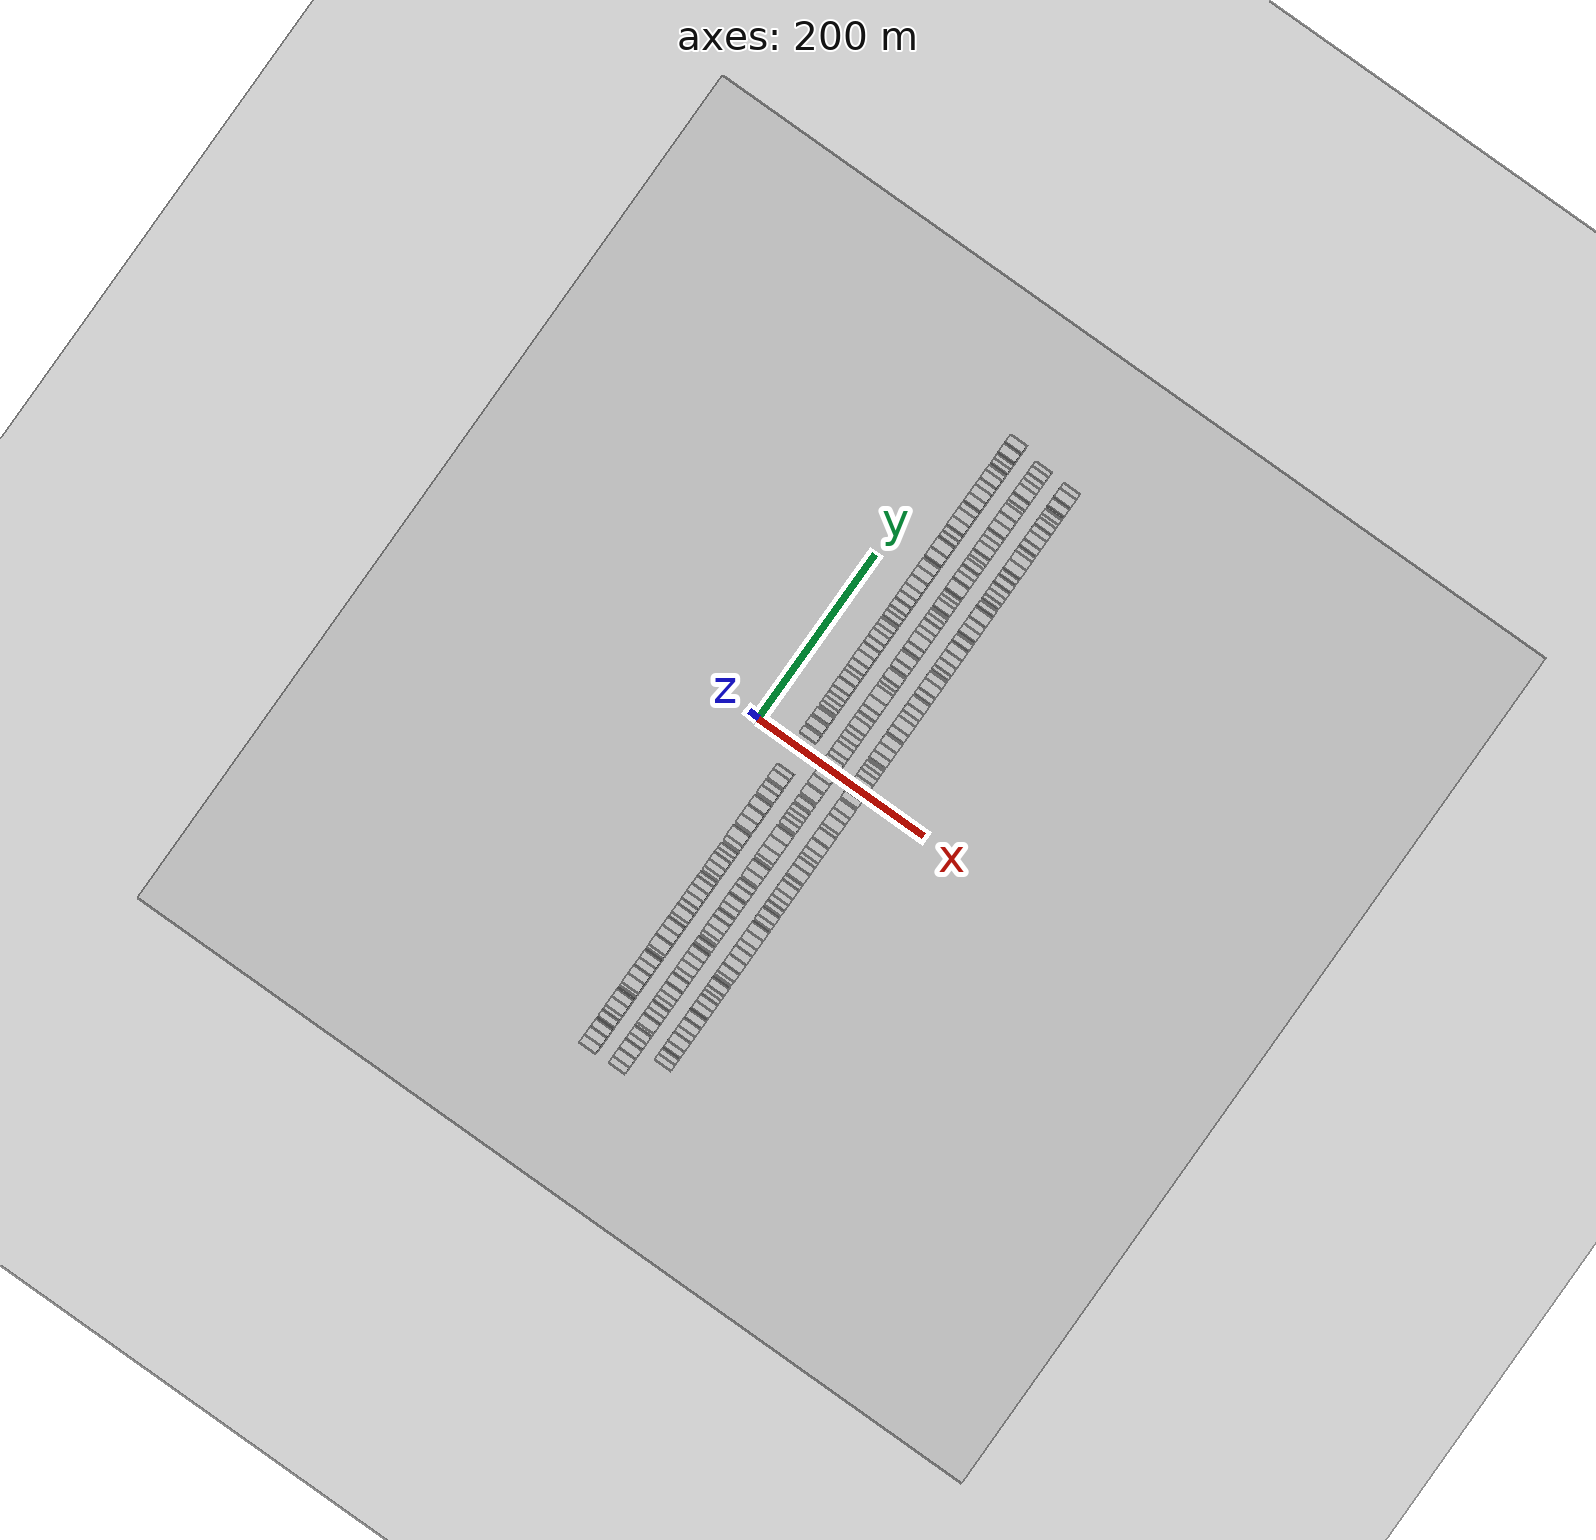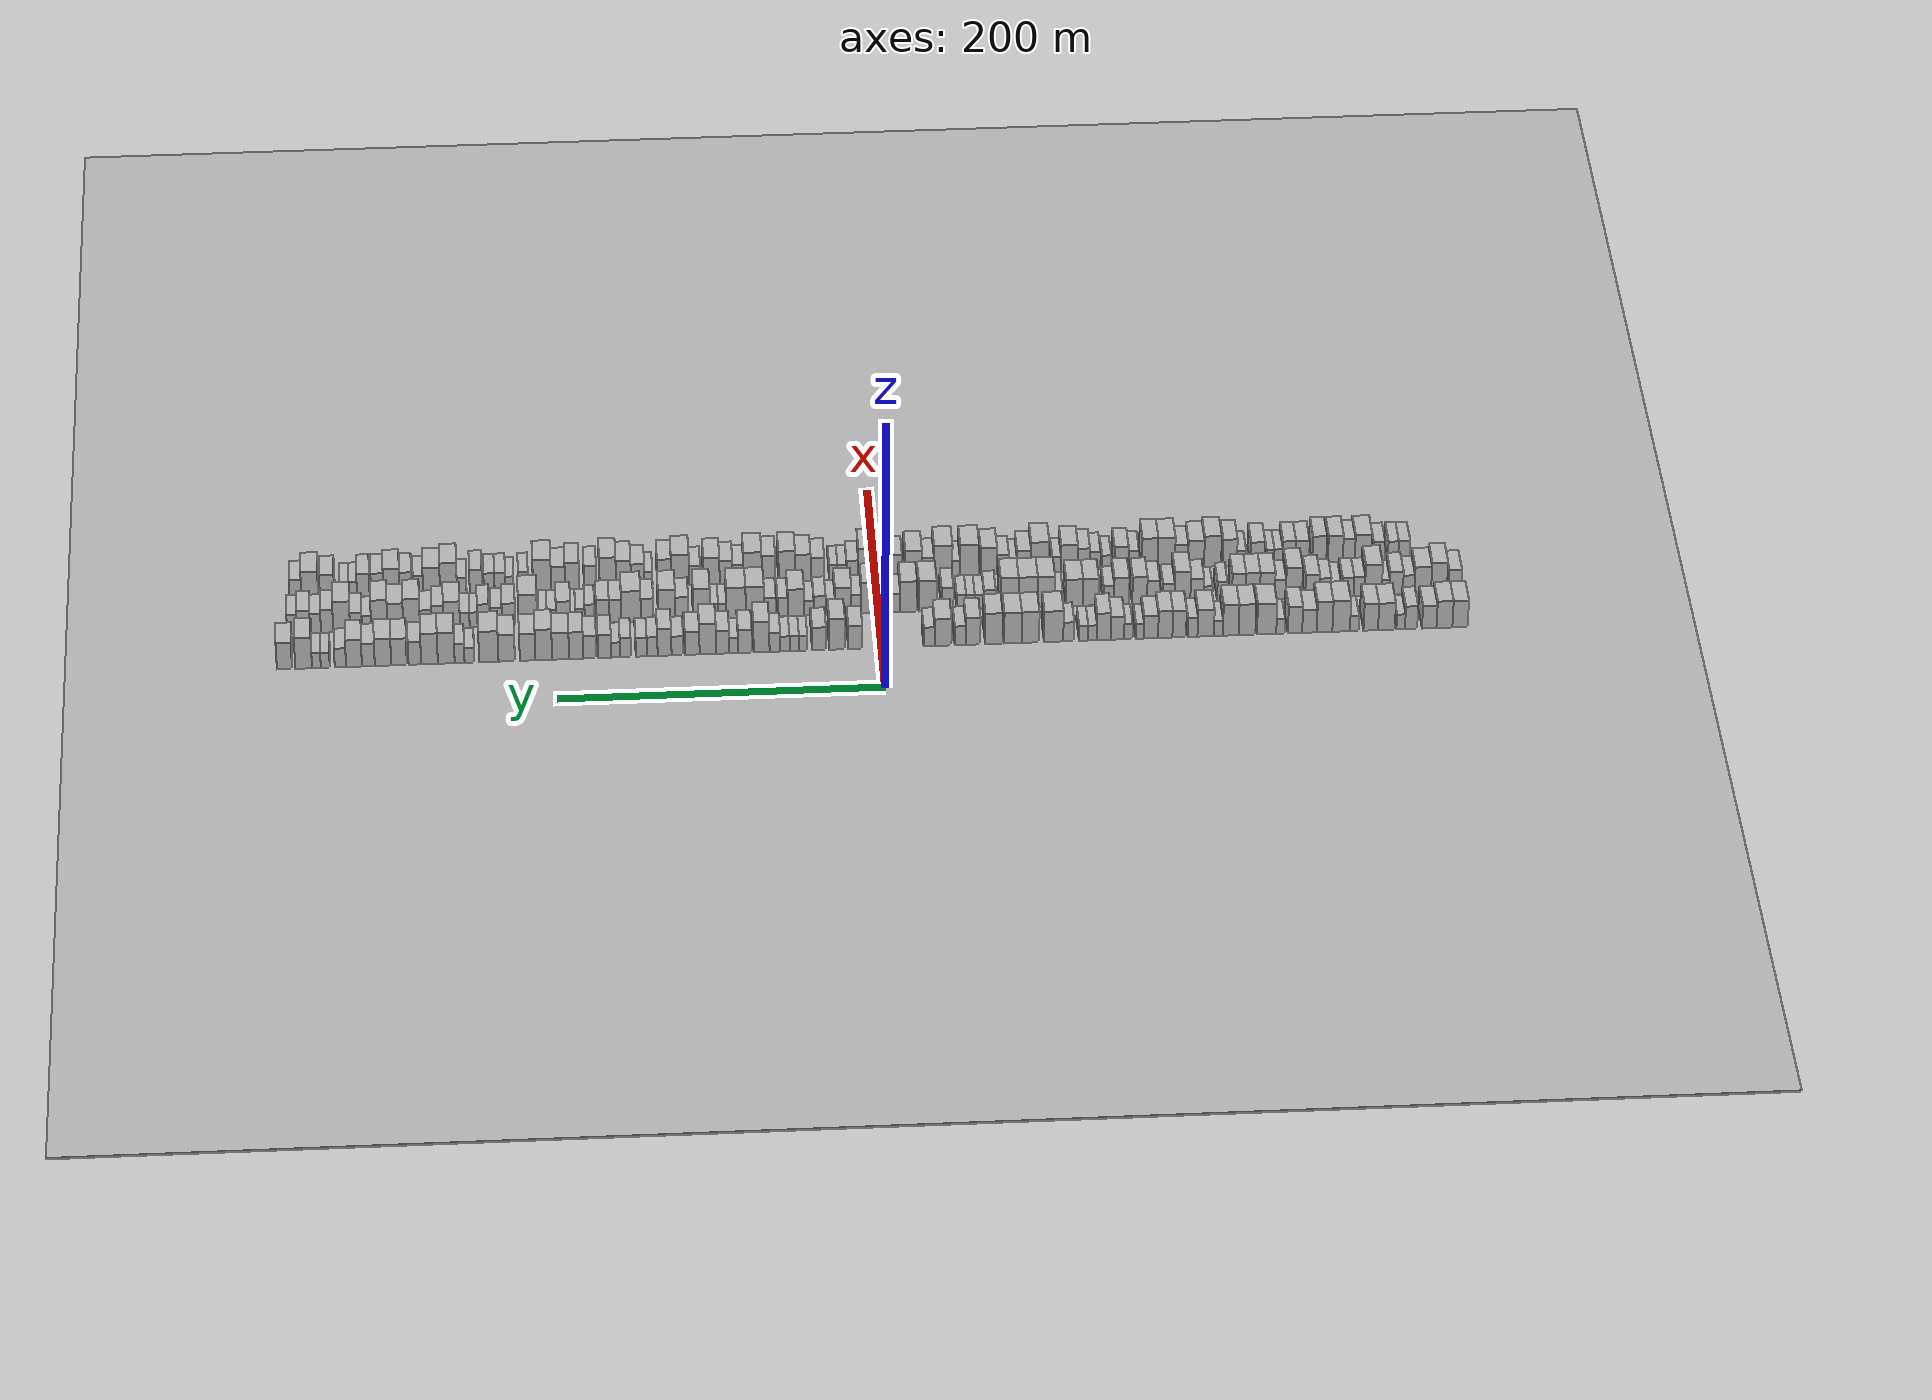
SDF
<?xml version="1.0" encoding="utf-8"?>

<sdf version="1.6">

   <world name="default">

      <gui fullscreen="0">

         <camera name="user_camera">

            <pose>-15 0 4.57585 0 0 0</pose>

            <view_controller>orbit</view_controller>

         </camera>

      </gui>

      <scene>

         <sky>

           <clouds>

             <speed>12</speed>

           </clouds>

         </sky>

         <ambient>0.4 0.4 0.4 1</ambient>

         <background>0.7 0.7 0.7 1</background>

         <shadows>1</shadows>

      </scene>

      <gravity>0 0 -9.8066</gravity>

      <magnetic_field>6e-06 2.3e-05 -4.2e-05</magnetic_field>

      <physics default="0" name="default_physics" type="ode">

         <ode>

            <solver>

               <type>quick</type>

               <iters>10</iters>

               <sor>1.0</sor>

               <use_dynamic_moi_rescaling>0</use_dynamic_moi_rescaling>

            </solver>

            <constraints>

               <cfm>0</cfm>

               <erp>0.2</erp>

               <contact_max_correcting_vel>100</contact_max_correcting_vel>

               <contact_surface_layer>0.001</contact_surface_layer>

            </constraints>

         </ode>

         <max_step_size>0.004</max_step_size>

         <real_time_factor>1</real_time_factor>

         <real_time_update_rate>250</real_time_update_rate>

      </physics>

      <light name="sun" type="directional">

         <cast_shadows>1</cast_shadows>

         <pose>0 0 10 0 0 0</pose>

         <diffuse>0.8 0.8 0.8 1</diffuse>

         <specular>0.2 0.2 0.2 1</specular>

         <attenuation>

            <range>1000</range>

            <constant>0.9</constant>

            <linear>0.01</linear>

            <quadratic>0.001</quadratic>

         </attenuation>

         <direction>-0.5 0.1 -0.9</direction>

      </light>

      <include>

         <name>ground_plane_1</name>

         <uri>model://HANNAS_ground_plane</uri>

         <pose>0 0 0  0 0 0</pose>

      </include>

      <include>

         <name>ground_plane_2</name>

         <uri>model://HANNAS_ground_plane</uri>

         <pose>100 0 0  0 0 0</pose>

      </include>

      <model name="building_1">

         <static>1</static>

         <pose frame="">50.0000 -355.3003 0 0.000000 0.000000 0.000000</pose>

         <link name="link">

            <pose frame="">0 0 10.50 0 0 0</pose>

            <collision name="collision">

               <geometry>

                  <box>

                     <size>20.0000 9.3994 21.0000</size>

                  </box>

               </geometry>

               <max_contacts>10</max_contacts>

               <surface>

                  <contact>

                     <ode/>

                  </contact>

                  <bounce/>

                  <friction>

                     <torsional>

                        <ode/>

                     </torsional>

                     <ode/>

                  </friction>

               </surface>

            </collision>

            <visual name="visual">

               <cast_shadows>0</cast_shadows>

               <geometry>

                  <box>

                     <size>20.0000 9.3994 21.0000</size>

                  </box>

               </geometry>

               <material>

                  <script>

                     <uri>model://HANNAS_wall/materials/scripts</uri>

                     <uri>model://HANNAS_wall/materials/textures</uri>

                     <name>vrc/HANNAS_wall</name>

                  </script>

               </material>

            </visual>

            <self_collide>0</self_collide>

            <enable_wind>0</enable_wind>

            <kinematic>0</kinematic>

         </link>

      </model>

      <model name="building_2">

         <static>1</static>

         <pose frame="">50.0000 -345.6907 0 0.000000 0.000000 0.000000</pose>

         <link name="link">

            <pose frame="">0 0 10.50 0 0 0</pose>

            <collision name="collision">

               <geometry>

                  <box>

                     <size>20.0000 9.8198 21.0000</size>

                  </box>

               </geometry>

               <max_contacts>10</max_contacts>

               <surface>

                  <contact>

                     <ode/>

                  </contact>

                  <bounce/>

                  <friction>

                     <torsional>

                        <ode/>

                     </torsional>

                     <ode/>

                  </friction>

               </surface>

            </collision>

            <visual name="visual">

               <cast_shadows>0</cast_shadows>

               <geometry>

                  <box>

                     <size>20.0000 9.8198 21.0000</size>

                  </box>

               </geometry>

               <material>

                  <script>

                     <uri>model://HANNAS_wall/materials/scripts</uri>

                     <uri>model://HANNAS_wall/materials/textures</uri>

                     <name>vrc/HANNAS_wall</name>

                  </script>

               </material>

            </visual>

            <self_collide>0</self_collide>

            <enable_wind>0</enable_wind>

            <kinematic>0</kinematic>

         </link>

      </model>

      <model name="building_3">

         <static>1</static>

         <pose frame="">50.0000 -336.3098 0 0.000000 0.000000 0.000000</pose>

         <link name="link">

            <pose frame="">0 0 9.00 0 0 0</pose>

            <collision name="collision">

               <geometry>

                  <box>

                     <size>20.0000 8.9419 18.0000</size>

                  </box>

               </geometry>

               <max_contacts>10</max_contacts>

               <surface>

                  <contact>

                     <ode/>

                  </contact>

                  <bounce/>

                  <friction>

                     <torsional>

                        <ode/>

                     </torsional>

                     <ode/>

                  </friction>

               </surface>

            </collision>

            <visual name="visual">

               <cast_shadows>0</cast_shadows>

               <geometry>

                  <box>

                     <size>20.0000 8.9419 18.0000</size>

                  </box>

               </geometry>

               <material>

                  <script>

                     <uri>model://HANNAS_wall/materials/scripts</uri>

                     <uri>model://HANNAS_wall/materials/textures</uri>

                     <name>vrc/HANNAS_wall</name>

                  </script>

               </material>

            </visual>

            <self_collide>0</self_collide>

            <enable_wind>0</enable_wind>

            <kinematic>0</kinematic>

         </link>

      </model>

      <model name="building_4">

         <static>1</static>

         <pose frame="">50.0000 -325.0578 0 0.000000 0.000000 0.000000</pose>

         <link name="link">

            <pose frame="">0 0 9.00 0 0 0</pose>

            <collision name="collision">

               <geometry>

                  <box>

                     <size>20.0000 7.5621 18.0000</size>

                  </box>

               </geometry>

               <max_contacts>10</max_contacts>

               <surface>

                  <contact>

                     <ode/>

                  </contact>

                  <bounce/>

                  <friction>

                     <torsional>

                        <ode/>

                     </torsional>

                     <ode/>

                  </friction>

               </surface>

            </collision>

            <visual name="visual">

               <cast_shadows>0</cast_shadows>

               <geometry>

                  <box>

                     <size>20.0000 7.5621 18.0000</size>

                  </box>

               </geometry>

               <material>

                  <script>

                     <uri>model://HANNAS_wall/materials/scripts</uri>

                     <uri>model://HANNAS_wall/materials/textures</uri>

                     <name>vrc/HANNAS_wall</name>

                  </script>

               </material>

            </visual>

            <self_collide>0</self_collide>

            <enable_wind>0</enable_wind>

            <kinematic>0</kinematic>

         </link>

      </model>

      <model name="building_5">

         <static>1</static>

         <pose frame="">50.0000 -318.6522 0 0.000000 0.000000 0.000000</pose>

         <link name="link">

            <pose frame="">0 0 6.00 0 0 0</pose>

            <collision name="collision">

               <geometry>

                  <box>

                     <size>20.0000 5.2492 12.0000</size>

                  </box>

               </geometry>

               <max_contacts>10</max_contacts>

               <surface>

                  <contact>

                     <ode/>

                  </contact>

                  <bounce/>

                  <friction>

                     <torsional>

                        <ode/>

                     </torsional>

                     <ode/>

                  </friction>

               </surface>

            </collision>

            <visual name="visual">

               <cast_shadows>0</cast_shadows>

               <geometry>

                  <box>

                     <size>20.0000 5.2492 12.0000</size>

                  </box>

               </geometry>

               <material>

                  <script>

                     <uri>model://HANNAS_wall/materials/scripts</uri>

                     <uri>model://HANNAS_wall/materials/textures</uri>

                     <name>vrc/HANNAS_wall</name>

                  </script>

               </material>

            </visual>

            <self_collide>0</self_collide>

            <enable_wind>0</enable_wind>

            <kinematic>0</kinematic>

         </link>

      </model>

      <model name="building_6">

         <static>1</static>

         <pose frame="">50.0000 -309.8411 0 0.000000 0.000000 0.000000</pose>

         <link name="link">

            <pose frame="">0 0 10.50 0 0 0</pose>

            <collision name="collision">

               <geometry>

                  <box>

                     <size>20.0000 10.3729 21.0000</size>

                  </box>

               </geometry>

               <max_contacts>10</max_contacts>

               <surface>

                  <contact>

                     <ode/>

                  </contact>

                  <bounce/>

                  <friction>

                     <torsional>

                        <ode/>

                     </torsional>

                     <ode/>

                  </friction>

               </surface>

            </collision>

            <visual name="visual">

               <cast_shadows>0</cast_shadows>

               <geometry>

                  <box>

                     <size>20.0000 10.3729 21.0000</size>

                  </box>

               </geometry>

               <material>

                  <script>

                     <uri>model://HANNAS_wall/materials/scripts</uri>

                     <uri>model://HANNAS_wall/materials/textures</uri>

                     <name>vrc/HANNAS_wall</name>

                  </script>

               </material>

            </visual>

            <self_collide>0</self_collide>

            <enable_wind>0</enable_wind>

            <kinematic>0</kinematic>

         </link>

      </model>

      <model name="building_7">

         <static>1</static>

         <pose frame="">50.0000 -300.1779 0 0.000000 0.000000 0.000000</pose>

         <link name="link">

            <pose frame="">0 0 10.50 0 0 0</pose>

            <collision name="collision">

               <geometry>

                  <box>

                     <size>20.0000 8.9536 21.0000</size>

                  </box>

               </geometry>

               <max_contacts>10</max_contacts>

               <surface>

                  <contact>

                     <ode/>

                  </contact>

                  <bounce/>

                  <friction>

                     <torsional>

                        <ode/>

                     </torsional>

                     <ode/>

                  </friction>

               </surface>

            </collision>

            <visual name="visual">

               <cast_shadows>0</cast_shadows>

               <geometry>

                  <box>

                     <size>20.0000 8.9536 21.0000</size>

                  </box>

               </geometry>

               <material>

                  <script>

                     <uri>model://HANNAS_wall/materials/scripts</uri>

                     <uri>model://HANNAS_wall/materials/textures</uri>

                     <name>vrc/HANNAS_wall</name>

                  </script>

               </material>

            </visual>

            <self_collide>0</self_collide>

            <enable_wind>0</enable_wind>

            <kinematic>0</kinematic>

         </link>

      </model>

      <model name="building_8">

         <static>1</static>

         <pose frame="">50.0000 -290.0002 0 0.000000 0.000000 0.000000</pose>

         <link name="link">

            <pose frame="">0 0 6.00 0 0 0</pose>

            <collision name="collision">

               <geometry>

                  <box>

                     <size>20.0000 5.4017 12.0000</size>

                  </box>

               </geometry>

               <max_contacts>10</max_contacts>

               <surface>

                  <contact>

                     <ode/>

                  </contact>

                  <bounce/>

                  <friction>

                     <torsional>

                        <ode/>

                     </torsional>

                     <ode/>

                  </friction>

               </surface>

            </collision>

            <visual name="visual">

               <cast_shadows>0</cast_shadows>

               <geometry>

                  <box>

                     <size>20.0000 5.4017 12.0000</size>

                  </box>

               </geometry>

               <material>

                  <script>

                     <uri>model://HANNAS_wall/materials/scripts</uri>

                     <uri>model://HANNAS_wall/materials/textures</uri>

                     <name>vrc/HANNAS_wall</name>

                  </script>

               </material>

            </visual>

            <self_collide>0</self_collide>

            <enable_wind>0</enable_wind>

            <kinematic>0</kinematic>

         </link>

      </model>

      <model name="building_9">

         <static>1</static>

         <pose frame="">50.0000 -281.8880 0 0.000000 0.000000 0.000000</pose>

         <link name="link">

            <pose frame="">0 0 12.00 0 0 0</pose>

            <collision name="collision">

               <geometry>

                  <box>

                     <size>20.0000 10.8225 24.0000</size>

                  </box>

               </geometry>

               <max_contacts>10</max_contacts>

               <surface>

                  <contact>

                     <ode/>

                  </contact>

                  <bounce/>

                  <friction>

                     <torsional>

                        <ode/>

                     </torsional>

                     <ode/>

                  </friction>

               </surface>

            </collision>

            <visual name="visual">

               <cast_shadows>0</cast_shadows>

               <geometry>

                  <box>

                     <size>20.0000 10.8225 24.0000</size>

                  </box>

               </geometry>

               <material>

                  <script>

                     <uri>model://HANNAS_wall/materials/scripts</uri>

                     <uri>model://HANNAS_wall/materials/textures</uri>

                     <name>vrc/HANNAS_wall</name>

                  </script>

               </material>

            </visual>

            <self_collide>0</self_collide>

            <enable_wind>0</enable_wind>

            <kinematic>0</kinematic>

         </link>

      </model>

      <model name="building_10">

         <static>1</static>

         <pose frame="">50.0000 -271.6227 0 0.000000 0.000000 0.000000</pose>

         <link name="link">

            <pose frame="">0 0 12.00 0 0 0</pose>

            <collision name="collision">

               <geometry>

                  <box>

                     <size>20.0000 9.7080 24.0000</size>

                  </box>

               </geometry>

               <max_contacts>10</max_contacts>

               <surface>

                  <contact>

                     <ode/>

                  </contact>

                  <bounce/>

                  <friction>

                     <torsional>

                        <ode/>

                     </torsional>

                     <ode/>

                  </friction>

               </surface>

            </collision>

            <visual name="visual">

               <cast_shadows>0</cast_shadows>

               <geometry>

                  <box>

                     <size>20.0000 9.7080 24.0000</size>

                  </box>

               </geometry>

               <material>

                  <script>

                     <uri>model://HANNAS_wall/materials/scripts</uri>

                     <uri>model://HANNAS_wall/materials/textures</uri>

                     <name>vrc/HANNAS_wall</name>

                  </script>

               </material>

            </visual>

            <self_collide>0</self_collide>

            <enable_wind>0</enable_wind>

            <kinematic>0</kinematic>

         </link>

      </model>

      <model name="building_11">

         <static>1</static>

         <pose frame="">50.0000 -262.3106 0 0.000000 0.000000 0.000000</pose>

         <link name="link">

            <pose frame="">0 0 9.00 0 0 0</pose>

            <collision name="collision">

               <geometry>

                  <box>

                     <size>20.0000 8.9163 18.0000</size>

                  </box>

               </geometry>

               <max_contacts>10</max_contacts>

               <surface>

                  <contact>

                     <ode/>

                  </contact>

                  <bounce/>

                  <friction>

                     <torsional>

                        <ode/>

                     </torsional>

                     <ode/>

                  </friction>

               </surface>

            </collision>

            <visual name="visual">

               <cast_shadows>0</cast_shadows>

               <geometry>

                  <box>

                     <size>20.0000 8.9163 18.0000</size>

                  </box>

               </geometry>

               <material>

                  <script>

                     <uri>model://HANNAS_wall/materials/scripts</uri>

                     <uri>model://HANNAS_wall/materials/textures</uri>

                     <name>vrc/HANNAS_wall</name>

                  </script>

               </material>

            </visual>

            <self_collide>0</self_collide>

            <enable_wind>0</enable_wind>

            <kinematic>0</kinematic>

         </link>

      </model>

      <model name="building_12">

         <static>1</static>

         <pose frame="">50.0000 -253.4415 0 0.000000 0.000000 0.000000</pose>

         <link name="link">

            <pose frame="">0 0 10.50 0 0 0</pose>

            <collision name="collision">

               <geometry>

                  <box>

                     <size>20.0000 8.8218 21.0000</size>

                  </box>

               </geometry>

               <max_contacts>10</max_contacts>

               <surface>

                  <contact>

                     <ode/>

                  </contact>

                  <bounce/>

                  <friction>

                     <torsional>

                        <ode/>

                     </torsional>

                     <ode/>

                  </friction>

               </surface>

            </collision>

            <visual name="visual">

               <cast_shadows>0</cast_shadows>

               <geometry>

                  <box>

                     <size>20.0000 8.8218 21.0000</size>

                  </box>

               </geometry>

               <material>

                  <script>

                     <uri>model://HANNAS_wall/materials/scripts</uri>

                     <uri>model://HANNAS_wall/materials/textures</uri>

                     <name>vrc/HANNAS_wall</name>

                  </script>

               </material>

            </visual>

            <self_collide>0</self_collide>

            <enable_wind>0</enable_wind>

            <kinematic>0</kinematic>

         </link>

      </model>

      <model name="building_13">

         <static>1</static>

         <pose frame="">50.0000 -244.4483 0 0.000000 0.000000 0.000000</pose>

         <link name="link">

            <pose frame="">0 0 6.00 0 0 0</pose>

            <collision name="collision">

               <geometry>

                  <box>

                     <size>20.0000 5.1646 12.0000</size>

                  </box>

               </geometry>

               <max_contacts>10</max_contacts>

               <surface>

                  <contact>

                     <ode/>

                  </contact>

                  <bounce/>

                  <friction>

                     <torsional>

                        <ode/>

                     </torsional>

                     <ode/>

                  </friction>

               </surface>

            </collision>

            <visual name="visual">

               <cast_shadows>0</cast_shadows>

               <geometry>

                  <box>

                     <size>20.0000 5.1646 12.0000</size>

                  </box>

               </geometry>

               <material>

                  <script>

                     <uri>model://HANNAS_wall/materials/scripts</uri>

                     <uri>model://HANNAS_wall/materials/textures</uri>

                     <name>vrc/HANNAS_wall</name>

                  </script>

               </material>

            </visual>

            <self_collide>0</self_collide>

            <enable_wind>0</enable_wind>

            <kinematic>0</kinematic>

         </link>

      </model>

      <model name="building_14">

         <static>1</static>

         <pose frame="">50.0000 -235.9190 0 0.000000 0.000000 0.000000</pose>

         <link name="link">

            <pose frame="">0 0 12.00 0 0 0</pose>

            <collision name="collision">

               <geometry>

                  <box>

                     <size>20.0000 11.8939 24.0000</size>

                  </box>

               </geometry>

               <max_contacts>10</max_contacts>

               <surface>

                  <contact>

                     <ode/>

                  </contact>

                  <bounce/>

                  <friction>

                     <torsional>

                        <ode/>

                     </torsional>

                     <ode/>

                  </friction>

               </surface>

            </collision>

            <visual name="visual">

               <cast_shadows>0</cast_shadows>

               <geometry>

                  <box>

                     <size>20.0000 11.8939 24.0000</size>

                  </box>

               </geometry>

               <material>

                  <script>

                     <uri>model://HANNAS_wall/materials/scripts</uri>

                     <uri>model://HANNAS_wall/materials/textures</uri>

                     <name>vrc/HANNAS_wall</name>

                  </script>

               </material>

            </visual>

            <self_collide>0</self_collide>

            <enable_wind>0</enable_wind>

            <kinematic>0</kinematic>

         </link>

      </model>

      <model name="building_15">

         <static>1</static>

         <pose frame="">50.0000 -223.7970 0 0.000000 0.000000 0.000000</pose>

         <link name="link">

            <pose frame="">0 0 12.00 0 0 0</pose>

            <collision name="collision">

               <geometry>

                  <box>

                     <size>20.0000 10.3501 24.0000</size>

                  </box>

               </geometry>

               <max_contacts>10</max_contacts>

               <surface>

                  <contact>

                     <ode/>

                  </contact>

                  <bounce/>

                  <friction>

                     <torsional>

                        <ode/>

                     </torsional>

                     <ode/>

                  </friction>

               </surface>

            </collision>

            <visual name="visual">

               <cast_shadows>0</cast_shadows>

               <geometry>

                  <box>

                     <size>20.0000 10.3501 24.0000</size>

                  </box>

               </geometry>

               <material>

                  <script>

                     <uri>model://HANNAS_wall/materials/scripts</uri>

                     <uri>model://HANNAS_wall/materials/textures</uri>

                     <name>vrc/HANNAS_wall</name>

                  </script>

               </material>

            </visual>

            <self_collide>0</self_collide>

            <enable_wind>0</enable_wind>

            <kinematic>0</kinematic>

         </link>

      </model>

      <model name="building_16">

         <static>1</static>

         <pose frame="">50.0000 -213.7750 0 0.000000 0.000000 0.000000</pose>

         <link name="link">

            <pose frame="">0 0 12.00 0 0 0</pose>

            <collision name="collision">

               <geometry>

                  <box>

                     <size>20.0000 9.6940 24.0000</size>

                  </box>

               </geometry>

               <max_contacts>10</max_contacts>

               <surface>

                  <contact>

                     <ode/>

                  </contact>

                  <bounce/>

                  <friction>

                     <torsional>

                        <ode/>

                     </torsional>

                     <ode/>

                  </friction>

               </surface>

            </collision>

            <visual name="visual">

               <cast_shadows>0</cast_shadows>

               <geometry>

                  <box>

                     <size>20.0000 9.6940 24.0000</size>

                  </box>

               </geometry>

               <material>

                  <script>

                     <uri>model://HANNAS_wall/materials/scripts</uri>

                     <uri>model://HANNAS_wall/materials/textures</uri>

                     <name>vrc/HANNAS_wall</name>

                  </script>

               </material>

            </visual>

            <self_collide>0</self_collide>

            <enable_wind>0</enable_wind>

            <kinematic>0</kinematic>

         </link>

      </model>

      <model name="building_17">

         <static>1</static>

         <pose frame="">50.0000 -206.1758 0 0.000000 0.000000 0.000000</pose>

         <link name="link">

            <pose frame="">0 0 6.00 0 0 0</pose>

            <collision name="collision">

               <geometry>

                  <box>

                     <size>20.0000 5.5044 12.0000</size>

                  </box>

               </geometry>

               <max_contacts>10</max_contacts>

               <surface>

                  <contact>

                     <ode/>

                  </contact>

                  <bounce/>

                  <friction>

                     <torsional>

                        <ode/>

                     </torsional>

                     <ode/>

                  </friction>

               </surface>

            </collision>

            <visual name="visual">

               <cast_shadows>0</cast_shadows>

               <geometry>

                  <box>

                     <size>20.0000 5.5044 12.0000</size>

                  </box>

               </geometry>

               <material>

                  <script>

                     <uri>model://HANNAS_wall/materials/scripts</uri>

                     <uri>model://HANNAS_wall/materials/textures</uri>

                     <name>vrc/HANNAS_wall</name>

                  </script>

               </material>

            </visual>

            <self_collide>0</self_collide>

            <enable_wind>0</enable_wind>

            <kinematic>0</kinematic>

         </link>

      </model>

      <model name="building_18">

         <static>1</static>

         <pose frame="">50.0000 -198.3676 0 0.000000 0.000000 0.000000</pose>

         <link name="link">

            <pose frame="">0 0 10.50 0 0 0</pose>

            <collision name="collision">

               <geometry>

                  <box>

                     <size>20.0000 10.1119 21.0000</size>

                  </box>

               </geometry>

               <max_contacts>10</max_contacts>

               <surface>

                  <contact>

                     <ode/>

                  </contact>

                  <bounce/>

                  <friction>

                     <torsional>

                        <ode/>

                     </torsional>

                     <ode/>

                  </friction>

               </surface>

            </collision>

            <visual name="visual">

               <cast_shadows>0</cast_shadows>

               <geometry>

                  <box>

                     <size>20.0000 10.1119 21.0000</size>

                  </box>

               </geometry>

               <material>

                  <script>

                     <uri>model://HANNAS_wall/materials/scripts</uri>

                     <uri>model://HANNAS_wall/materials/textures</uri>

                     <name>vrc/HANNAS_wall</name>

                  </script>

               </material>

            </visual>

            <self_collide>0</self_collide>

            <enable_wind>0</enable_wind>

            <kinematic>0</kinematic>

         </link>

      </model>

      <model name="building_19">

         <static>1</static>

         <pose frame="">50.0000 -190.3090 0 0.000000 0.000000 0.000000</pose>

         <link name="link">

            <pose frame="">0 0 7.50 0 0 0</pose>

            <collision name="collision">

               <geometry>

                  <box>

                     <size>20.0000 6.0053 15.0000</size>

                  </box>

               </geometry>

               <max_contacts>10</max_contacts>

               <surface>

                  <contact>

                     <ode/>

                  </contact>

                  <bounce/>

                  <friction>

                     <torsional>

                        <ode/>

                     </torsional>

                     <ode/>

                  </friction>

               </surface>

            </collision>

            <visual name="visual">

               <cast_shadows>0</cast_shadows>

               <geometry>

                  <box>

                     <size>20.0000 6.0053 15.0000</size>

                  </box>

               </geometry>

               <material>

                  <script>

                     <uri>model://HANNAS_wall/materials/scripts</uri>

                     <uri>model://HANNAS_wall/materials/textures</uri>

                     <name>vrc/HANNAS_wall</name>

                  </script>

               </material>

            </visual>

            <self_collide>0</self_collide>

            <enable_wind>0</enable_wind>

            <kinematic>0</kinematic>

         </link>

      </model>

      <model name="building_20">

         <static>1</static>

         <pose frame="">50.0000 -182.0856 0 0.000000 0.000000 0.000000</pose>

         <link name="link">

            <pose frame="">0 0 10.50 0 0 0</pose>

            <collision name="collision">

               <geometry>

                  <box>

                     <size>20.0000 8.4416 21.0000</size>

                  </box>

               </geometry>

               <max_contacts>10</max_contacts>

               <surface>

                  <contact>

                     <ode/>

                  </contact>

                  <bounce/>

                  <friction>

                     <torsional>

                        <ode/>

                     </torsional>

                     <ode/>

                  </friction>

               </surface>

            </collision>

            <visual name="visual">

               <cast_shadows>0</cast_shadows>

               <geometry>

                  <box>

                     <size>20.0000 8.4416 21.0000</size>

                  </box>

               </geometry>

               <material>

                  <script>

                     <uri>model://HANNAS_wall/materials/scripts</uri>

                     <uri>model://HANNAS_wall/materials/textures</uri>

                     <name>vrc/HANNAS_wall</name>

                  </script>

               </material>

            </visual>

            <self_collide>0</self_collide>

            <enable_wind>0</enable_wind>

            <kinematic>0</kinematic>

         </link>

      </model>

      <model name="building_21">

         <static>1</static>

         <pose frame="">50.0000 -173.4730 0 0.000000 0.000000 0.000000</pose>

         <link name="link">

            <pose frame="">0 0 10.50 0 0 0</pose>

            <collision name="collision">

               <geometry>

                  <box>

                     <size>20.0000 8.7835 21.0000</size>

                  </box>

               </geometry>

               <max_contacts>10</max_contacts>

               <surface>

                  <contact>

                     <ode/>

                  </contact>

                  <bounce/>

                  <friction>

                     <torsional>

                        <ode/>

                     </torsional>

                     <ode/>

                  </friction>

               </surface>

            </collision>

            <visual name="visual">

               <cast_shadows>0</cast_shadows>

               <geometry>

                  <box>

                     <size>20.0000 8.7835 21.0000</size>

                  </box>

               </geometry>

               <material>

                  <script>

                     <uri>model://HANNAS_wall/materials/scripts</uri>

                     <uri>model://HANNAS_wall/materials/textures</uri>

                     <name>vrc/HANNAS_wall</name>

                  </script>

               </material>

            </visual>

            <self_collide>0</self_collide>

            <enable_wind>0</enable_wind>

            <kinematic>0</kinematic>

         </link>

      </model>

      <model name="building_22">

         <static>1</static>

         <pose frame="">50.0000 -164.6503 0 0.000000 0.000000 0.000000</pose>

         <link name="link">

            <pose frame="">0 0 9.00 0 0 0</pose>

            <collision name="collision">

               <geometry>

                  <box>

                     <size>20.0000 8.8619 18.0000</size>

                  </box>

               </geometry>

               <max_contacts>10</max_contacts>

               <surface>

                  <contact>

                     <ode/>

                  </contact>

                  <bounce/>

                  <friction>

                     <torsional>

                        <ode/>

                     </torsional>

                     <ode/>

                  </friction>

               </surface>

            </collision>

            <visual name="visual">

               <cast_shadows>0</cast_shadows>

               <geometry>

                  <box>

                     <size>20.0000 8.8619 18.0000</size>

                  </box>

               </geometry>

               <material>

                  <script>

                     <uri>model://HANNAS_wall/materials/scripts</uri>

                     <uri>model://HANNAS_wall/materials/textures</uri>

                     <name>vrc/HANNAS_wall</name>

                  </script>

               </material>

            </visual>

            <self_collide>0</self_collide>

            <enable_wind>0</enable_wind>

            <kinematic>0</kinematic>

         </link>

      </model>

      <model name="building_23">

         <static>1</static>

         <pose frame="">50.0000 -157.7561 0 0.000000 0.000000 0.000000</pose>

         <link name="link">

            <pose frame="">0 0 6.00 0 0 0</pose>

            <collision name="collision">

               <geometry>

                  <box>

                     <size>20.0000 4.9264 12.0000</size>

                  </box>

               </geometry>

               <max_contacts>10</max_contacts>

               <surface>

                  <contact>

                     <ode/>

                  </contact>

                  <bounce/>

                  <friction>

                     <torsional>

                        <ode/>

                     </torsional>

                     <ode/>

                  </friction>

               </surface>

            </collision>

            <visual name="visual">

               <cast_shadows>0</cast_shadows>

               <geometry>

                  <box>

                     <size>20.0000 4.9264 12.0000</size>

                  </box>

               </geometry>

               <material>

                  <script>

                     <uri>model://HANNAS_wall/materials/scripts</uri>

                     <uri>model://HANNAS_wall/materials/textures</uri>

                     <name>vrc/HANNAS_wall</name>

                  </script>

               </material>

            </visual>

            <self_collide>0</self_collide>

            <enable_wind>0</enable_wind>

            <kinematic>0</kinematic>

         </link>

      </model>

      <model name="building_24">

         <static>1</static>

         <pose frame="">50.0000 -150.7325 0 0.000000 0.000000 0.000000</pose>

         <link name="link">

            <pose frame="">0 0 6.00 0 0 0</pose>

            <collision name="collision">

               <geometry>

                  <box>

                     <size>20.0000 5.1209 12.0000</size>

                  </box>

               </geometry>

               <max_contacts>10</max_contacts>

               <surface>

                  <contact>

                     <ode/>

                  </contact>

                  <bounce/>

                  <friction>

                     <torsional>

                        <ode/>

                     </torsional>

                     <ode/>

                  </friction>

               </surface>

            </collision>

            <visual name="visual">

               <cast_shadows>0</cast_shadows>

               <geometry>

                  <box>

                     <size>20.0000 5.1209 12.0000</size>

                  </box>

               </geometry>

               <material>

                  <script>

                     <uri>model://HANNAS_wall/materials/scripts</uri>

                     <uri>model://HANNAS_wall/materials/textures</uri>

                     <name>vrc/HANNAS_wall</name>

                  </script>

               </material>

            </visual>

            <self_collide>0</self_collide>

            <enable_wind>0</enable_wind>

            <kinematic>0</kinematic>

         </link>

      </model>

      <model name="building_25">

         <static>1</static>

         <pose frame="">50.0000 -143.9937 0 0.000000 0.000000 0.000000</pose>

         <link name="link">

            <pose frame="">0 0 9.00 0 0 0</pose>

            <collision name="collision">

               <geometry>

                  <box>

                     <size>20.0000 8.3567 18.0000</size>

                  </box>

               </geometry>

               <max_contacts>10</max_contacts>

               <surface>

                  <contact>

                     <ode/>

                  </contact>

                  <bounce/>

                  <friction>

                     <torsional>

                        <ode/>

                     </torsional>

                     <ode/>

                  </friction>

               </surface>

            </collision>

            <visual name="visual">

               <cast_shadows>0</cast_shadows>

               <geometry>

                  <box>

                     <size>20.0000 8.3567 18.0000</size>

                  </box>

               </geometry>

               <material>

                  <script>

                     <uri>model://HANNAS_wall/materials/scripts</uri>

                     <uri>model://HANNAS_wall/materials/textures</uri>

                     <name>vrc/HANNAS_wall</name>

                  </script>

               </material>

            </visual>

            <self_collide>0</self_collide>

            <enable_wind>0</enable_wind>

            <kinematic>0</kinematic>

         </link>

      </model>

      <model name="building_26">

         <static>1</static>

         <pose frame="">50.0000 -135.5827 0 0.000000 0.000000 0.000000</pose>

         <link name="link">

            <pose frame="">0 0 10.50 0 0 0</pose>

            <collision name="collision">

               <geometry>

                  <box>

                     <size>20.0000 8.4652 21.0000</size>

                  </box>

               </geometry>

               <max_contacts>10</max_contacts>

               <surface>

                  <contact>

                     <ode/>

                  </contact>

                  <bounce/>

                  <friction>

                     <torsional>

                        <ode/>

                     </torsional>

                     <ode/>

                  </friction>

               </surface>

            </collision>

            <visual name="visual">

               <cast_shadows>0</cast_shadows>

               <geometry>

                  <box>

                     <size>20.0000 8.4652 21.0000</size>

                  </box>

               </geometry>

               <material>

                  <script>

                     <uri>model://HANNAS_wall/materials/scripts</uri>

                     <uri>model://HANNAS_wall/materials/textures</uri>

                     <name>vrc/HANNAS_wall</name>

                  </script>

               </material>

            </visual>

            <self_collide>0</self_collide>

            <enable_wind>0</enable_wind>

            <kinematic>0</kinematic>

         </link>

      </model>

      <model name="building_27">

         <static>1</static>

         <pose frame="">50.0000 -128.6644 0 0.000000 0.000000 0.000000</pose>

         <link name="link">

            <pose frame="">0 0 6.00 0 0 0</pose>

            <collision name="collision">

               <geometry>

                  <box>

                     <size>20.0000 5.3713 12.0000</size>

                  </box>

               </geometry>

               <max_contacts>10</max_contacts>

               <surface>

                  <contact>

                     <ode/>

                  </contact>

                  <bounce/>

                  <friction>

                     <torsional>

                        <ode/>

                     </torsional>

                     <ode/>

                  </friction>

               </surface>

            </collision>

            <visual name="visual">

               <cast_shadows>0</cast_shadows>

               <geometry>

                  <box>

                     <size>20.0000 5.3713 12.0000</size>

                  </box>

               </geometry>

               <material>

                  <script>

                     <uri>model://HANNAS_wall/materials/scripts</uri>

                     <uri>model://HANNAS_wall/materials/textures</uri>

                     <name>vrc/HANNAS_wall</name>

                  </script>

               </material>

            </visual>

            <self_collide>0</self_collide>

            <enable_wind>0</enable_wind>

            <kinematic>0</kinematic>

         </link>

      </model>

      <model name="building_28">

         <static>1</static>

         <pose frame="">50.0000 -123.1630 0 0.000000 0.000000 0.000000</pose>

         <link name="link">

            <pose frame="">0 0 6.00 0 0 0</pose>

            <collision name="collision">

               <geometry>

                  <box>

                     <size>20.0000 5.6315 12.0000</size>

                  </box>

               </geometry>

               <max_contacts>10</max_contacts>

               <surface>

                  <contact>

                     <ode/>

                  </contact>

                  <bounce/>

                  <friction>

                     <torsional>

                        <ode/>

                     </torsional>

                     <ode/>

                  </friction>

               </surface>

            </collision>

            <visual name="visual">

               <cast_shadows>0</cast_shadows>

               <geometry>

                  <box>

                     <size>20.0000 5.6315 12.0000</size>

                  </box>

               </geometry>

               <material>

                  <script>

                     <uri>model://HANNAS_wall/materials/scripts</uri>

                     <uri>model://HANNAS_wall/materials/textures</uri>

                     <name>vrc/HANNAS_wall</name>

                  </script>

               </material>

            </visual>

            <self_collide>0</self_collide>

            <enable_wind>0</enable_wind>

            <kinematic>0</kinematic>

         </link>

      </model>

      <model name="building_29">

         <static>1</static>

         <pose frame="">50.0000 -114.0259 0 0.000000 0.000000 0.000000</pose>

         <link name="link">

            <pose frame="">0 0 7.50 0 0 0</pose>

            <collision name="collision">

               <geometry>

                  <box>

                     <size>20.0000 6.6426 15.0000</size>

                  </box>

               </geometry>

               <max_contacts>10</max_contacts>

               <surface>

                  <contact>

                     <ode/>

                  </contact>

                  <bounce/>

                  <friction>

                     <torsional>

                        <ode/>

                     </torsional>

                     <ode/>

                  </friction>

               </surface>

            </collision>

            <visual name="visual">

               <cast_shadows>0</cast_shadows>

               <geometry>

                  <box>

                     <size>20.0000 6.6426 15.0000</size>

                  </box>

               </geometry>

               <material>

                  <script>

                     <uri>model://HANNAS_wall/materials/scripts</uri>

                     <uri>model://HANNAS_wall/materials/textures</uri>

                     <name>vrc/HANNAS_wall</name>

                  </script>

               </material>

            </visual>

            <self_collide>0</self_collide>

            <enable_wind>0</enable_wind>

            <kinematic>0</kinematic>

         </link>

      </model>

      <model name="building_30">

         <static>1</static>

         <pose frame="">50.0000 -104.7813 0 0.000000 0.000000 0.000000</pose>

         <link name="link">

            <pose frame="">0 0 12.00 0 0 0</pose>

            <collision name="collision">

               <geometry>

                  <box>

                     <size>20.0000 11.8466 24.0000</size>

                  </box>

               </geometry>

               <max_contacts>10</max_contacts>

               <surface>

                  <contact>

                     <ode/>

                  </contact>

                  <bounce/>

                  <friction>

                     <torsional>

                        <ode/>

                     </torsional>

                     <ode/>

                  </friction>

               </surface>

            </collision>

            <visual name="visual">

               <cast_shadows>0</cast_shadows>

               <geometry>

                  <box>

                     <size>20.0000 11.8466 24.0000</size>

                  </box>

               </geometry>

               <material>

                  <script>

                     <uri>model://HANNAS_wall/materials/scripts</uri>

                     <uri>model://HANNAS_wall/materials/textures</uri>

                     <name>vrc/HANNAS_wall</name>

                  </script>

               </material>

            </visual>

            <self_collide>0</self_collide>

            <enable_wind>0</enable_wind>

            <kinematic>0</kinematic>

         </link>

      </model>

      <model name="building_31">

         <static>1</static>

         <pose frame="">50.0000 -90.4569 0 0.000000 0.000000 0.000000</pose>

         <link name="link">

            <pose frame="">0 0 12.00 0 0 0</pose>

            <collision name="collision">

               <geometry>

                  <box>

                     <size>20.0000 10.8022 24.0000</size>

                  </box>

               </geometry>

               <max_contacts>10</max_contacts>

               <surface>

                  <contact>

                     <ode/>

                  </contact>

                  <bounce/>

                  <friction>

                     <torsional>

                        <ode/>

                     </torsional>

                     <ode/>

                  </friction>

               </surface>

            </collision>

            <visual name="visual">

               <cast_shadows>0</cast_shadows>

               <geometry>

                  <box>

                     <size>20.0000 10.8022 24.0000</size>

                  </box>

               </geometry>

               <material>

                  <script>

                     <uri>model://HANNAS_wall/materials/scripts</uri>

                     <uri>model://HANNAS_wall/materials/textures</uri>

                     <name>vrc/HANNAS_wall</name>

                  </script>

               </material>

            </visual>

            <self_collide>0</self_collide>

            <enable_wind>0</enable_wind>

            <kinematic>0</kinematic>

         </link>

      </model>

      <model name="building_32">

         <static>1</static>

         <pose frame="">50.0000 -79.7071 0 0.000000 0.000000 0.000000</pose>

         <link name="link">

            <pose frame="">0 0 12.00 0 0 0</pose>

            <collision name="collision">

               <geometry>

                  <box>

                     <size>20.0000 10.6972 24.0000</size>

                  </box>

               </geometry>

               <max_contacts>10</max_contacts>

               <surface>

                  <contact>

                     <ode/>

                  </contact>

                  <bounce/>

                  <friction>

                     <torsional>

                        <ode/>

                     </torsional>

                     <ode/>

                  </friction>

               </surface>

            </collision>

            <visual name="visual">

               <cast_shadows>0</cast_shadows>

               <geometry>

                  <box>

                     <size>20.0000 10.6972 24.0000</size>

                  </box>

               </geometry>

               <material>

                  <script>

                     <uri>model://HANNAS_wall/materials/scripts</uri>

                     <uri>model://HANNAS_wall/materials/textures</uri>

                     <name>vrc/HANNAS_wall</name>

                  </script>

               </material>

            </visual>

            <self_collide>0</self_collide>

            <enable_wind>0</enable_wind>

            <kinematic>0</kinematic>

         </link>

      </model>

      <model name="building_33">

         <static>1</static>

         <pose frame="">50.0000 -68.0241 0 0.000000 0.000000 0.000000</pose>

         <link name="link">

            <pose frame="">0 0 12.00 0 0 0</pose>

            <collision name="collision">

               <geometry>

                  <box>

                     <size>20.0000 10.6688 24.0000</size>

                  </box>

               </geometry>

               <max_contacts>10</max_contacts>

               <surface>

                  <contact>

                     <ode/>

                  </contact>

                  <bounce/>

                  <friction>

                     <torsional>

                        <ode/>

                     </torsional>

                     <ode/>

                  </friction>

               </surface>

            </collision>

            <visual name="visual">

               <cast_shadows>0</cast_shadows>

               <geometry>

                  <box>

                     <size>20.0000 10.6688 24.0000</size>

                  </box>

               </geometry>

               <material>

                  <script>

                     <uri>model://HANNAS_wall/materials/scripts</uri>

                     <uri>model://HANNAS_wall/materials/textures</uri>

                     <name>vrc/HANNAS_wall</name>

                  </script>

               </material>

            </visual>

            <self_collide>0</self_collide>

            <enable_wind>0</enable_wind>

            <kinematic>0</kinematic>

         </link>

      </model>

      <model name="building_34">

         <static>1</static>

         <pose frame="">50.0000 -55.2300 0 0.000000 0.000000 0.000000</pose>

         <link name="link">

            <pose frame="">0 0 10.50 0 0 0</pose>

            <collision name="collision">

               <geometry>

                  <box>

                     <size>20.0000 8.9194 21.0000</size>

                  </box>

               </geometry>

               <max_contacts>10</max_contacts>

               <surface>

                  <contact>

                     <ode/>

                  </contact>

                  <bounce/>

                  <friction>

                     <torsional>

                        <ode/>

                     </torsional>

                     <ode/>

                  </friction>

               </surface>

            </collision>

            <visual name="visual">

               <cast_shadows>0</cast_shadows>

               <geometry>

                  <box>

                     <size>20.0000 8.9194 21.0000</size>

                  </box>

               </geometry>

               <material>

                  <script>

                     <uri>model://HANNAS_wall/materials/scripts</uri>

                     <uri>model://HANNAS_wall/materials/textures</uri>

                     <name>vrc/HANNAS_wall</name>

                  </script>

               </material>

            </visual>

            <self_collide>0</self_collide>

            <enable_wind>0</enable_wind>

            <kinematic>0</kinematic>

         </link>

      </model>

      <model name="building_35">

         <static>1</static>

         <pose frame="">50.0000 -47.3699 0 0.000000 0.000000 0.000000</pose>

         <link name="link">

            <pose frame="">0 0 7.50 0 0 0</pose>

            <collision name="collision">

               <geometry>

                  <box>

                     <size>20.0000 6.8007 15.0000</size>

                  </box>

               </geometry>

               <max_contacts>10</max_contacts>

               <surface>

                  <contact>

                     <ode/>

                  </contact>

                  <bounce/>

                  <friction>

                     <torsional>

                        <ode/>

                     </torsional>

                     <ode/>

                  </friction>

               </surface>

            </collision>

            <visual name="visual">

               <cast_shadows>0</cast_shadows>

               <geometry>

                  <box>

                     <size>20.0000 6.8007 15.0000</size>

                  </box>

               </geometry>

               <material>

                  <script>

                     <uri>model://HANNAS_wall/materials/scripts</uri>

                     <uri>model://HANNAS_wall/materials/textures</uri>

                     <name>vrc/HANNAS_wall</name>

                  </script>

               </material>

            </visual>

            <self_collide>0</self_collide>

            <enable_wind>0</enable_wind>

            <kinematic>0</kinematic>

         </link>

      </model>

      <model name="building_36">

         <static>1</static>

         <pose frame="">50.0000 -36.7669 0 0.000000 0.000000 0.000000</pose>

         <link name="link">

            <pose frame="">0 0 10.50 0 0 0</pose>

            <collision name="collision">

               <geometry>

                  <box>

                     <size>20.0000 10.4052 21.0000</size>

                  </box>

               </geometry>

               <max_contacts>10</max_contacts>

               <surface>

                  <contact>

                     <ode/>

                  </contact>

                  <bounce/>

                  <friction>

                     <torsional>

                        <ode/>

                     </torsional>

                     <ode/>

                  </friction>

               </surface>

            </collision>

            <visual name="visual">

               <cast_shadows>0</cast_shadows>

               <geometry>

                  <box>

                     <size>20.0000 10.4052 21.0000</size>

                  </box>

               </geometry>

               <material>

                  <script>

                     <uri>model://HANNAS_wall/materials/scripts</uri>

                     <uri>model://HANNAS_wall/materials/textures</uri>

                     <name>vrc/HANNAS_wall</name>

                  </script>

               </material>

            </visual>

            <self_collide>0</self_collide>

            <enable_wind>0</enable_wind>

            <kinematic>0</kinematic>

         </link>

      </model>

      <model name="building_37">

         <static>1</static>

         <pose frame="">50.0000 -28.2242 0 0.000000 0.000000 0.000000</pose>

         <link name="link">

            <pose frame="">0 0 7.50 0 0 0</pose>

            <collision name="collision">

               <geometry>

                  <box>

                     <size>20.0000 6.6804 15.0000</size>

                  </box>

               </geometry>

               <max_contacts>10</max_contacts>

               <surface>

                  <contact>

                     <ode/>

                  </contact>

                  <bounce/>

                  <friction>

                     <torsional>

                        <ode/>

                     </torsional>

                     <ode/>

                  </friction>

               </surface>

            </collision>

            <visual name="visual">

               <cast_shadows>0</cast_shadows>

               <geometry>

                  <box>

                     <size>20.0000 6.6804 15.0000</size>

                  </box>

               </geometry>

               <material>

                  <script>

                     <uri>model://HANNAS_wall/materials/scripts</uri>

                     <uri>model://HANNAS_wall/materials/textures</uri>

                     <name>vrc/HANNAS_wall</name>

                  </script>

               </material>

            </visual>

            <self_collide>0</self_collide>

            <enable_wind>0</enable_wind>

            <kinematic>0</kinematic>

         </link>

      </model>

      <model name="building_38">

         <static>1</static>

         <pose frame="">50.0000 17.0662 0 0.000000 0.000000 0.000000</pose>

         <link name="link">

            <pose frame="">0 0 9.00 0 0 0</pose>

            <collision name="collision">

               <geometry>

                  <box>

                     <size>20.0000 8.6335 18.0000</size>

                  </box>

               </geometry>

               <max_contacts>10</max_contacts>

               <surface>

                  <contact>

                     <ode/>

                  </contact>

                  <bounce/>

                  <friction>

                     <torsional>

                        <ode/>

                     </torsional>

                     <ode/>

                  </friction>

               </surface>

            </collision>

            <visual name="visual">

               <cast_shadows>0</cast_shadows>

               <geometry>

                  <box>

                     <size>20.0000 8.6335 18.0000</size>

                  </box>

               </geometry>

               <material>

                  <script>

                     <uri>model://HANNAS_wall/materials/scripts</uri>

                     <uri>model://HANNAS_wall/materials/textures</uri>

                     <name>vrc/HANNAS_wall</name>

                  </script>

               </material>

            </visual>

            <self_collide>0</self_collide>

            <enable_wind>0</enable_wind>

            <kinematic>0</kinematic>

         </link>

      </model>

      <model name="building_39">

         <static>1</static>

         <pose frame="">50.0000 28.1894 0 0.000000 0.000000 0.000000</pose>

         <link name="link">

            <pose frame="">0 0 12.00 0 0 0</pose>

            <collision name="collision">

               <geometry>

                  <box>

                     <size>20.0000 9.6129 24.0000</size>

                  </box>

               </geometry>

               <max_contacts>10</max_contacts>

               <surface>

                  <contact>

                     <ode/>

                  </contact>

                  <bounce/>

                  <friction>

                     <torsional>

                        <ode/>

                     </torsional>

                     <ode/>

                  </friction>

               </surface>

            </collision>

            <visual name="visual">

               <cast_shadows>0</cast_shadows>

               <geometry>

                  <box>

                     <size>20.0000 9.6129 24.0000</size>

                  </box>

               </geometry>

               <material>

                  <script>

                     <uri>model://HANNAS_wall/materials/scripts</uri>

                     <uri>model://HANNAS_wall/materials/textures</uri>

                     <name>vrc/HANNAS_wall</name>

                  </script>

               </material>

            </visual>

            <self_collide>0</self_collide>

            <enable_wind>0</enable_wind>

            <kinematic>0</kinematic>

         </link>

      </model>

      <model name="building_40">

         <static>1</static>

         <pose frame="">50.0000 39.2608 0 0.000000 0.000000 0.000000</pose>

         <link name="link">

            <pose frame="">0 0 9.00 0 0 0</pose>

            <collision name="collision">

               <geometry>

                  <box>

                     <size>20.0000 8.5299 18.0000</size>

                  </box>

               </geometry>

               <max_contacts>10</max_contacts>

               <surface>

                  <contact>

                     <ode/>

                  </contact>

                  <bounce/>

                  <friction>

                     <torsional>

                        <ode/>

                     </torsional>

                     <ode/>

                  </friction>

               </surface>

            </collision>

            <visual name="visual">

               <cast_shadows>0</cast_shadows>

               <geometry>

                  <box>

                     <size>20.0000 8.5299 18.0000</size>

                  </box>

               </geometry>

               <material>

                  <script>

                     <uri>model://HANNAS_wall/materials/scripts</uri>

                     <uri>model://HANNAS_wall/materials/textures</uri>

                     <name>vrc/HANNAS_wall</name>

                  </script>

               </material>

            </visual>

            <self_collide>0</self_collide>

            <enable_wind>0</enable_wind>

            <kinematic>0</kinematic>

         </link>

      </model>

      <model name="building_41">

         <static>1</static>

         <pose frame="">50.0000 49.0732 0 0.000000 0.000000 0.000000</pose>

         <link name="link">

            <pose frame="">0 0 6.00 0 0 0</pose>

            <collision name="collision">

               <geometry>

                  <box>

                     <size>20.0000 5.0948 12.0000</size>

                  </box>

               </geometry>

               <max_contacts>10</max_contacts>

               <surface>

                  <contact>

                     <ode/>

                  </contact>

                  <bounce/>

                  <friction>

                     <torsional>

                        <ode/>

                     </torsional>

                     <ode/>

                  </friction>

               </surface>

            </collision>

            <visual name="visual">

               <cast_shadows>0</cast_shadows>

               <geometry>

                  <box>

                     <size>20.0000 5.0948 12.0000</size>

                  </box>

               </geometry>

               <material>

                  <script>

                     <uri>model://HANNAS_wall/materials/scripts</uri>

                     <uri>model://HANNAS_wall/materials/textures</uri>

                     <name>vrc/HANNAS_wall</name>

                  </script>

               </material>

            </visual>

            <self_collide>0</self_collide>

            <enable_wind>0</enable_wind>

            <kinematic>0</kinematic>

         </link>

      </model>

      <model name="building_42">

         <static>1</static>

         <pose frame="">50.0000 54.4913 0 0.000000 0.000000 0.000000</pose>

         <link name="link">

            <pose frame="">0 0 6.00 0 0 0</pose>

            <collision name="collision">

               <geometry>

                  <box>

                     <size>20.0000 5.7412 12.0000</size>

                  </box>

               </geometry>

               <max_contacts>10</max_contacts>

               <surface>

                  <contact>

                     <ode/>

                  </contact>

                  <bounce/>

                  <friction>

                     <torsional>

                        <ode/>

                     </torsional>

                     <ode/>

                  </friction>

               </surface>

            </collision>

            <visual name="visual">

               <cast_shadows>0</cast_shadows>

               <geometry>

                  <box>

                     <size>20.0000 5.7412 12.0000</size>

                  </box>

               </geometry>

               <material>

                  <script>

                     <uri>model://HANNAS_wall/materials/scripts</uri>

                     <uri>model://HANNAS_wall/materials/textures</uri>

                     <name>vrc/HANNAS_wall</name>

                  </script>

               </material>

            </visual>

            <self_collide>0</self_collide>

            <enable_wind>0</enable_wind>

            <kinematic>0</kinematic>

         </link>

      </model>

      <model name="building_43">

         <static>1</static>

         <pose frame="">50.0000 60.2013 0 0.000000 0.000000 0.000000</pose>

         <link name="link">

            <pose frame="">0 0 6.00 0 0 0</pose>

            <collision name="collision">

               <geometry>

                  <box>

                     <size>20.0000 5.6789 12.0000</size>

                  </box>

               </geometry>

               <max_contacts>10</max_contacts>

               <surface>

                  <contact>

                     <ode/>

                  </contact>

                  <bounce/>

                  <friction>

                     <torsional>

                        <ode/>

                     </torsional>

                     <ode/>

                  </friction>

               </surface>

            </collision>

            <visual name="visual">

               <cast_shadows>0</cast_shadows>

               <geometry>

                  <box>

                     <size>20.0000 5.6789 12.0000</size>

                  </box>

               </geometry>

               <material>

                  <script>

                     <uri>model://HANNAS_wall/materials/scripts</uri>

                     <uri>model://HANNAS_wall/materials/textures</uri>

                     <name>vrc/HANNAS_wall</name>

                  </script>

               </material>

            </visual>

            <self_collide>0</self_collide>

            <enable_wind>0</enable_wind>

            <kinematic>0</kinematic>

         </link>

      </model>

      <model name="building_44">

         <static>1</static>

         <pose frame="">50.0000 66.3552 0 0.000000 0.000000 0.000000</pose>

         <link name="link">

            <pose frame="">0 0 7.50 0 0 0</pose>

            <collision name="collision">

               <geometry>

                  <box>

                     <size>20.0000 6.6288 15.0000</size>

                  </box>

               </geometry>

               <max_contacts>10</max_contacts>

               <surface>

                  <contact>

                     <ode/>

                  </contact>

                  <bounce/>

                  <friction>

                     <torsional>

                        <ode/>

                     </torsional>

                     <ode/>

                  </friction>

               </surface>

            </collision>

            <visual name="visual">

               <cast_shadows>0</cast_shadows>

               <geometry>

                  <box>

                     <size>20.0000 6.6288 15.0000</size>

                  </box>

               </geometry>

               <material>

                  <script>

                     <uri>model://HANNAS_wall/materials/scripts</uri>

                     <uri>model://HANNAS_wall/materials/textures</uri>

                     <name>vrc/HANNAS_wall</name>

                  </script>

               </material>

            </visual>

            <self_collide>0</self_collide>

            <enable_wind>0</enable_wind>

            <kinematic>0</kinematic>

         </link>

      </model>

      <model name="building_45">

         <static>1</static>

         <pose frame="">50.0000 74.5443 0 0.000000 0.000000 0.000000</pose>

         <link name="link">

            <pose frame="">0 0 12.00 0 0 0</pose>

            <collision name="collision">

               <geometry>

                  <box>

                     <size>20.0000 9.7496 24.0000</size>

                  </box>

               </geometry>

               <max_contacts>10</max_contacts>

               <surface>

                  <contact>

                     <ode/>

                  </contact>

                  <bounce/>

                  <friction>

                     <torsional>

                        <ode/>

                     </torsional>

                     <ode/>

                  </friction>

               </surface>

            </collision>

            <visual name="visual">

               <cast_shadows>0</cast_shadows>

               <geometry>

                  <box>

                     <size>20.0000 9.7496 24.0000</size>

                  </box>

               </geometry>

               <material>

                  <script>

                     <uri>model://HANNAS_wall/materials/scripts</uri>

                     <uri>model://HANNAS_wall/materials/textures</uri>

                     <name>vrc/HANNAS_wall</name>

                  </script>

               </material>

            </visual>

            <self_collide>0</self_collide>

            <enable_wind>0</enable_wind>

            <kinematic>0</kinematic>

         </link>

      </model>

      <model name="building_46">

         <static>1</static>

         <pose frame="">50.0000 84.6604 0 0.000000 0.000000 0.000000</pose>

         <link name="link">

            <pose frame="">0 0 9.00 0 0 0</pose>

            <collision name="collision">

               <geometry>

                  <box>

                     <size>20.0000 8.4825 18.0000</size>

                  </box>

               </geometry>

               <max_contacts>10</max_contacts>

               <surface>

                  <contact>

                     <ode/>

                  </contact>

                  <bounce/>

                  <friction>

                     <torsional>

                        <ode/>

                     </torsional>

                     <ode/>

                  </friction>

               </surface>

            </collision>

            <visual name="visual">

               <cast_shadows>0</cast_shadows>

               <geometry>

                  <box>

                     <size>20.0000 8.4825 18.0000</size>

                  </box>

               </geometry>

               <material>

                  <script>

                     <uri>model://HANNAS_wall/materials/scripts</uri>

                     <uri>model://HANNAS_wall/materials/textures</uri>

                     <name>vrc/HANNAS_wall</name>

                  </script>

               </material>

            </visual>

            <self_collide>0</self_collide>

            <enable_wind>0</enable_wind>

            <kinematic>0</kinematic>

         </link>

      </model>

      <model name="building_47">

         <static>1</static>

         <pose frame="">50.0000 91.5790 0 0.000000 0.000000 0.000000</pose>

         <link name="link">

            <pose frame="">0 0 6.00 0 0 0</pose>

            <collision name="collision">

               <geometry>

                  <box>

                     <size>20.0000 5.3546 12.0000</size>

                  </box>

               </geometry>

               <max_contacts>10</max_contacts>

               <surface>

                  <contact>

                     <ode/>

                  </contact>

                  <bounce/>

                  <friction>

                     <torsional>

                        <ode/>

                     </torsional>

                     <ode/>

                  </friction>

               </surface>

            </collision>

            <visual name="visual">

               <cast_shadows>0</cast_shadows>

               <geometry>

                  <box>

                     <size>20.0000 5.3546 12.0000</size>

                  </box>

               </geometry>

               <material>

                  <script>

                     <uri>model://HANNAS_wall/materials/scripts</uri>

                     <uri>model://HANNAS_wall/materials/textures</uri>

                     <name>vrc/HANNAS_wall</name>

                  </script>

               </material>

            </visual>

            <self_collide>0</self_collide>

            <enable_wind>0</enable_wind>

            <kinematic>0</kinematic>

         </link>

      </model>

      <model name="building_48">

         <static>1</static>

         <pose frame="">50.0000 98.3490 0 0.000000 0.000000 0.000000</pose>

         <link name="link">

            <pose frame="">0 0 9.00 0 0 0</pose>

            <collision name="collision">

               <geometry>

                  <box>

                     <size>20.0000 8.1854 18.0000</size>

                  </box>

               </geometry>

               <max_contacts>10</max_contacts>

               <surface>

                  <contact>

                     <ode/>

                  </contact>

                  <bounce/>

                  <friction>

                     <torsional>

                        <ode/>

                     </torsional>

                     <ode/>

                  </friction>

               </surface>

            </collision>

            <visual name="visual">

               <cast_shadows>0</cast_shadows>

               <geometry>

                  <box>

                     <size>20.0000 8.1854 18.0000</size>

                  </box>

               </geometry>

               <material>

                  <script>

                     <uri>model://HANNAS_wall/materials/scripts</uri>

                     <uri>model://HANNAS_wall/materials/textures</uri>

                     <name>vrc/HANNAS_wall</name>

                  </script>

               </material>

            </visual>

            <self_collide>0</self_collide>

            <enable_wind>0</enable_wind>

            <kinematic>0</kinematic>

         </link>

      </model>

      <model name="building_49">

         <static>1</static>

         <pose frame="">50.0000 107.4781 0 0.000000 0.000000 0.000000</pose>

         <link name="link">

            <pose frame="">0 0 12.00 0 0 0</pose>

            <collision name="collision">

               <geometry>

                  <box>

                     <size>20.0000 10.0729 24.0000</size>

                  </box>

               </geometry>

               <max_contacts>10</max_contacts>

               <surface>

                  <contact>

                     <ode/>

                  </contact>

                  <bounce/>

                  <friction>

                     <torsional>

                        <ode/>

                     </torsional>

                     <ode/>

                  </friction>

               </surface>

            </collision>

            <visual name="visual">

               <cast_shadows>0</cast_shadows>

               <geometry>

                  <box>

                     <size>20.0000 10.0729 24.0000</size>

                  </box>

               </geometry>

               <material>

                  <script>

                     <uri>model://HANNAS_wall/materials/scripts</uri>

                     <uri>model://HANNAS_wall/materials/textures</uri>

                     <name>vrc/HANNAS_wall</name>

                  </script>

               </material>

            </visual>

            <self_collide>0</self_collide>

            <enable_wind>0</enable_wind>

            <kinematic>0</kinematic>

         </link>

      </model>

      <model name="building_50">

         <static>1</static>

         <pose frame="">50.0000 116.9580 0 0.000000 0.000000 0.000000</pose>

         <link name="link">

            <pose frame="">0 0 9.00 0 0 0</pose>

            <collision name="collision">

               <geometry>

                  <box>

                     <size>20.0000 8.8869 18.0000</size>

                  </box>

               </geometry>

               <max_contacts>10</max_contacts>

               <surface>

                  <contact>

                     <ode/>

                  </contact>

                  <bounce/>

                  <friction>

                     <torsional>

                        <ode/>

                     </torsional>

                     <ode/>

                  </friction>

               </surface>

            </collision>

            <visual name="visual">

               <cast_shadows>0</cast_shadows>

               <geometry>

                  <box>

                     <size>20.0000 8.8869 18.0000</size>

                  </box>

               </geometry>

               <material>

                  <script>

                     <uri>model://HANNAS_wall/materials/scripts</uri>

                     <uri>model://HANNAS_wall/materials/textures</uri>

                     <name>vrc/HANNAS_wall</name>

                  </script>

               </material>

            </visual>

            <self_collide>0</self_collide>

            <enable_wind>0</enable_wind>

            <kinematic>0</kinematic>

         </link>

      </model>

      <model name="building_51">

         <static>1</static>

         <pose frame="">50.0000 126.0447 0 0.000000 0.000000 0.000000</pose>

         <link name="link">

            <pose frame="">0 0 7.50 0 0 0</pose>

            <collision name="collision">

               <geometry>

                  <box>

                     <size>20.0000 7.2864 15.0000</size>

                  </box>

               </geometry>

               <max_contacts>10</max_contacts>

               <surface>

                  <contact>

                     <ode/>

                  </contact>

                  <bounce/>

                  <friction>

                     <torsional>

                        <ode/>

                     </torsional>

                     <ode/>

                  </friction>

               </surface>

            </collision>

            <visual name="visual">

               <cast_shadows>0</cast_shadows>

               <geometry>

                  <box>

                     <size>20.0000 7.2864 15.0000</size>

                  </box>

               </geometry>

               <material>

                  <script>

                     <uri>model://HANNAS_wall/materials/scripts</uri>

                     <uri>model://HANNAS_wall/materials/textures</uri>

                     <name>vrc/HANNAS_wall</name>

                  </script>

               </material>

            </visual>

            <self_collide>0</self_collide>

            <enable_wind>0</enable_wind>

            <kinematic>0</kinematic>

         </link>

      </model>

      <model name="building_52">

         <static>1</static>

         <pose frame="">50.0000 133.9553 0 0.000000 0.000000 0.000000</pose>

         <link name="link">

            <pose frame="">0 0 10.50 0 0 0</pose>

            <collision name="collision">

               <geometry>

                  <box>

                     <size>20.0000 8.5349 21.0000</size>

                  </box>

               </geometry>

               <max_contacts>10</max_contacts>

               <surface>

                  <contact>

                     <ode/>

                  </contact>

                  <bounce/>

                  <friction>

                     <torsional>

                        <ode/>

                     </torsional>

                     <ode/>

                  </friction>

               </surface>

            </collision>

            <visual name="visual">

               <cast_shadows>0</cast_shadows>

               <geometry>

                  <box>

                     <size>20.0000 8.5349 21.0000</size>

                  </box>

               </geometry>

               <material>

                  <script>

                     <uri>model://HANNAS_wall/materials/scripts</uri>

                     <uri>model://HANNAS_wall/materials/textures</uri>

                     <name>vrc/HANNAS_wall</name>

                  </script>

               </material>

            </visual>

            <self_collide>0</self_collide>

            <enable_wind>0</enable_wind>

            <kinematic>0</kinematic>

         </link>

      </model>

      <model name="building_53">

         <static>1</static>

         <pose frame="">50.0000 141.4899 0 0.000000 0.000000 0.000000</pose>

         <link name="link">

            <pose frame="">0 0 7.50 0 0 0</pose>

            <collision name="collision">

               <geometry>

                  <box>

                     <size>20.0000 6.5343 15.0000</size>

                  </box>

               </geometry>

               <max_contacts>10</max_contacts>

               <surface>

                  <contact>

                     <ode/>

                  </contact>

                  <bounce/>

                  <friction>

                     <torsional>

                        <ode/>

                     </torsional>

                     <ode/>

                  </friction>

               </surface>

            </collision>

            <visual name="visual">

               <cast_shadows>0</cast_shadows>

               <geometry>

                  <box>

                     <size>20.0000 6.5343 15.0000</size>

                  </box>

               </geometry>

               <material>

                  <script>

                     <uri>model://HANNAS_wall/materials/scripts</uri>

                     <uri>model://HANNAS_wall/materials/textures</uri>

                     <name>vrc/HANNAS_wall</name>

                  </script>

               </material>

            </visual>

            <self_collide>0</self_collide>

            <enable_wind>0</enable_wind>

            <kinematic>0</kinematic>

         </link>

      </model>

      <model name="building_54">

         <static>1</static>

         <pose frame="">50.0000 148.1674 0 0.000000 0.000000 0.000000</pose>

         <link name="link">

            <pose frame="">0 0 7.50 0 0 0</pose>

            <collision name="collision">

               <geometry>

                  <box>

                     <size>20.0000 6.8207 15.0000</size>

                  </box>

               </geometry>

               <max_contacts>10</max_contacts>

               <surface>

                  <contact>

                     <ode/>

                  </contact>

                  <bounce/>

                  <friction>

                     <torsional>

                        <ode/>

                     </torsional>

                     <ode/>

                  </friction>

               </surface>

            </collision>

            <visual name="visual">

               <cast_shadows>0</cast_shadows>

               <geometry>

                  <box>

                     <size>20.0000 6.8207 15.0000</size>

                  </box>

               </geometry>

               <material>

                  <script>

                     <uri>model://HANNAS_wall/materials/scripts</uri>

                     <uri>model://HANNAS_wall/materials/textures</uri>

                     <name>vrc/HANNAS_wall</name>

                  </script>

               </material>

            </visual>

            <self_collide>0</self_collide>

            <enable_wind>0</enable_wind>

            <kinematic>0</kinematic>

         </link>

      </model>

      <model name="building_55">

         <static>1</static>

         <pose frame="">50.0000 157.8848 0 0.000000 0.000000 0.000000</pose>

         <link name="link">

            <pose frame="">0 0 7.50 0 0 0</pose>

            <collision name="collision">

               <geometry>

                  <box>

                     <size>20.0000 6.6143 15.0000</size>

                  </box>

               </geometry>

               <max_contacts>10</max_contacts>

               <surface>

                  <contact>

                     <ode/>

                  </contact>

                  <bounce/>

                  <friction>

                     <torsional>

                        <ode/>

                     </torsional>

                     <ode/>

                  </friction>

               </surface>

            </collision>

            <visual name="visual">

               <cast_shadows>0</cast_shadows>

               <geometry>

                  <box>

                     <size>20.0000 6.6143 15.0000</size>

                  </box>

               </geometry>

               <material>

                  <script>

                     <uri>model://HANNAS_wall/materials/scripts</uri>

                     <uri>model://HANNAS_wall/materials/textures</uri>

                     <name>vrc/HANNAS_wall</name>

                  </script>

               </material>

            </visual>

            <self_collide>0</self_collide>

            <enable_wind>0</enable_wind>

            <kinematic>0</kinematic>

         </link>

      </model>

      <model name="building_56">

         <static>1</static>

         <pose frame="">50.0000 163.8722 0 0.000000 0.000000 0.000000</pose>

         <link name="link">

            <pose frame="">0 0 6.00 0 0 0</pose>

            <collision name="collision">

               <geometry>

                  <box>

                     <size>20.0000 5.3604 12.0000</size>

                  </box>

               </geometry>

               <max_contacts>10</max_contacts>

               <surface>

                  <contact>

                     <ode/>

                  </contact>

                  <bounce/>

                  <friction>

                     <torsional>

                        <ode/>

                     </torsional>

                     <ode/>

                  </friction>

               </surface>

            </collision>

            <visual name="visual">

               <cast_shadows>0</cast_shadows>

               <geometry>

                  <box>

                     <size>20.0000 5.3604 12.0000</size>

                  </box>

               </geometry>

               <material>

                  <script>

                     <uri>model://HANNAS_wall/materials/scripts</uri>

                     <uri>model://HANNAS_wall/materials/textures</uri>

                     <name>vrc/HANNAS_wall</name>

                  </script>

               </material>

            </visual>

            <self_collide>0</self_collide>

            <enable_wind>0</enable_wind>

            <kinematic>0</kinematic>

         </link>

      </model>

      <model name="building_57">

         <static>1</static>

         <pose frame="">50.0000 170.6138 0 0.000000 0.000000 0.000000</pose>

         <link name="link">

            <pose frame="">0 0 9.00 0 0 0</pose>

            <collision name="collision">

               <geometry>

                  <box>

                     <size>20.0000 8.1227 18.0000</size>

                  </box>

               </geometry>

               <max_contacts>10</max_contacts>

               <surface>

                  <contact>

                     <ode/>

                  </contact>

                  <bounce/>

                  <friction>

                     <torsional>

                        <ode/>

                     </torsional>

                     <ode/>

                  </friction>

               </surface>

            </collision>

            <visual name="visual">

               <cast_shadows>0</cast_shadows>

               <geometry>

                  <box>

                     <size>20.0000 8.1227 18.0000</size>

                  </box>

               </geometry>

               <material>

                  <script>

                     <uri>model://HANNAS_wall/materials/scripts</uri>

                     <uri>model://HANNAS_wall/materials/textures</uri>

                     <name>vrc/HANNAS_wall</name>

                  </script>

               </material>

            </visual>

            <self_collide>0</self_collide>

            <enable_wind>0</enable_wind>

            <kinematic>0</kinematic>

         </link>

      </model>

      <model name="building_58">

         <static>1</static>

         <pose frame="">50.0000 179.7130 0 0.000000 0.000000 0.000000</pose>

         <link name="link">

            <pose frame="">0 0 9.00 0 0 0</pose>

            <collision name="collision">

               <geometry>

                  <box>

                     <size>20.0000 8.0757 18.0000</size>

                  </box>

               </geometry>

               <max_contacts>10</max_contacts>

               <surface>

                  <contact>

                     <ode/>

                  </contact>

                  <bounce/>

                  <friction>

                     <torsional>

                        <ode/>

                     </torsional>

                     <ode/>

                  </friction>

               </surface>

            </collision>

            <visual name="visual">

               <cast_shadows>0</cast_shadows>

               <geometry>

                  <box>

                     <size>20.0000 8.0757 18.0000</size>

                  </box>

               </geometry>

               <material>

                  <script>

                     <uri>model://HANNAS_wall/materials/scripts</uri>

                     <uri>model://HANNAS_wall/materials/textures</uri>

                     <name>vrc/HANNAS_wall</name>

                  </script>

               </material>

            </visual>

            <self_collide>0</self_collide>

            <enable_wind>0</enable_wind>

            <kinematic>0</kinematic>

         </link>

      </model>

      <model name="building_59">

         <static>1</static>

         <pose frame="">50.0000 188.0741 0 0.000000 0.000000 0.000000</pose>

         <link name="link">

            <pose frame="">0 0 10.50 0 0 0</pose>

            <collision name="collision">

               <geometry>

                  <box>

                     <size>20.0000 8.6463 21.0000</size>

                  </box>

               </geometry>

               <max_contacts>10</max_contacts>

               <surface>

                  <contact>

                     <ode/>

                  </contact>

                  <bounce/>

                  <friction>

                     <torsional>

                        <ode/>

                     </torsional>

                     <ode/>

                  </friction>

               </surface>

            </collision>

            <visual name="visual">

               <cast_shadows>0</cast_shadows>

               <geometry>

                  <box>

                     <size>20.0000 8.6463 21.0000</size>

                  </box>

               </geometry>

               <material>

                  <script>

                     <uri>model://HANNAS_wall/materials/scripts</uri>

                     <uri>model://HANNAS_wall/materials/textures</uri>

                     <name>vrc/HANNAS_wall</name>

                  </script>

               </material>

            </visual>

            <self_collide>0</self_collide>

            <enable_wind>0</enable_wind>

            <kinematic>0</kinematic>

         </link>

      </model>

      <model name="building_60">

         <static>1</static>

         <pose frame="">50.0000 197.5814 0 0.000000 0.000000 0.000000</pose>

         <link name="link">

            <pose frame="">0 0 10.50 0 0 0</pose>

            <collision name="collision">

               <geometry>

                  <box>

                     <size>20.0000 10.3683 21.0000</size>

                  </box>

               </geometry>

               <max_contacts>10</max_contacts>

               <surface>

                  <contact>

                     <ode/>

                  </contact>

                  <bounce/>

                  <friction>

                     <torsional>

                        <ode/>

                     </torsional>

                     <ode/>

                  </friction>

               </surface>

            </collision>

            <visual name="visual">

               <cast_shadows>0</cast_shadows>

               <geometry>

                  <box>

                     <size>20.0000 10.3683 21.0000</size>

                  </box>

               </geometry>

               <material>

                  <script>

                     <uri>model://HANNAS_wall/materials/scripts</uri>

                     <uri>model://HANNAS_wall/materials/textures</uri>

                     <name>vrc/HANNAS_wall</name>

                  </script>

               </material>

            </visual>

            <self_collide>0</self_collide>

            <enable_wind>0</enable_wind>

            <kinematic>0</kinematic>

         </link>

      </model>

      <model name="building_61">

         <static>1</static>

         <pose frame="">50.0000 207.8681 0 0.000000 0.000000 0.000000</pose>

         <link name="link">

            <pose frame="">0 0 12.00 0 0 0</pose>

            <collision name="collision">

               <geometry>

                  <box>

                     <size>20.0000 10.2053 24.0000</size>

                  </box>

               </geometry>

               <max_contacts>10</max_contacts>

               <surface>

                  <contact>

                     <ode/>

                  </contact>

                  <bounce/>

                  <friction>

                     <torsional>

                        <ode/>

                     </torsional>

                     <ode/>

                  </friction>

               </surface>

            </collision>

            <visual name="visual">

               <cast_shadows>0</cast_shadows>

               <geometry>

                  <box>

                     <size>20.0000 10.2053 24.0000</size>

                  </box>

               </geometry>

               <material>

                  <script>

                     <uri>model://HANNAS_wall/materials/scripts</uri>

                     <uri>model://HANNAS_wall/materials/textures</uri>

                     <name>vrc/HANNAS_wall</name>

                  </script>

               </material>

            </visual>

            <self_collide>0</self_collide>

            <enable_wind>0</enable_wind>

            <kinematic>0</kinematic>

         </link>

      </model>

      <model name="building_62">

         <static>1</static>

         <pose frame="">50.0000 217.7414 0 0.000000 0.000000 0.000000</pose>

         <link name="link">

            <pose frame="">0 0 10.50 0 0 0</pose>

            <collision name="collision">

               <geometry>

                  <box>

                     <size>20.0000 9.5413 21.0000</size>

                  </box>

               </geometry>

               <max_contacts>10</max_contacts>

               <surface>

                  <contact>

                     <ode/>

                  </contact>

                  <bounce/>

                  <friction>

                     <torsional>

                        <ode/>

                     </torsional>

                     <ode/>

                  </friction>

               </surface>

            </collision>

            <visual name="visual">

               <cast_shadows>0</cast_shadows>

               <geometry>

                  <box>

                     <size>20.0000 9.5413 21.0000</size>

                  </box>

               </geometry>

               <material>

                  <script>

                     <uri>model://HANNAS_wall/materials/scripts</uri>

                     <uri>model://HANNAS_wall/materials/textures</uri>

                     <name>vrc/HANNAS_wall</name>

                  </script>

               </material>

            </visual>

            <self_collide>0</self_collide>

            <enable_wind>0</enable_wind>

            <kinematic>0</kinematic>

         </link>

      </model>

      <model name="building_63">

         <static>1</static>

         <pose frame="">50.0000 230.5318 0 0.000000 0.000000 0.000000</pose>

         <link name="link">

            <pose frame="">0 0 10.50 0 0 0</pose>

            <collision name="collision">

               <geometry>

                  <box>

                     <size>20.0000 10.0395 21.0000</size>

                  </box>

               </geometry>

               <max_contacts>10</max_contacts>

               <surface>

                  <contact>

                     <ode/>

                  </contact>

                  <bounce/>

                  <friction>

                     <torsional>

                        <ode/>

                     </torsional>

                     <ode/>

                  </friction>

               </surface>

            </collision>

            <visual name="visual">

               <cast_shadows>0</cast_shadows>

               <geometry>

                  <box>

                     <size>20.0000 10.0395 21.0000</size>

                  </box>

               </geometry>

               <material>

                  <script>

                     <uri>model://HANNAS_wall/materials/scripts</uri>

                     <uri>model://HANNAS_wall/materials/textures</uri>

                     <name>vrc/HANNAS_wall</name>

                  </script>

               </material>

            </visual>

            <self_collide>0</self_collide>

            <enable_wind>0</enable_wind>

            <kinematic>0</kinematic>

         </link>

      </model>

      <model name="building_64">

         <static>1</static>

         <pose frame="">50.0000 241.4395 0 0.000000 0.000000 0.000000</pose>

         <link name="link">

            <pose frame="">0 0 12.00 0 0 0</pose>

            <collision name="collision">

               <geometry>

                  <box>

                     <size>20.0000 11.7759 24.0000</size>

                  </box>

               </geometry>

               <max_contacts>10</max_contacts>

               <surface>

                  <contact>

                     <ode/>

                  </contact>

                  <bounce/>

                  <friction>

                     <torsional>

                        <ode/>

                     </torsional>

                     <ode/>

                  </friction>

               </surface>

            </collision>

            <visual name="visual">

               <cast_shadows>0</cast_shadows>

               <geometry>

                  <box>

                     <size>20.0000 11.7759 24.0000</size>

                  </box>

               </geometry>

               <material>

                  <script>

                     <uri>model://HANNAS_wall/materials/scripts</uri>

                     <uri>model://HANNAS_wall/materials/textures</uri>

                     <name>vrc/HANNAS_wall</name>

                  </script>

               </material>

            </visual>

            <self_collide>0</self_collide>

            <enable_wind>0</enable_wind>

            <kinematic>0</kinematic>

         </link>

      </model>

      <model name="building_65">

         <static>1</static>

         <pose frame="">50.0000 253.3082 0 0.000000 0.000000 0.000000</pose>

         <link name="link">

            <pose frame="">0 0 6.00 0 0 0</pose>

            <collision name="collision">

               <geometry>

                  <box>

                     <size>20.0000 5.9616 12.0000</size>

                  </box>

               </geometry>

               <max_contacts>10</max_contacts>

               <surface>

                  <contact>

                     <ode/>

                  </contact>

                  <bounce/>

                  <friction>

                     <torsional>

                        <ode/>

                     </torsional>

                     <ode/>

                  </friction>

               </surface>

            </collision>

            <visual name="visual">

               <cast_shadows>0</cast_shadows>

               <geometry>

                  <box>

                     <size>20.0000 5.9616 12.0000</size>

                  </box>

               </geometry>

               <material>

                  <script>

                     <uri>model://HANNAS_wall/materials/scripts</uri>

                     <uri>model://HANNAS_wall/materials/textures</uri>

                     <name>vrc/HANNAS_wall</name>

                  </script>

               </material>

            </visual>

            <self_collide>0</self_collide>

            <enable_wind>0</enable_wind>

            <kinematic>0</kinematic>

         </link>

      </model>

      <model name="building_66">

         <static>1</static>

         <pose frame="">50.0000 259.2945 0 0.000000 0.000000 0.000000</pose>

         <link name="link">

            <pose frame="">0 0 7.50 0 0 0</pose>

            <collision name="collision">

               <geometry>

                  <box>

                     <size>20.0000 6.0109 15.0000</size>

                  </box>

               </geometry>

               <max_contacts>10</max_contacts>

               <surface>

                  <contact>

                     <ode/>

                  </contact>

                  <bounce/>

                  <friction>

                     <torsional>

                        <ode/>

                     </torsional>

                     <ode/>

                  </friction>

               </surface>

            </collision>

            <visual name="visual">

               <cast_shadows>0</cast_shadows>

               <geometry>

                  <box>

                     <size>20.0000 6.0109 15.0000</size>

                  </box>

               </geometry>

               <material>

                  <script>

                     <uri>model://HANNAS_wall/materials/scripts</uri>

                     <uri>model://HANNAS_wall/materials/textures</uri>

                     <name>vrc/HANNAS_wall</name>

                  </script>

               </material>

            </visual>

            <self_collide>0</self_collide>

            <enable_wind>0</enable_wind>

            <kinematic>0</kinematic>

         </link>

      </model>

      <model name="building_67">

         <static>1</static>

         <pose frame="">50.0000 267.4410 0 0.000000 0.000000 0.000000</pose>

         <link name="link">

            <pose frame="">0 0 12.00 0 0 0</pose>

            <collision name="collision">

               <geometry>

                  <box>

                     <size>20.0000 10.2821 24.0000</size>

                  </box>

               </geometry>

               <max_contacts>10</max_contacts>

               <surface>

                  <contact>

                     <ode/>

                  </contact>

                  <bounce/>

                  <friction>

                     <torsional>

                        <ode/>

                     </torsional>

                     <ode/>

                  </friction>

               </surface>

            </collision>

            <visual name="visual">

               <cast_shadows>0</cast_shadows>

               <geometry>

                  <box>

                     <size>20.0000 10.2821 24.0000</size>

                  </box>

               </geometry>

               <material>

                  <script>

                     <uri>model://HANNAS_wall/materials/scripts</uri>

                     <uri>model://HANNAS_wall/materials/textures</uri>

                     <name>vrc/HANNAS_wall</name>

                  </script>

               </material>

            </visual>

            <self_collide>0</self_collide>

            <enable_wind>0</enable_wind>

            <kinematic>0</kinematic>

         </link>

      </model>

      <model name="building_68">

         <static>1</static>

         <pose frame="">50.0000 277.6601 0 0.000000 0.000000 0.000000</pose>

         <link name="link">

            <pose frame="">0 0 12.00 0 0 0</pose>

            <collision name="collision">

               <geometry>

                  <box>

                     <size>20.0000 10.1560 24.0000</size>

                  </box>

               </geometry>

               <max_contacts>10</max_contacts>

               <surface>

                  <contact>

                     <ode/>

                  </contact>

                  <bounce/>

                  <friction>

                     <torsional>

                        <ode/>

                     </torsional>

                     <ode/>

                  </friction>

               </surface>

            </collision>

            <visual name="visual">

               <cast_shadows>0</cast_shadows>

               <geometry>

                  <box>

                     <size>20.0000 10.1560 24.0000</size>

                  </box>

               </geometry>

               <material>

                  <script>

                     <uri>model://HANNAS_wall/materials/scripts</uri>

                     <uri>model://HANNAS_wall/materials/textures</uri>

                     <name>vrc/HANNAS_wall</name>

                  </script>

               </material>

            </visual>

            <self_collide>0</self_collide>

            <enable_wind>0</enable_wind>

            <kinematic>0</kinematic>

         </link>

      </model>

      <model name="building_69">

         <static>1</static>

         <pose frame="">50.0000 286.6164 0 0.000000 0.000000 0.000000</pose>

         <link name="link">

            <pose frame="">0 0 9.00 0 0 0</pose>

            <collision name="collision">

               <geometry>

                  <box>

                     <size>20.0000 7.7567 18.0000</size>

                  </box>

               </geometry>

               <max_contacts>10</max_contacts>

               <surface>

                  <contact>

                     <ode/>

                  </contact>

                  <bounce/>

                  <friction>

                     <torsional>

                        <ode/>

                     </torsional>

                     <ode/>

                  </friction>

               </surface>

            </collision>

            <visual name="visual">

               <cast_shadows>0</cast_shadows>

               <geometry>

                  <box>

                     <size>20.0000 7.7567 18.0000</size>

                  </box>

               </geometry>

               <material>

                  <script>

                     <uri>model://HANNAS_wall/materials/scripts</uri>

                     <uri>model://HANNAS_wall/materials/textures</uri>

                     <name>vrc/HANNAS_wall</name>

                  </script>

               </material>

            </visual>

            <self_collide>0</self_collide>

            <enable_wind>0</enable_wind>

            <kinematic>0</kinematic>

         </link>

      </model>

      <model name="building_70">

         <static>1</static>

         <pose frame="">50.0000 296.2404 0 0.000000 0.000000 0.000000</pose>

         <link name="link">

            <pose frame="">0 0 10.50 0 0 0</pose>

            <collision name="collision">

               <geometry>

                  <box>

                     <size>20.0000 9.4913 21.0000</size>

                  </box>

               </geometry>

               <max_contacts>10</max_contacts>

               <surface>

                  <contact>

                     <ode/>

                  </contact>

                  <bounce/>

                  <friction>

                     <torsional>

                        <ode/>

                     </torsional>

                     <ode/>

                  </friction>

               </surface>

            </collision>

            <visual name="visual">

               <cast_shadows>0</cast_shadows>

               <geometry>

                  <box>

                     <size>20.0000 9.4913 21.0000</size>

                  </box>

               </geometry>

               <material>

                  <script>

                     <uri>model://HANNAS_wall/materials/scripts</uri>

                     <uri>model://HANNAS_wall/materials/textures</uri>

                     <name>vrc/HANNAS_wall</name>

                  </script>

               </material>

            </visual>

            <self_collide>0</self_collide>

            <enable_wind>0</enable_wind>

            <kinematic>0</kinematic>

         </link>

      </model>

      <model name="building_71">

         <static>1</static>

         <pose frame="">50.0000 306.0205 0 0.000000 0.000000 0.000000</pose>

         <link name="link">

            <pose frame="">0 0 10.50 0 0 0</pose>

            <collision name="collision">

               <geometry>

                  <box>

                     <size>20.0000 10.0688 21.0000</size>

                  </box>

               </geometry>

               <max_contacts>10</max_contacts>

               <surface>

                  <contact>

                     <ode/>

                  </contact>

                  <bounce/>

                  <friction>

                     <torsional>

                        <ode/>

                     </torsional>

                     <ode/>

                  </friction>

               </surface>

            </collision>

            <visual name="visual">

               <cast_shadows>0</cast_shadows>

               <geometry>

                  <box>

                     <size>20.0000 10.0688 21.0000</size>

                  </box>

               </geometry>

               <material>

                  <script>

                     <uri>model://HANNAS_wall/materials/scripts</uri>

                     <uri>model://HANNAS_wall/materials/textures</uri>

                     <name>vrc/HANNAS_wall</name>

                  </script>

               </material>

            </visual>

            <self_collide>0</self_collide>

            <enable_wind>0</enable_wind>

            <kinematic>0</kinematic>

         </link>

      </model>

      <model name="building_72">

         <static>1</static>

         <pose frame="">50.0000 314.9891 0 0.000000 0.000000 0.000000</pose>

         <link name="link">

            <pose frame="">0 0 9.00 0 0 0</pose>

            <collision name="collision">

               <geometry>

                  <box>

                     <size>20.0000 7.8686 18.0000</size>

                  </box>

               </geometry>

               <max_contacts>10</max_contacts>

               <surface>

                  <contact>

                     <ode/>

                  </contact>

                  <bounce/>

                  <friction>

                     <torsional>

                        <ode/>

                     </torsional>

                     <ode/>

                  </friction>

               </surface>

            </collision>

            <visual name="visual">

               <cast_shadows>0</cast_shadows>

               <geometry>

                  <box>

                     <size>20.0000 7.8686 18.0000</size>

                  </box>

               </geometry>

               <material>

                  <script>

                     <uri>model://HANNAS_wall/materials/scripts</uri>

                     <uri>model://HANNAS_wall/materials/textures</uri>

                     <name>vrc/HANNAS_wall</name>

                  </script>

               </material>

            </visual>

            <self_collide>0</self_collide>

            <enable_wind>0</enable_wind>

            <kinematic>0</kinematic>

         </link>

      </model>

      <model name="building_73">

         <static>1</static>

         <pose frame="">50.0000 323.7444 0 0.000000 0.000000 0.000000</pose>

         <link name="link">

            <pose frame="">0 0 10.50 0 0 0</pose>

            <collision name="collision">

               <geometry>

                  <box>

                     <size>20.0000 9.6419 21.0000</size>

                  </box>

               </geometry>

               <max_contacts>10</max_contacts>

               <surface>

                  <contact>

                     <ode/>

                  </contact>

                  <bounce/>

                  <friction>

                     <torsional>

                        <ode/>

                     </torsional>

                     <ode/>

                  </friction>

               </surface>

            </collision>

            <visual name="visual">

               <cast_shadows>0</cast_shadows>

               <geometry>

                  <box>

                     <size>20.0000 9.6419 21.0000</size>

                  </box>

               </geometry>

               <material>

                  <script>

                     <uri>model://HANNAS_wall/materials/scripts</uri>

                     <uri>model://HANNAS_wall/materials/textures</uri>

                     <name>vrc/HANNAS_wall</name>

                  </script>

               </material>

            </visual>

            <self_collide>0</self_collide>

            <enable_wind>0</enable_wind>

            <kinematic>0</kinematic>

         </link>

      </model>

      <model name="building_74">

         <static>1</static>

         <pose frame="">50.0000 332.0503 0 0.000000 0.000000 0.000000</pose>

         <link name="link">

            <pose frame="">0 0 7.50 0 0 0</pose>

            <collision name="collision">

               <geometry>

                  <box>

                     <size>20.0000 6.9699 15.0000</size>

                  </box>

               </geometry>

               <max_contacts>10</max_contacts>

               <surface>

                  <contact>

                     <ode/>

                  </contact>

                  <bounce/>

                  <friction>

                     <torsional>

                        <ode/>

                     </torsional>

                     <ode/>

                  </friction>

               </surface>

            </collision>

            <visual name="visual">

               <cast_shadows>0</cast_shadows>

               <geometry>

                  <box>

                     <size>20.0000 6.9699 15.0000</size>

                  </box>

               </geometry>

               <material>

                  <script>

                     <uri>model://HANNAS_wall/materials/scripts</uri>

                     <uri>model://HANNAS_wall/materials/textures</uri>

                     <name>vrc/HANNAS_wall</name>

                  </script>

               </material>

            </visual>

            <self_collide>0</self_collide>

            <enable_wind>0</enable_wind>

            <kinematic>0</kinematic>

         </link>

      </model>

      <model name="building_75">

         <static>1</static>

         <pose frame="">50.0000 341.2771 0 0.000000 0.000000 0.000000</pose>

         <link name="link">

            <pose frame="">0 0 6.00 0 0 0</pose>

            <collision name="collision">

               <geometry>

                  <box>

                     <size>20.0000 5.4839 12.0000</size>

                  </box>

               </geometry>

               <max_contacts>10</max_contacts>

               <surface>

                  <contact>

                     <ode/>

                  </contact>

                  <bounce/>

                  <friction>

                     <torsional>

                        <ode/>

                     </torsional>

                     <ode/>

                  </friction>

               </surface>

            </collision>

            <visual name="visual">

               <cast_shadows>0</cast_shadows>

               <geometry>

                  <box>

                     <size>20.0000 5.4839 12.0000</size>

                  </box>

               </geometry>

               <material>

                  <script>

                     <uri>model://HANNAS_wall/materials/scripts</uri>

                     <uri>model://HANNAS_wall/materials/textures</uri>

                     <name>vrc/HANNAS_wall</name>

                  </script>

               </material>

            </visual>

            <self_collide>0</self_collide>

            <enable_wind>0</enable_wind>

            <kinematic>0</kinematic>

         </link>

      </model>

      <model name="building_76">

         <static>1</static>

         <pose frame="">50.0000 346.6752 0 0.000000 0.000000 0.000000</pose>

         <link name="link">

            <pose frame="">0 0 6.00 0 0 0</pose>

            <collision name="collision">

               <geometry>

                  <box>

                     <size>20.0000 5.3123 12.0000</size>

                  </box>

               </geometry>

               <max_contacts>10</max_contacts>

               <surface>

                  <contact>

                     <ode/>

                  </contact>

                  <bounce/>

                  <friction>

                     <torsional>

                        <ode/>

                     </torsional>

                     <ode/>

                  </friction>

               </surface>

            </collision>

            <visual name="visual">

               <cast_shadows>0</cast_shadows>

               <geometry>

                  <box>

                     <size>20.0000 5.3123 12.0000</size>

                  </box>

               </geometry>

               <material>

                  <script>

                     <uri>model://HANNAS_wall/materials/scripts</uri>

                     <uri>model://HANNAS_wall/materials/textures</uri>

                     <name>vrc/HANNAS_wall</name>

                  </script>

               </material>

            </visual>

            <self_collide>0</self_collide>

            <enable_wind>0</enable_wind>

            <kinematic>0</kinematic>

         </link>

      </model>

      <model name="building_77">

         <static>1</static>

         <pose frame="">50.0000 354.4404 0 0.000000 0.000000 0.000000</pose>

         <link name="link">

            <pose frame="">0 0 12.00 0 0 0</pose>

            <collision name="collision">

               <geometry>

                  <box>

                     <size>20.0000 10.2181 24.0000</size>

                  </box>

               </geometry>

               <max_contacts>10</max_contacts>

               <surface>

                  <contact>

                     <ode/>

                  </contact>

                  <bounce/>

                  <friction>

                     <torsional>

                        <ode/>

                     </torsional>

                     <ode/>

                  </friction>

               </surface>

            </collision>

            <visual name="visual">

               <cast_shadows>0</cast_shadows>

               <geometry>

                  <box>

                     <size>20.0000 10.2181 24.0000</size>

                  </box>

               </geometry>

               <material>

                  <script>

                     <uri>model://HANNAS_wall/materials/scripts</uri>

                     <uri>model://HANNAS_wall/materials/textures</uri>

                     <name>vrc/HANNAS_wall</name>

                  </script>

               </material>

            </visual>

            <self_collide>0</self_collide>

            <enable_wind>0</enable_wind>

            <kinematic>0</kinematic>

         </link>

      </model>

      <model name="building_78">

         <static>1</static>

         <pose frame="">50.0000 366.1686 0 0.000000 0.000000 0.000000</pose>

         <link name="link">

            <pose frame="">0 0 10.50 0 0 0</pose>

            <collision name="collision">

               <geometry>

                  <box>

                     <size>20.0000 9.2383 21.0000</size>

                  </box>

               </geometry>

               <max_contacts>10</max_contacts>

               <surface>

                  <contact>

                     <ode/>

                  </contact>

                  <bounce/>

                  <friction>

                     <torsional>

                        <ode/>

                     </torsional>

                     <ode/>

                  </friction>

               </surface>

            </collision>

            <visual name="visual">

               <cast_shadows>0</cast_shadows>

               <geometry>

                  <box>

                     <size>20.0000 9.2383 21.0000</size>

                  </box>

               </geometry>

               <material>

                  <script>

                     <uri>model://HANNAS_wall/materials/scripts</uri>

                     <uri>model://HANNAS_wall/materials/textures</uri>

                     <name>vrc/HANNAS_wall</name>

                  </script>

               </material>

            </visual>

            <self_collide>0</self_collide>

            <enable_wind>0</enable_wind>

            <kinematic>0</kinematic>

         </link>

      </model>

      <model name="building_79">

         <static>1</static>

         <pose frame="">85.0000 -356.0684 0 0.000000 0.000000 0.000000</pose>

         <link name="link">

            <pose frame="">0 0 9.00 0 0 0</pose>

            <collision name="collision">

               <geometry>

                  <box>

                     <size>20.0000 7.8632 18.0000</size>

                  </box>

               </geometry>

               <max_contacts>10</max_contacts>

               <surface>

                  <contact>

                     <ode/>

                  </contact>

                  <bounce/>

                  <friction>

                     <torsional>

                        <ode/>

                     </torsional>

                     <ode/>

                  </friction>

               </surface>

            </collision>

            <visual name="visual">

               <cast_shadows>0</cast_shadows>

               <geometry>

                  <box>

                     <size>20.0000 7.8632 18.0000</size>

                  </box>

               </geometry>

               <material>

                  <script>

                     <uri>model://HANNAS_wall/materials/scripts</uri>

                     <uri>model://HANNAS_wall/materials/textures</uri>

                     <name>vrc/HANNAS_wall</name>

                  </script>

               </material>

            </visual>

            <self_collide>0</self_collide>

            <enable_wind>0</enable_wind>

            <kinematic>0</kinematic>

         </link>

      </model>

      <model name="building_80">

         <static>1</static>

         <pose frame="">85.0000 -346.2287 0 0.000000 0.000000 0.000000</pose>

         <link name="link">

            <pose frame="">0 0 12.00 0 0 0</pose>

            <collision name="collision">

               <geometry>

                  <box>

                     <size>20.0000 9.8162 24.0000</size>

                  </box>

               </geometry>

               <max_contacts>10</max_contacts>

               <surface>

                  <contact>

                     <ode/>

                  </contact>

                  <bounce/>

                  <friction>

                     <torsional>

                        <ode/>

                     </torsional>

                     <ode/>

                  </friction>

               </surface>

            </collision>

            <visual name="visual">

               <cast_shadows>0</cast_shadows>

               <geometry>

                  <box>

                     <size>20.0000 9.8162 24.0000</size>

                  </box>

               </geometry>

               <material>

                  <script>

                     <uri>model://HANNAS_wall/materials/scripts</uri>

                     <uri>model://HANNAS_wall/materials/textures</uri>

                     <name>vrc/HANNAS_wall</name>

                  </script>

               </material>

            </visual>

            <self_collide>0</self_collide>

            <enable_wind>0</enable_wind>

            <kinematic>0</kinematic>

         </link>

      </model>

      <model name="building_81">

         <static>1</static>

         <pose frame="">85.0000 -336.1453 0 0.000000 0.000000 0.000000</pose>

         <link name="link">

            <pose frame="">0 0 10.50 0 0 0</pose>

            <collision name="collision">

               <geometry>

                  <box>

                     <size>20.0000 10.3506 21.0000</size>

                  </box>

               </geometry>

               <max_contacts>10</max_contacts>

               <surface>

                  <contact>

                     <ode/>

                  </contact>

                  <bounce/>

                  <friction>

                     <torsional>

                        <ode/>

                     </torsional>

                     <ode/>

                  </friction>

               </surface>

            </collision>

            <visual name="visual">

               <cast_shadows>0</cast_shadows>

               <geometry>

                  <box>

                     <size>20.0000 10.3506 21.0000</size>

                  </box>

               </geometry>

               <material>

                  <script>

                     <uri>model://HANNAS_wall/materials/scripts</uri>

                     <uri>model://HANNAS_wall/materials/textures</uri>

                     <name>vrc/HANNAS_wall</name>

                  </script>

               </material>

            </visual>

            <self_collide>0</self_collide>

            <enable_wind>0</enable_wind>

            <kinematic>0</kinematic>

         </link>

      </model>

      <model name="building_82">

         <static>1</static>

         <pose frame="">85.0000 -327.3931 0 0.000000 0.000000 0.000000</pose>

         <link name="link">

            <pose frame="">0 0 7.50 0 0 0</pose>

            <collision name="collision">

               <geometry>

                  <box>

                     <size>20.0000 7.1538 15.0000</size>

                  </box>

               </geometry>

               <max_contacts>10</max_contacts>

               <surface>

                  <contact>

                     <ode/>

                  </contact>

                  <bounce/>

                  <friction>

                     <torsional>

                        <ode/>

                     </torsional>

                     <ode/>

                  </friction>

               </surface>

            </collision>

            <visual name="visual">

               <cast_shadows>0</cast_shadows>

               <geometry>

                  <box>

                     <size>20.0000 7.1538 15.0000</size>

                  </box>

               </geometry>

               <material>

                  <script>

                     <uri>model://HANNAS_wall/materials/scripts</uri>

                     <uri>model://HANNAS_wall/materials/textures</uri>

                     <name>vrc/HANNAS_wall</name>

                  </script>

               </material>

            </visual>

            <self_collide>0</self_collide>

            <enable_wind>0</enable_wind>

            <kinematic>0</kinematic>

         </link>

      </model>

      <model name="building_83">

         <static>1</static>

         <pose frame="">85.0000 -319.6763 0 0.000000 0.000000 0.000000</pose>

         <link name="link">

            <pose frame="">0 0 9.00 0 0 0</pose>

            <collision name="collision">

               <geometry>

                  <box>

                     <size>20.0000 8.2796 18.0000</size>

                  </box>

               </geometry>

               <max_contacts>10</max_contacts>

               <surface>

                  <contact>

                     <ode/>

                  </contact>

                  <bounce/>

                  <friction>

                     <torsional>

                        <ode/>

                     </torsional>

                     <ode/>

                  </friction>

               </surface>

            </collision>

            <visual name="visual">

               <cast_shadows>0</cast_shadows>

               <geometry>

                  <box>

                     <size>20.0000 8.2796 18.0000</size>

                  </box>

               </geometry>

               <material>

                  <script>

                     <uri>model://HANNAS_wall/materials/scripts</uri>

                     <uri>model://HANNAS_wall/materials/textures</uri>

                     <name>vrc/HANNAS_wall</name>

                  </script>

               </material>

            </visual>

            <self_collide>0</self_collide>

            <enable_wind>0</enable_wind>

            <kinematic>0</kinematic>

         </link>

      </model>

      <model name="building_84">

         <static>1</static>

         <pose frame="">85.0000 -313.1034 0 0.000000 0.000000 0.000000</pose>

         <link name="link">

            <pose frame="">0 0 6.00 0 0 0</pose>

            <collision name="collision">

               <geometry>

                  <box>

                     <size>20.0000 4.8662 12.0000</size>

                  </box>

               </geometry>

               <max_contacts>10</max_contacts>

               <surface>

                  <contact>

                     <ode/>

                  </contact>

                  <bounce/>

                  <friction>

                     <torsional>

                        <ode/>

                     </torsional>

                     <ode/>

                  </friction>

               </surface>

            </collision>

            <visual name="visual">

               <cast_shadows>0</cast_shadows>

               <geometry>

                  <box>

                     <size>20.0000 4.8662 12.0000</size>

                  </box>

               </geometry>

               <material>

                  <script>

                     <uri>model://HANNAS_wall/materials/scripts</uri>

                     <uri>model://HANNAS_wall/materials/textures</uri>

                     <name>vrc/HANNAS_wall</name>

                  </script>

               </material>

            </visual>

            <self_collide>0</self_collide>

            <enable_wind>0</enable_wind>

            <kinematic>0</kinematic>

         </link>

      </model>

      <model name="building_85">

         <static>1</static>

         <pose frame="">85.0000 -305.4305 0 0.000000 0.000000 0.000000</pose>

         <link name="link">

            <pose frame="">0 0 12.00 0 0 0</pose>

            <collision name="collision">

               <geometry>

                  <box>

                     <size>20.0000 10.4797 24.0000</size>

                  </box>

               </geometry>

               <max_contacts>10</max_contacts>

               <surface>

                  <contact>

                     <ode/>

                  </contact>

                  <bounce/>

                  <friction>

                     <torsional>

                        <ode/>

                     </torsional>

                     <ode/>

                  </friction>

               </surface>

            </collision>

            <visual name="visual">

               <cast_shadows>0</cast_shadows>

               <geometry>

                  <box>

                     <size>20.0000 10.4797 24.0000</size>

                  </box>

               </geometry>

               <material>

                  <script>

                     <uri>model://HANNAS_wall/materials/scripts</uri>

                     <uri>model://HANNAS_wall/materials/textures</uri>

                     <name>vrc/HANNAS_wall</name>

                  </script>

               </material>

            </visual>

            <self_collide>0</self_collide>

            <enable_wind>0</enable_wind>

            <kinematic>0</kinematic>

         </link>

      </model>

      <model name="building_86">

         <static>1</static>

         <pose frame="">85.0000 -296.7447 0 0.000000 0.000000 0.000000</pose>

         <link name="link">

            <pose frame="">0 0 7.50 0 0 0</pose>

            <collision name="collision">

               <geometry>

                  <box>

                     <size>20.0000 6.8918 15.0000</size>

                  </box>

               </geometry>

               <max_contacts>10</max_contacts>

               <surface>

                  <contact>

                     <ode/>

                  </contact>

                  <bounce/>

                  <friction>

                     <torsional>

                        <ode/>

                     </torsional>

                     <ode/>

                  </friction>

               </surface>

            </collision>

            <visual name="visual">

               <cast_shadows>0</cast_shadows>

               <geometry>

                  <box>

                     <size>20.0000 6.8918 15.0000</size>

                  </box>

               </geometry>

               <material>

                  <script>

                     <uri>model://HANNAS_wall/materials/scripts</uri>

                     <uri>model://HANNAS_wall/materials/textures</uri>

                     <name>vrc/HANNAS_wall</name>

                  </script>

               </material>

            </visual>

            <self_collide>0</self_collide>

            <enable_wind>0</enable_wind>

            <kinematic>0</kinematic>

         </link>

      </model>

      <model name="building_87">

         <static>1</static>

         <pose frame="">85.0000 -289.6858 0 0.000000 0.000000 0.000000</pose>

         <link name="link">

            <pose frame="">0 0 7.50 0 0 0</pose>

            <collision name="collision">

               <geometry>

                  <box>

                     <size>20.0000 7.2259 15.0000</size>

                  </box>

               </geometry>

               <max_contacts>10</max_contacts>

               <surface>

                  <contact>

                     <ode/>

                  </contact>

                  <bounce/>

                  <friction>

                     <torsional>

                        <ode/>

                     </torsional>

                     <ode/>

                  </friction>

               </surface>

            </collision>

            <visual name="visual">

               <cast_shadows>0</cast_shadows>

               <geometry>

                  <box>

                     <size>20.0000 7.2259 15.0000</size>

                  </box>

               </geometry>

               <material>

                  <script>

                     <uri>model://HANNAS_wall/materials/scripts</uri>

                     <uri>model://HANNAS_wall/materials/textures</uri>

                     <name>vrc/HANNAS_wall</name>

                  </script>

               </material>

            </visual>

            <self_collide>0</self_collide>

            <enable_wind>0</enable_wind>

            <kinematic>0</kinematic>

         </link>

      </model>

      <model name="building_88">

         <static>1</static>

         <pose frame="">85.0000 -282.1029 0 0.000000 0.000000 0.000000</pose>

         <link name="link">

            <pose frame="">0 0 6.00 0 0 0</pose>

            <collision name="collision">

               <geometry>

                  <box>

                     <size>20.0000 5.9398 12.0000</size>

                  </box>

               </geometry>

               <max_contacts>10</max_contacts>

               <surface>

                  <contact>

                     <ode/>

                  </contact>

                  <bounce/>

                  <friction>

                     <torsional>

                        <ode/>

                     </torsional>

                     <ode/>

                  </friction>

               </surface>

            </collision>

            <visual name="visual">

               <cast_shadows>0</cast_shadows>

               <geometry>

                  <box>

                     <size>20.0000 5.9398 12.0000</size>

                  </box>

               </geometry>

               <material>

                  <script>

                     <uri>model://HANNAS_wall/materials/scripts</uri>

                     <uri>model://HANNAS_wall/materials/textures</uri>

                     <name>vrc/HANNAS_wall</name>

                  </script>

               </material>

            </visual>

            <self_collide>0</self_collide>

            <enable_wind>0</enable_wind>

            <kinematic>0</kinematic>

         </link>

      </model>

      <model name="building_89">

         <static>1</static>

         <pose frame="">85.0000 -275.5448 0 0.000000 0.000000 0.000000</pose>

         <link name="link">

            <pose frame="">0 0 7.50 0 0 0</pose>

            <collision name="collision">

               <geometry>

                  <box>

                     <size>20.0000 7.1764 15.0000</size>

                  </box>

               </geometry>

               <max_contacts>10</max_contacts>

               <surface>

                  <contact>

                     <ode/>

                  </contact>

                  <bounce/>

                  <friction>

                     <torsional>

                        <ode/>

                     </torsional>

                     <ode/>

                  </friction>

               </surface>

            </collision>

            <visual name="visual">

               <cast_shadows>0</cast_shadows>

               <geometry>

                  <box>

                     <size>20.0000 7.1764 15.0000</size>

                  </box>

               </geometry>

               <material>

                  <script>

                     <uri>model://HANNAS_wall/materials/scripts</uri>

                     <uri>model://HANNAS_wall/materials/textures</uri>

                     <name>vrc/HANNAS_wall</name>

                  </script>

               </material>

            </visual>

            <self_collide>0</self_collide>

            <enable_wind>0</enable_wind>

            <kinematic>0</kinematic>

         </link>

      </model>

      <model name="building_90">

         <static>1</static>

         <pose frame="">85.0000 -267.5964 0 0.000000 0.000000 0.000000</pose>

         <link name="link">

            <pose frame="">0 0 9.00 0 0 0</pose>

            <collision name="collision">

               <geometry>

                  <box>

                     <size>20.0000 8.7204 18.0000</size>

                  </box>

               </geometry>

               <max_contacts>10</max_contacts>

               <surface>

                  <contact>

                     <ode/>

                  </contact>

                  <bounce/>

                  <friction>

                     <torsional>

                        <ode/>

                     </torsional>

                     <ode/>

                  </friction>

               </surface>

            </collision>

            <visual name="visual">

               <cast_shadows>0</cast_shadows>

               <geometry>

                  <box>

                     <size>20.0000 8.7204 18.0000</size>

                  </box>

               </geometry>

               <material>

                  <script>

                     <uri>model://HANNAS_wall/materials/scripts</uri>

                     <uri>model://HANNAS_wall/materials/textures</uri>

                     <name>vrc/HANNAS_wall</name>

                  </script>

               </material>

            </visual>

            <self_collide>0</self_collide>

            <enable_wind>0</enable_wind>

            <kinematic>0</kinematic>

         </link>

      </model>

      <model name="building_91">

         <static>1</static>

         <pose frame="">85.0000 -256.1944 0 0.000000 0.000000 0.000000</pose>

         <link name="link">

            <pose frame="">0 0 12.00 0 0 0</pose>

            <collision name="collision">

               <geometry>

                  <box>

                     <size>20.0000 10.0835 24.0000</size>

                  </box>

               </geometry>

               <max_contacts>10</max_contacts>

               <surface>

                  <contact>

                     <ode/>

                  </contact>

                  <bounce/>

                  <friction>

                     <torsional>

                        <ode/>

                     </torsional>

                     <ode/>

                  </friction>

               </surface>

            </collision>

            <visual name="visual">

               <cast_shadows>0</cast_shadows>

               <geometry>

                  <box>

                     <size>20.0000 10.0835 24.0000</size>

                  </box>

               </geometry>

               <material>

                  <script>

                     <uri>model://HANNAS_wall/materials/scripts</uri>

                     <uri>model://HANNAS_wall/materials/textures</uri>

                     <name>vrc/HANNAS_wall</name>

                  </script>

               </material>

            </visual>

            <self_collide>0</self_collide>

            <enable_wind>0</enable_wind>

            <kinematic>0</kinematic>

         </link>

      </model>

      <model name="building_92">

         <static>1</static>

         <pose frame="">85.0000 -247.7462 0 0.000000 0.000000 0.000000</pose>

         <link name="link">

            <pose frame="">0 0 7.50 0 0 0</pose>

            <collision name="collision">

               <geometry>

                  <box>

                     <size>20.0000 6.8129 15.0000</size>

                  </box>

               </geometry>

               <max_contacts>10</max_contacts>

               <surface>

                  <contact>

                     <ode/>

                  </contact>

                  <bounce/>

                  <friction>

                     <torsional>

                        <ode/>

                     </torsional>

                     <ode/>

                  </friction>

               </surface>

            </collision>

            <visual name="visual">

               <cast_shadows>0</cast_shadows>

               <geometry>

                  <box>

                     <size>20.0000 6.8129 15.0000</size>

                  </box>

               </geometry>

               <material>

                  <script>

                     <uri>model://HANNAS_wall/materials/scripts</uri>

                     <uri>model://HANNAS_wall/materials/textures</uri>

                     <name>vrc/HANNAS_wall</name>

                  </script>

               </material>

            </visual>

            <self_collide>0</self_collide>

            <enable_wind>0</enable_wind>

            <kinematic>0</kinematic>

         </link>

      </model>

      <model name="building_93">

         <static>1</static>

         <pose frame="">85.0000 -239.7026 0 0.000000 0.000000 0.000000</pose>

         <link name="link">

            <pose frame="">0 0 10.50 0 0 0</pose>

            <collision name="collision">

               <geometry>

                  <box>

                     <size>20.0000 9.2744 21.0000</size>

                  </box>

               </geometry>

               <max_contacts>10</max_contacts>

               <surface>

                  <contact>

                     <ode/>

                  </contact>

                  <bounce/>

                  <friction>

                     <torsional>

                        <ode/>

                     </torsional>

                     <ode/>

                  </friction>

               </surface>

            </collision>

            <visual name="visual">

               <cast_shadows>0</cast_shadows>

               <geometry>

                  <box>

                     <size>20.0000 9.2744 21.0000</size>

                  </box>

               </geometry>

               <material>

                  <script>

                     <uri>model://HANNAS_wall/materials/scripts</uri>

                     <uri>model://HANNAS_wall/materials/textures</uri>

                     <name>vrc/HANNAS_wall</name>

                  </script>

               </material>

            </visual>

            <self_collide>0</self_collide>

            <enable_wind>0</enable_wind>

            <kinematic>0</kinematic>

         </link>

      </model>

      <model name="building_94">

         <static>1</static>

         <pose frame="">85.0000 -230.6283 0 0.000000 0.000000 0.000000</pose>

         <link name="link">

            <pose frame="">0 0 10.50 0 0 0</pose>

            <collision name="collision">

               <geometry>

                  <box>

                     <size>20.0000 8.8742 21.0000</size>

                  </box>

               </geometry>

               <max_contacts>10</max_contacts>

               <surface>

                  <contact>

                     <ode/>

                  </contact>

                  <bounce/>

                  <friction>

                     <torsional>

                        <ode/>

                     </torsional>

                     <ode/>

                  </friction>

               </surface>

            </collision>

            <visual name="visual">

               <cast_shadows>0</cast_shadows>

               <geometry>

                  <box>

                     <size>20.0000 8.8742 21.0000</size>

                  </box>

               </geometry>

               <material>

                  <script>

                     <uri>model://HANNAS_wall/materials/scripts</uri>

                     <uri>model://HANNAS_wall/materials/textures</uri>

                     <name>vrc/HANNAS_wall</name>

                  </script>

               </material>

            </visual>

            <self_collide>0</self_collide>

            <enable_wind>0</enable_wind>

            <kinematic>0</kinematic>

         </link>

      </model>

      <model name="building_95">

         <static>1</static>

         <pose frame="">85.0000 -221.9841 0 0.000000 0.000000 0.000000</pose>

         <link name="link">

            <pose frame="">0 0 10.50 0 0 0</pose>

            <collision name="collision">

               <geometry>

                  <box>

                     <size>20.0000 8.4141 21.0000</size>

                  </box>

               </geometry>

               <max_contacts>10</max_contacts>

               <surface>

                  <contact>

                     <ode/>

                  </contact>

                  <bounce/>

                  <friction>

                     <torsional>

                        <ode/>

                     </torsional>

                     <ode/>

                  </friction>

               </surface>

            </collision>

            <visual name="visual">

               <cast_shadows>0</cast_shadows>

               <geometry>

                  <box>

                     <size>20.0000 8.4141 21.0000</size>

                  </box>

               </geometry>

               <material>

                  <script>

                     <uri>model://HANNAS_wall/materials/scripts</uri>

                     <uri>model://HANNAS_wall/materials/textures</uri>

                     <name>vrc/HANNAS_wall</name>

                  </script>

               </material>

            </visual>

            <self_collide>0</self_collide>

            <enable_wind>0</enable_wind>

            <kinematic>0</kinematic>

         </link>

      </model>

      <model name="building_96">

         <static>1</static>

         <pose frame="">85.0000 -211.7108 0 0.000000 0.000000 0.000000</pose>

         <link name="link">

            <pose frame="">0 0 7.50 0 0 0</pose>

            <collision name="collision">

               <geometry>

                  <box>

                     <size>20.0000 6.1327 15.0000</size>

                  </box>

               </geometry>

               <max_contacts>10</max_contacts>

               <surface>

                  <contact>

                     <ode/>

                  </contact>

                  <bounce/>

                  <friction>

                     <torsional>

                        <ode/>

                     </torsional>

                     <ode/>

                  </friction>

               </surface>

            </collision>

            <visual name="visual">

               <cast_shadows>0</cast_shadows>

               <geometry>

                  <box>

                     <size>20.0000 6.1327 15.0000</size>

                  </box>

               </geometry>

               <material>

                  <script>

                     <uri>model://HANNAS_wall/materials/scripts</uri>

                     <uri>model://HANNAS_wall/materials/textures</uri>

                     <name>vrc/HANNAS_wall</name>

                  </script>

               </material>

            </visual>

            <self_collide>0</self_collide>

            <enable_wind>0</enable_wind>

            <kinematic>0</kinematic>

         </link>

      </model>

      <model name="building_97">

         <static>1</static>

         <pose frame="">85.0000 -203.0114 0 0.000000 0.000000 0.000000</pose>

         <link name="link">

            <pose frame="">0 0 6.00 0 0 0</pose>

            <collision name="collision">

               <geometry>

                  <box>

                     <size>20.0000 5.2661 12.0000</size>

                  </box>

               </geometry>

               <max_contacts>10</max_contacts>

               <surface>

                  <contact>

                     <ode/>

                  </contact>

                  <bounce/>

                  <friction>

                     <torsional>

                        <ode/>

                     </torsional>

                     <ode/>

                  </friction>

               </surface>

            </collision>

            <visual name="visual">

               <cast_shadows>0</cast_shadows>

               <geometry>

                  <box>

                     <size>20.0000 5.2661 12.0000</size>

                  </box>

               </geometry>

               <material>

                  <script>

                     <uri>model://HANNAS_wall/materials/scripts</uri>

                     <uri>model://HANNAS_wall/materials/textures</uri>

                     <name>vrc/HANNAS_wall</name>

                  </script>

               </material>

            </visual>

            <self_collide>0</self_collide>

            <enable_wind>0</enable_wind>

            <kinematic>0</kinematic>

         </link>

      </model>

      <model name="building_98">

         <static>1</static>

         <pose frame="">85.0000 -196.1985 0 0.000000 0.000000 0.000000</pose>

         <link name="link">

            <pose frame="">0 0 9.00 0 0 0</pose>

            <collision name="collision">

               <geometry>

                  <box>

                     <size>20.0000 8.3597 18.0000</size>

                  </box>

               </geometry>

               <max_contacts>10</max_contacts>

               <surface>

                  <contact>

                     <ode/>

                  </contact>

                  <bounce/>

                  <friction>

                     <torsional>

                        <ode/>

                     </torsional>

                     <ode/>

                  </friction>

               </surface>

            </collision>

            <visual name="visual">

               <cast_shadows>0</cast_shadows>

               <geometry>

                  <box>

                     <size>20.0000 8.3597 18.0000</size>

                  </box>

               </geometry>

               <material>

                  <script>

                     <uri>model://HANNAS_wall/materials/scripts</uri>

                     <uri>model://HANNAS_wall/materials/textures</uri>

                     <name>vrc/HANNAS_wall</name>

                  </script>

               </material>

            </visual>

            <self_collide>0</self_collide>

            <enable_wind>0</enable_wind>

            <kinematic>0</kinematic>

         </link>

      </model>

      <model name="building_99">

         <static>1</static>

         <pose frame="">85.0000 -187.0861 0 0.000000 0.000000 0.000000</pose>

         <link name="link">

            <pose frame="">0 0 12.00 0 0 0</pose>

            <collision name="collision">

               <geometry>

                  <box>

                     <size>20.0000 9.8649 24.0000</size>

                  </box>

               </geometry>

               <max_contacts>10</max_contacts>

               <surface>

                  <contact>

                     <ode/>

                  </contact>

                  <bounce/>

                  <friction>

                     <torsional>

                        <ode/>

                     </torsional>

                     <ode/>

                  </friction>

               </surface>

            </collision>

            <visual name="visual">

               <cast_shadows>0</cast_shadows>

               <geometry>

                  <box>

                     <size>20.0000 9.8649 24.0000</size>

                  </box>

               </geometry>

               <material>

                  <script>

                     <uri>model://HANNAS_wall/materials/scripts</uri>

                     <uri>model://HANNAS_wall/materials/textures</uri>

                     <name>vrc/HANNAS_wall</name>

                  </script>

               </material>

            </visual>

            <self_collide>0</self_collide>

            <enable_wind>0</enable_wind>

            <kinematic>0</kinematic>

         </link>

      </model>

      <model name="building_100">

         <static>1</static>

         <pose frame="">85.0000 -178.5390 0 0.000000 0.000000 0.000000</pose>

         <link name="link">

            <pose frame="">0 0 7.50 0 0 0</pose>

            <collision name="collision">

               <geometry>

                  <box>

                     <size>20.0000 7.2293 15.0000</size>

                  </box>

               </geometry>

               <max_contacts>10</max_contacts>

               <surface>

                  <contact>

                     <ode/>

                  </contact>

                  <bounce/>

                  <friction>

                     <torsional>

                        <ode/>

                     </torsional>

                     <ode/>

                  </friction>

               </surface>

            </collision>

            <visual name="visual">

               <cast_shadows>0</cast_shadows>

               <geometry>

                  <box>

                     <size>20.0000 7.2293 15.0000</size>

                  </box>

               </geometry>

               <material>

                  <script>

                     <uri>model://HANNAS_wall/materials/scripts</uri>

                     <uri>model://HANNAS_wall/materials/textures</uri>

                     <name>vrc/HANNAS_wall</name>

                  </script>

               </material>

            </visual>

            <self_collide>0</self_collide>

            <enable_wind>0</enable_wind>

            <kinematic>0</kinematic>

         </link>

      </model>

      <model name="building_101">

         <static>1</static>

         <pose frame="">85.0000 -169.0728 0 0.000000 0.000000 0.000000</pose>

         <link name="link">

            <pose frame="">0 0 9.00 0 0 0</pose>

            <collision name="collision">

               <geometry>

                  <box>

                     <size>20.0000 7.7032 18.0000</size>

                  </box>

               </geometry>

               <max_contacts>10</max_contacts>

               <surface>

                  <contact>

                     <ode/>

                  </contact>

                  <bounce/>

                  <friction>

                     <torsional>

                        <ode/>

                     </torsional>

                     <ode/>

                  </friction>

               </surface>

            </collision>

            <visual name="visual">

               <cast_shadows>0</cast_shadows>

               <geometry>

                  <box>

                     <size>20.0000 7.7032 18.0000</size>

                  </box>

               </geometry>

               <material>

                  <script>

                     <uri>model://HANNAS_wall/materials/scripts</uri>

                     <uri>model://HANNAS_wall/materials/textures</uri>

                     <name>vrc/HANNAS_wall</name>

                  </script>

               </material>

            </visual>

            <self_collide>0</self_collide>

            <enable_wind>0</enable_wind>

            <kinematic>0</kinematic>

         </link>

      </model>

      <model name="building_102">

         <static>1</static>

         <pose frame="">85.0000 -160.6480 0 0.000000 0.000000 0.000000</pose>

         <link name="link">

            <pose frame="">0 0 10.50 0 0 0</pose>

            <collision name="collision">

               <geometry>

                  <box>

                     <size>20.0000 9.1465 21.0000</size>

                  </box>

               </geometry>

               <max_contacts>10</max_contacts>

               <surface>

                  <contact>

                     <ode/>

                  </contact>

                  <bounce/>

                  <friction>

                     <torsional>

                        <ode/>

                     </torsional>

                     <ode/>

                  </friction>

               </surface>

            </collision>

            <visual name="visual">

               <cast_shadows>0</cast_shadows>

               <geometry>

                  <box>

                     <size>20.0000 9.1465 21.0000</size>

                  </box>

               </geometry>

               <material>

                  <script>

                     <uri>model://HANNAS_wall/materials/scripts</uri>

                     <uri>model://HANNAS_wall/materials/textures</uri>

                     <name>vrc/HANNAS_wall</name>

                  </script>

               </material>

            </visual>

            <self_collide>0</self_collide>

            <enable_wind>0</enable_wind>

            <kinematic>0</kinematic>

         </link>

      </model>

      <model name="building_103">

         <static>1</static>

         <pose frame="">85.0000 -149.4243 0 0.000000 0.000000 0.000000</pose>

         <link name="link">

            <pose frame="">0 0 10.50 0 0 0</pose>

            <collision name="collision">

               <geometry>

                  <box>

                     <size>20.0000 9.3009 21.0000</size>

                  </box>

               </geometry>

               <max_contacts>10</max_contacts>

               <surface>

                  <contact>

                     <ode/>

                  </contact>

                  <bounce/>

                  <friction>

                     <torsional>

                        <ode/>

                     </torsional>

                     <ode/>

                  </friction>

               </surface>

            </collision>

            <visual name="visual">

               <cast_shadows>0</cast_shadows>

               <geometry>

                  <box>

                     <size>20.0000 9.3009 21.0000</size>

                  </box>

               </geometry>

               <material>

                  <script>

                     <uri>model://HANNAS_wall/materials/scripts</uri>

                     <uri>model://HANNAS_wall/materials/textures</uri>

                     <name>vrc/HANNAS_wall</name>

                  </script>

               </material>

            </visual>

            <self_collide>0</self_collide>

            <enable_wind>0</enable_wind>

            <kinematic>0</kinematic>

         </link>

      </model>

      <model name="building_104">

         <static>1</static>

         <pose frame="">85.0000 -141.4688 0 0.000000 0.000000 0.000000</pose>

         <link name="link">

            <pose frame="">0 0 7.50 0 0 0</pose>

            <collision name="collision">

               <geometry>

                  <box>

                     <size>20.0000 6.6101 15.0000</size>

                  </box>

               </geometry>

               <max_contacts>10</max_contacts>

               <surface>

                  <contact>

                     <ode/>

                  </contact>

                  <bounce/>

                  <friction>

                     <torsional>

                        <ode/>

                     </torsional>

                     <ode/>

                  </friction>

               </surface>

            </collision>

            <visual name="visual">

               <cast_shadows>0</cast_shadows>

               <geometry>

                  <box>

                     <size>20.0000 6.6101 15.0000</size>

                  </box>

               </geometry>

               <material>

                  <script>

                     <uri>model://HANNAS_wall/materials/scripts</uri>

                     <uri>model://HANNAS_wall/materials/textures</uri>

                     <name>vrc/HANNAS_wall</name>

                  </script>

               </material>

            </visual>

            <self_collide>0</self_collide>

            <enable_wind>0</enable_wind>

            <kinematic>0</kinematic>

         </link>

      </model>

      <model name="building_105">

         <static>1</static>

         <pose frame="">85.0000 -130.3325 0 0.000000 0.000000 0.000000</pose>

         <link name="link">

            <pose frame="">0 0 10.50 0 0 0</pose>

            <collision name="collision">

               <geometry>

                  <box>

                     <size>20.0000 9.6625 21.0000</size>

                  </box>

               </geometry>

               <max_contacts>10</max_contacts>

               <surface>

                  <contact>

                     <ode/>

                  </contact>

                  <bounce/>

                  <friction>

                     <torsional>

                        <ode/>

                     </torsional>

                     <ode/>

                  </friction>

               </surface>

            </collision>

            <visual name="visual">

               <cast_shadows>0</cast_shadows>

               <geometry>

                  <box>

                     <size>20.0000 9.6625 21.0000</size>

                  </box>

               </geometry>

               <material>

                  <script>

                     <uri>model://HANNAS_wall/materials/scripts</uri>

                     <uri>model://HANNAS_wall/materials/textures</uri>

                     <name>vrc/HANNAS_wall</name>

                  </script>

               </material>

            </visual>

            <self_collide>0</self_collide>

            <enable_wind>0</enable_wind>

            <kinematic>0</kinematic>

         </link>

      </model>

      <model name="building_106">

         <static>1</static>

         <pose frame="">85.0000 -120.2630 0 0.000000 0.000000 0.000000</pose>

         <link name="link">

            <pose frame="">0 0 10.50 0 0 0</pose>

            <collision name="collision">

               <geometry>

                  <box>

                     <size>20.0000 10.4763 21.0000</size>

                  </box>

               </geometry>

               <max_contacts>10</max_contacts>

               <surface>

                  <contact>

                     <ode/>

                  </contact>

                  <bounce/>

                  <friction>

                     <torsional>

                        <ode/>

                     </torsional>

                     <ode/>

                  </friction>

               </surface>

            </collision>

            <visual name="visual">

               <cast_shadows>0</cast_shadows>

               <geometry>

                  <box>

                     <size>20.0000 10.4763 21.0000</size>

                  </box>

               </geometry>

               <material>

                  <script>

                     <uri>model://HANNAS_wall/materials/scripts</uri>

                     <uri>model://HANNAS_wall/materials/textures</uri>

                     <name>vrc/HANNAS_wall</name>

                  </script>

               </material>

            </visual>

            <self_collide>0</self_collide>

            <enable_wind>0</enable_wind>

            <kinematic>0</kinematic>

         </link>

      </model>

      <model name="building_107">

         <static>1</static>

         <pose frame="">85.0000 -110.5407 0 0.000000 0.000000 0.000000</pose>

         <link name="link">

            <pose frame="">0 0 6.00 0 0 0</pose>

            <collision name="collision">

               <geometry>

                  <box>

                     <size>20.0000 4.9684 12.0000</size>

                  </box>

               </geometry>

               <max_contacts>10</max_contacts>

               <surface>

                  <contact>

                     <ode/>

                  </contact>

                  <bounce/>

                  <friction>

                     <torsional>

                        <ode/>

                     </torsional>

                     <ode/>

                  </friction>

               </surface>

            </collision>

            <visual name="visual">

               <cast_shadows>0</cast_shadows>

               <geometry>

                  <box>

                     <size>20.0000 4.9684 12.0000</size>

                  </box>

               </geometry>

               <material>

                  <script>

                     <uri>model://HANNAS_wall/materials/scripts</uri>

                     <uri>model://HANNAS_wall/materials/textures</uri>

                     <name>vrc/HANNAS_wall</name>

                  </script>

               </material>

            </visual>

            <self_collide>0</self_collide>

            <enable_wind>0</enable_wind>

            <kinematic>0</kinematic>

         </link>

      </model>

      <model name="building_108">

         <static>1</static>

         <pose frame="">85.0000 -102.7590 0 0.000000 0.000000 0.000000</pose>

         <link name="link">

            <pose frame="">0 0 12.00 0 0 0</pose>

            <collision name="collision">

               <geometry>

                  <box>

                     <size>20.0000 10.5949 24.0000</size>

                  </box>

               </geometry>

               <max_contacts>10</max_contacts>

               <surface>

                  <contact>

                     <ode/>

                  </contact>

                  <bounce/>

                  <friction>

                     <torsional>

                        <ode/>

                     </torsional>

                     <ode/>

                  </friction>

               </surface>

            </collision>

            <visual name="visual">

               <cast_shadows>0</cast_shadows>

               <geometry>

                  <box>

                     <size>20.0000 10.5949 24.0000</size>

                  </box>

               </geometry>

               <material>

                  <script>

                     <uri>model://HANNAS_wall/materials/scripts</uri>

                     <uri>model://HANNAS_wall/materials/textures</uri>

                     <name>vrc/HANNAS_wall</name>

                  </script>

               </material>

            </visual>

            <self_collide>0</self_collide>

            <enable_wind>0</enable_wind>

            <kinematic>0</kinematic>

         </link>

      </model>

      <model name="building_109">

         <static>1</static>

         <pose frame="">85.0000 -91.5462 0 0.000000 0.000000 0.000000</pose>

         <link name="link">

            <pose frame="">0 0 12.00 0 0 0</pose>

            <collision name="collision">

               <geometry>

                  <box>

                     <size>20.0000 11.8308 24.0000</size>

                  </box>

               </geometry>

               <max_contacts>10</max_contacts>

               <surface>

                  <contact>

                     <ode/>

                  </contact>

                  <bounce/>

                  <friction>

                     <torsional>

                        <ode/>

                     </torsional>

                     <ode/>

                  </friction>

               </surface>

            </collision>

            <visual name="visual">

               <cast_shadows>0</cast_shadows>

               <geometry>

                  <box>

                     <size>20.0000 11.8308 24.0000</size>

                  </box>

               </geometry>

               <material>

                  <script>

                     <uri>model://HANNAS_wall/materials/scripts</uri>

                     <uri>model://HANNAS_wall/materials/textures</uri>

                     <name>vrc/HANNAS_wall</name>

                  </script>

               </material>

            </visual>

            <self_collide>0</self_collide>

            <enable_wind>0</enable_wind>

            <kinematic>0</kinematic>

         </link>

      </model>

      <model name="building_110">

         <static>1</static>

         <pose frame="">85.0000 -80.0822 0 0.000000 0.000000 0.000000</pose>

         <link name="link">

            <pose frame="">0 0 12.00 0 0 0</pose>

            <collision name="collision">

               <geometry>

                  <box>

                     <size>20.0000 11.0972 24.0000</size>

                  </box>

               </geometry>

               <max_contacts>10</max_contacts>

               <surface>

                  <contact>

                     <ode/>

                  </contact>

                  <bounce/>

                  <friction>

                     <torsional>

                        <ode/>

                     </torsional>

                     <ode/>

                  </friction>

               </surface>

            </collision>

            <visual name="visual">

               <cast_shadows>0</cast_shadows>

               <geometry>

                  <box>

                     <size>20.0000 11.0972 24.0000</size>

                  </box>

               </geometry>

               <material>

                  <script>

                     <uri>model://HANNAS_wall/materials/scripts</uri>

                     <uri>model://HANNAS_wall/materials/textures</uri>

                     <name>vrc/HANNAS_wall</name>

                  </script>

               </material>

            </visual>

            <self_collide>0</self_collide>

            <enable_wind>0</enable_wind>

            <kinematic>0</kinematic>

         </link>

      </model>

      <model name="building_111">

         <static>1</static>

         <pose frame="">85.0000 -67.9047 0 0.000000 0.000000 0.000000</pose>

         <link name="link">

            <pose frame="">0 0 7.50 0 0 0</pose>

            <collision name="collision">

               <geometry>

                  <box>

                     <size>20.0000 7.2578 15.0000</size>

                  </box>

               </geometry>

               <max_contacts>10</max_contacts>

               <surface>

                  <contact>

                     <ode/>

                  </contact>

                  <bounce/>

                  <friction>

                     <torsional>

                        <ode/>

                     </torsional>

                     <ode/>

                  </friction>

               </surface>

            </collision>

            <visual name="visual">

               <cast_shadows>0</cast_shadows>

               <geometry>

                  <box>

                     <size>20.0000 7.2578 15.0000</size>

                  </box>

               </geometry>

               <material>

                  <script>

                     <uri>model://HANNAS_wall/materials/scripts</uri>

                     <uri>model://HANNAS_wall/materials/textures</uri>

                     <name>vrc/HANNAS_wall</name>

                  </script>

               </material>

            </visual>

            <self_collide>0</self_collide>

            <enable_wind>0</enable_wind>

            <kinematic>0</kinematic>

         </link>

      </model>

      <model name="building_112">

         <static>1</static>

         <pose frame="">85.0000 -61.4487 0 0.000000 0.000000 0.000000</pose>

         <link name="link">

            <pose frame="">0 0 6.00 0 0 0</pose>

            <collision name="collision">

               <geometry>

                  <box>

                     <size>20.0000 5.6542 12.0000</size>

                  </box>

               </geometry>

               <max_contacts>10</max_contacts>

               <surface>

                  <contact>

                     <ode/>

                  </contact>

                  <bounce/>

                  <friction>

                     <torsional>

                        <ode/>

                     </torsional>

                     <ode/>

                  </friction>

               </surface>

            </collision>

            <visual name="visual">

               <cast_shadows>0</cast_shadows>

               <geometry>

                  <box>

                     <size>20.0000 5.6542 12.0000</size>

                  </box>

               </geometry>

               <material>

                  <script>

                     <uri>model://HANNAS_wall/materials/scripts</uri>

                     <uri>model://HANNAS_wall/materials/textures</uri>

                     <name>vrc/HANNAS_wall</name>

                  </script>

               </material>

            </visual>

            <self_collide>0</self_collide>

            <enable_wind>0</enable_wind>

            <kinematic>0</kinematic>

         </link>

      </model>

      <model name="building_113">

         <static>1</static>

         <pose frame="">85.0000 -55.9316 0 0.000000 0.000000 0.000000</pose>

         <link name="link">

            <pose frame="">0 0 6.00 0 0 0</pose>

            <collision name="collision">

               <geometry>

                  <box>

                     <size>20.0000 5.3800 12.0000</size>

                  </box>

               </geometry>

               <max_contacts>10</max_contacts>

               <surface>

                  <contact>

                     <ode/>

                  </contact>

                  <bounce/>

                  <friction>

                     <torsional>

                        <ode/>

                     </torsional>

                     <ode/>

                  </friction>

               </surface>

            </collision>

            <visual name="visual">

               <cast_shadows>0</cast_shadows>

               <geometry>

                  <box>

                     <size>20.0000 5.3800 12.0000</size>

                  </box>

               </geometry>

               <material>

                  <script>

                     <uri>model://HANNAS_wall/materials/scripts</uri>

                     <uri>model://HANNAS_wall/materials/textures</uri>

                     <name>vrc/HANNAS_wall</name>

                  </script>

               </material>

            </visual>

            <self_collide>0</self_collide>

            <enable_wind>0</enable_wind>

            <kinematic>0</kinematic>

         </link>

      </model>

      <model name="building_114">

         <static>1</static>

         <pose frame="">85.0000 -50.3566 0 0.000000 0.000000 0.000000</pose>

         <link name="link">

            <pose frame="">0 0 6.00 0 0 0</pose>

            <collision name="collision">

               <geometry>

                  <box>

                     <size>20.0000 5.7701 12.0000</size>

                  </box>

               </geometry>

               <max_contacts>10</max_contacts>

               <surface>

                  <contact>

                     <ode/>

                  </contact>

                  <bounce/>

                  <friction>

                     <torsional>

                        <ode/>

                     </torsional>

                     <ode/>

                  </friction>

               </surface>

            </collision>

            <visual name="visual">

               <cast_shadows>0</cast_shadows>

               <geometry>

                  <box>

                     <size>20.0000 5.7701 12.0000</size>

                  </box>

               </geometry>

               <material>

                  <script>

                     <uri>model://HANNAS_wall/materials/scripts</uri>

                     <uri>model://HANNAS_wall/materials/textures</uri>

                     <name>vrc/HANNAS_wall</name>

                  </script>

               </material>

            </visual>

            <self_collide>0</self_collide>

            <enable_wind>0</enable_wind>

            <kinematic>0</kinematic>

         </link>

      </model>

      <model name="building_115">

         <static>1</static>

         <pose frame="">85.0000 -41.7808 0 0.000000 0.000000 0.000000</pose>

         <link name="link">

            <pose frame="">0 0 9.00 0 0 0</pose>

            <collision name="collision">

               <geometry>

                  <box>

                     <size>20.0000 7.3815 18.0000</size>

                  </box>

               </geometry>

               <max_contacts>10</max_contacts>

               <surface>

                  <contact>

                     <ode/>

                  </contact>

                  <bounce/>

                  <friction>

                     <torsional>

                        <ode/>

                     </torsional>

                     <ode/>

                  </friction>

               </surface>

            </collision>

            <visual name="visual">

               <cast_shadows>0</cast_shadows>

               <geometry>

                  <box>

                     <size>20.0000 7.3815 18.0000</size>

                  </box>

               </geometry>

               <material>

                  <script>

                     <uri>model://HANNAS_wall/materials/scripts</uri>

                     <uri>model://HANNAS_wall/materials/textures</uri>

                     <name>vrc/HANNAS_wall</name>

                  </script>

               </material>

            </visual>

            <self_collide>0</self_collide>

            <enable_wind>0</enable_wind>

            <kinematic>0</kinematic>

         </link>

      </model>

      <model name="building_116">

         <static>1</static>

         <pose frame="">85.0000 -29.5702 0 0.000000 0.000000 0.000000</pose>

         <link name="link">

            <pose frame="">0 0 12.00 0 0 0</pose>

            <collision name="collision">

               <geometry>

                  <box>

                     <size>20.0000 11.0395 24.0000</size>

                  </box>

               </geometry>

               <max_contacts>10</max_contacts>

               <surface>

                  <contact>

                     <ode/>

                  </contact>

                  <bounce/>

                  <friction>

                     <torsional>

                        <ode/>

                     </torsional>

                     <ode/>

                  </friction>

               </surface>

            </collision>

            <visual name="visual">

               <cast_shadows>0</cast_shadows>

               <geometry>

                  <box>

                     <size>20.0000 11.0395 24.0000</size>

                  </box>

               </geometry>

               <material>

                  <script>

                     <uri>model://HANNAS_wall/materials/scripts</uri>

                     <uri>model://HANNAS_wall/materials/textures</uri>

                     <name>vrc/HANNAS_wall</name>

                  </script>

               </material>

            </visual>

            <self_collide>0</self_collide>

            <enable_wind>0</enable_wind>

            <kinematic>0</kinematic>

         </link>

      </model>

      <model name="building_117">

         <static>1</static>

         <pose frame="">85.0000 -17.8379 0 0.000000 0.000000 0.000000</pose>

         <link name="link">

            <pose frame="">0 0 12.00 0 0 0</pose>

            <collision name="collision">

               <geometry>

                  <box>

                     <size>20.0000 10.4251 24.0000</size>

                  </box>

               </geometry>

               <max_contacts>10</max_contacts>

               <surface>

                  <contact>

                     <ode/>

                  </contact>

                  <bounce/>

                  <friction>

                     <torsional>

                        <ode/>

                     </torsional>

                     <ode/>

                  </friction>

               </surface>

            </collision>

            <visual name="visual">

               <cast_shadows>0</cast_shadows>

               <geometry>

                  <box>

                     <size>20.0000 10.4251 24.0000</size>

                  </box>

               </geometry>

               <material>

                  <script>

                     <uri>model://HANNAS_wall/materials/scripts</uri>

                     <uri>model://HANNAS_wall/materials/textures</uri>

                     <name>vrc/HANNAS_wall</name>

                  </script>

               </material>

            </visual>

            <self_collide>0</self_collide>

            <enable_wind>0</enable_wind>

            <kinematic>0</kinematic>

         </link>

      </model>

      <model name="building_118">

         <static>1</static>

         <pose frame="">85.0000 -9.3862 0 0.000000 0.000000 0.000000</pose>

         <link name="link">

            <pose frame="">0 0 7.50 0 0 0</pose>

            <collision name="collision">

               <geometry>

                  <box>

                     <size>20.0000 6.4783 15.0000</size>

                  </box>

               </geometry>

               <max_contacts>10</max_contacts>

               <surface>

                  <contact>

                     <ode/>

                  </contact>

                  <bounce/>

                  <friction>

                     <torsional>

                        <ode/>

                     </torsional>

                     <ode/>

                  </friction>

               </surface>

            </collision>

            <visual name="visual">

               <cast_shadows>0</cast_shadows>

               <geometry>

                  <box>

                     <size>20.0000 6.4783 15.0000</size>

                  </box>

               </geometry>

               <material>

                  <script>

                     <uri>model://HANNAS_wall/materials/scripts</uri>

                     <uri>model://HANNAS_wall/materials/textures</uri>

                     <name>vrc/HANNAS_wall</name>

                  </script>

               </material>

            </visual>

            <self_collide>0</self_collide>

            <enable_wind>0</enable_wind>

            <kinematic>0</kinematic>

         </link>

      </model>

      <model name="building_119">

         <static>1</static>

         <pose frame="">85.0000 -2.2096 0 0.000000 0.000000 0.000000</pose>

         <link name="link">

            <pose frame="">0 0 9.00 0 0 0</pose>

            <collision name="collision">

               <geometry>

                  <box>

                     <size>20.0000 7.8748 18.0000</size>

                  </box>

               </geometry>

               <max_contacts>10</max_contacts>

               <surface>

                  <contact>

                     <ode/>

                  </contact>

                  <bounce/>

                  <friction>

                     <torsional>

                        <ode/>

                     </torsional>

                     <ode/>

                  </friction>

               </surface>

            </collision>

            <visual name="visual">

               <cast_shadows>0</cast_shadows>

               <geometry>

                  <box>

                     <size>20.0000 7.8748 18.0000</size>

                  </box>

               </geometry>

               <material>

                  <script>

                     <uri>model://HANNAS_wall/materials/scripts</uri>

                     <uri>model://HANNAS_wall/materials/textures</uri>

                     <name>vrc/HANNAS_wall</name>

                  </script>

               </material>

            </visual>

            <self_collide>0</self_collide>

            <enable_wind>0</enable_wind>

            <kinematic>0</kinematic>

         </link>

      </model>

      <model name="building_120">

         <static>1</static>

         <pose frame="">85.0000 6.5571 0 0.000000 0.000000 0.000000</pose>

         <link name="link">

            <pose frame="">0 0 12.00 0 0 0</pose>

            <collision name="collision">

               <geometry>

                  <box>

                     <size>20.0000 9.6587 24.0000</size>

                  </box>

               </geometry>

               <max_contacts>10</max_contacts>

               <surface>

                  <contact>

                     <ode/>

                  </contact>

                  <bounce/>

                  <friction>

                     <torsional>

                        <ode/>

                     </torsional>

                     <ode/>

                  </friction>

               </surface>

            </collision>

            <visual name="visual">

               <cast_shadows>0</cast_shadows>

               <geometry>

                  <box>

                     <size>20.0000 9.6587 24.0000</size>

                  </box>

               </geometry>

               <material>

                  <script>

                     <uri>model://HANNAS_wall/materials/scripts</uri>

                     <uri>model://HANNAS_wall/materials/textures</uri>

                     <name>vrc/HANNAS_wall</name>

                  </script>

               </material>

            </visual>

            <self_collide>0</self_collide>

            <enable_wind>0</enable_wind>

            <kinematic>0</kinematic>

         </link>

      </model>

      <model name="building_121">

         <static>1</static>

         <pose frame="">85.0000 14.4633 0 0.000000 0.000000 0.000000</pose>

         <link name="link">

            <pose frame="">0 0 7.50 0 0 0</pose>

            <collision name="collision">

               <geometry>

                  <box>

                     <size>20.0000 6.1537 15.0000</size>

                  </box>

               </geometry>

               <max_contacts>10</max_contacts>

               <surface>

                  <contact>

                     <ode/>

                  </contact>

                  <bounce/>

                  <friction>

                     <torsional>

                        <ode/>

                     </torsional>

                     <ode/>

                  </friction>

               </surface>

            </collision>

            <visual name="visual">

               <cast_shadows>0</cast_shadows>

               <geometry>

                  <box>

                     <size>20.0000 6.1537 15.0000</size>

                  </box>

               </geometry>

               <material>

                  <script>

                     <uri>model://HANNAS_wall/materials/scripts</uri>

                     <uri>model://HANNAS_wall/materials/textures</uri>

                     <name>vrc/HANNAS_wall</name>

                  </script>

               </material>

            </visual>

            <self_collide>0</self_collide>

            <enable_wind>0</enable_wind>

            <kinematic>0</kinematic>

         </link>

      </model>

      <model name="building_122">

         <static>1</static>

         <pose frame="">85.0000 22.6045 0 0.000000 0.000000 0.000000</pose>

         <link name="link">

            <pose frame="">0 0 10.50 0 0 0</pose>

            <collision name="collision">

               <geometry>

                  <box>

                     <size>20.0000 10.1289 21.0000</size>

                  </box>

               </geometry>

               <max_contacts>10</max_contacts>

               <surface>

                  <contact>

                     <ode/>

                  </contact>

                  <bounce/>

                  <friction>

                     <torsional>

                        <ode/>

                     </torsional>

                     <ode/>

                  </friction>

               </surface>

            </collision>

            <visual name="visual">

               <cast_shadows>0</cast_shadows>

               <geometry>

                  <box>

                     <size>20.0000 10.1289 21.0000</size>

                  </box>

               </geometry>

               <material>

                  <script>

                     <uri>model://HANNAS_wall/materials/scripts</uri>

                     <uri>model://HANNAS_wall/materials/textures</uri>

                     <name>vrc/HANNAS_wall</name>

                  </script>

               </material>

            </visual>

            <self_collide>0</self_collide>

            <enable_wind>0</enable_wind>

            <kinematic>0</kinematic>

         </link>

      </model>

      <model name="building_123">

         <static>1</static>

         <pose frame="">85.0000 30.5372 0 0.000000 0.000000 0.000000</pose>

         <link name="link">

            <pose frame="">0 0 6.00 0 0 0</pose>

            <collision name="collision">

               <geometry>

                  <box>

                     <size>20.0000 5.7364 12.0000</size>

                  </box>

               </geometry>

               <max_contacts>10</max_contacts>

               <surface>

                  <contact>

                     <ode/>

                  </contact>

                  <bounce/>

                  <friction>

                     <torsional>

                        <ode/>

                     </torsional>

                     <ode/>

                  </friction>

               </surface>

            </collision>

            <visual name="visual">

               <cast_shadows>0</cast_shadows>

               <geometry>

                  <box>

                     <size>20.0000 5.7364 12.0000</size>

                  </box>

               </geometry>

               <material>

                  <script>

                     <uri>model://HANNAS_wall/materials/scripts</uri>

                     <uri>model://HANNAS_wall/materials/textures</uri>

                     <name>vrc/HANNAS_wall</name>

                  </script>

               </material>

            </visual>

            <self_collide>0</self_collide>

            <enable_wind>0</enable_wind>

            <kinematic>0</kinematic>

         </link>

      </model>

      <model name="building_124">

         <static>1</static>

         <pose frame="">85.0000 37.0937 0 0.000000 0.000000 0.000000</pose>

         <link name="link">

            <pose frame="">0 0 7.50 0 0 0</pose>

            <collision name="collision">

               <geometry>

                  <box>

                     <size>20.0000 7.3766 15.0000</size>

                  </box>

               </geometry>

               <max_contacts>10</max_contacts>

               <surface>

                  <contact>

                     <ode/>

                  </contact>

                  <bounce/>

                  <friction>

                     <torsional>

                        <ode/>

                     </torsional>

                     <ode/>

                  </friction>

               </surface>

            </collision>

            <visual name="visual">

               <cast_shadows>0</cast_shadows>

               <geometry>

                  <box>

                     <size>20.0000 7.3766 15.0000</size>

                  </box>

               </geometry>

               <material>

                  <script>

                     <uri>model://HANNAS_wall/materials/scripts</uri>

                     <uri>model://HANNAS_wall/materials/textures</uri>

                     <name>vrc/HANNAS_wall</name>

                  </script>

               </material>

            </visual>

            <self_collide>0</self_collide>

            <enable_wind>0</enable_wind>

            <kinematic>0</kinematic>

         </link>

      </model>

      <model name="building_125">

         <static>1</static>

         <pose frame="">85.0000 43.7400 0 0.000000 0.000000 0.000000</pose>

         <link name="link">

            <pose frame="">0 0 6.00 0 0 0</pose>

            <collision name="collision">

               <geometry>

                  <box>

                     <size>20.0000 5.9160 12.0000</size>

                  </box>

               </geometry>

               <max_contacts>10</max_contacts>

               <surface>

                  <contact>

                     <ode/>

                  </contact>

                  <bounce/>

                  <friction>

                     <torsional>

                        <ode/>

                     </torsional>

                     <ode/>

                  </friction>

               </surface>

            </collision>

            <visual name="visual">

               <cast_shadows>0</cast_shadows>

               <geometry>

                  <box>

                     <size>20.0000 5.9160 12.0000</size>

                  </box>

               </geometry>

               <material>

                  <script>

                     <uri>model://HANNAS_wall/materials/scripts</uri>

                     <uri>model://HANNAS_wall/materials/textures</uri>

                     <name>vrc/HANNAS_wall</name>

                  </script>

               </material>

            </visual>

            <self_collide>0</self_collide>

            <enable_wind>0</enable_wind>

            <kinematic>0</kinematic>

         </link>

      </model>

      <model name="building_126">

         <static>1</static>

         <pose frame="">85.0000 51.7648 0 0.000000 0.000000 0.000000</pose>

         <link name="link">

            <pose frame="">0 0 10.50 0 0 0</pose>

            <collision name="collision">

               <geometry>

                  <box>

                     <size>20.0000 10.1337 21.0000</size>

                  </box>

               </geometry>

               <max_contacts>10</max_contacts>

               <surface>

                  <contact>

                     <ode/>

                  </contact>

                  <bounce/>

                  <friction>

                     <torsional>

                        <ode/>

                     </torsional>

                     <ode/>

                  </friction>

               </surface>

            </collision>

            <visual name="visual">

               <cast_shadows>0</cast_shadows>

               <geometry>

                  <box>

                     <size>20.0000 10.1337 21.0000</size>

                  </box>

               </geometry>

               <material>

                  <script>

                     <uri>model://HANNAS_wall/materials/scripts</uri>

                     <uri>model://HANNAS_wall/materials/textures</uri>

                     <name>vrc/HANNAS_wall</name>

                  </script>

               </material>

            </visual>

            <self_collide>0</self_collide>

            <enable_wind>0</enable_wind>

            <kinematic>0</kinematic>

         </link>

      </model>

      <model name="building_127">

         <static>1</static>

         <pose frame="">85.0000 59.9177 0 0.000000 0.000000 0.000000</pose>

         <link name="link">

            <pose frame="">0 0 7.50 0 0 0</pose>

            <collision name="collision">

               <geometry>

                  <box>

                     <size>20.0000 6.1720 15.0000</size>

                  </box>

               </geometry>

               <max_contacts>10</max_contacts>

               <surface>

                  <contact>

                     <ode/>

                  </contact>

                  <bounce/>

                  <friction>

                     <torsional>

                        <ode/>

                     </torsional>

                     <ode/>

                  </friction>

               </surface>

            </collision>

            <visual name="visual">

               <cast_shadows>0</cast_shadows>

               <geometry>

                  <box>

                     <size>20.0000 6.1720 15.0000</size>

                  </box>

               </geometry>

               <material>

                  <script>

                     <uri>model://HANNAS_wall/materials/scripts</uri>

                     <uri>model://HANNAS_wall/materials/textures</uri>

                     <name>vrc/HANNAS_wall</name>

                  </script>

               </material>

            </visual>

            <self_collide>0</self_collide>

            <enable_wind>0</enable_wind>

            <kinematic>0</kinematic>

         </link>

      </model>

      <model name="building_128">

         <static>1</static>

         <pose frame="">85.0000 67.6979 0 0.000000 0.000000 0.000000</pose>

         <link name="link">

            <pose frame="">0 0 7.50 0 0 0</pose>

            <collision name="collision">

               <geometry>

                  <box>

                     <size>20.0000 7.3886 15.0000</size>

                  </box>

               </geometry>

               <max_contacts>10</max_contacts>

               <surface>

                  <contact>

                     <ode/>

                  </contact>

                  <bounce/>

                  <friction>

                     <torsional>

                        <ode/>

                     </torsional>

                     <ode/>

                  </friction>

               </surface>

            </collision>

            <visual name="visual">

               <cast_shadows>0</cast_shadows>

               <geometry>

                  <box>

                     <size>20.0000 7.3886 15.0000</size>

                  </box>

               </geometry>

               <material>

                  <script>

                     <uri>model://HANNAS_wall/materials/scripts</uri>

                     <uri>model://HANNAS_wall/materials/textures</uri>

                     <name>vrc/HANNAS_wall</name>

                  </script>

               </material>

            </visual>

            <self_collide>0</self_collide>

            <enable_wind>0</enable_wind>

            <kinematic>0</kinematic>

         </link>

      </model>

      <model name="building_129">

         <static>1</static>

         <pose frame="">85.0000 77.0301 0 0.000000 0.000000 0.000000</pose>

         <link name="link">

            <pose frame="">0 0 12.00 0 0 0</pose>

            <collision name="collision">

               <geometry>

                  <box>

                     <size>20.0000 11.2756 24.0000</size>

                  </box>

               </geometry>

               <max_contacts>10</max_contacts>

               <surface>

                  <contact>

                     <ode/>

                  </contact>

                  <bounce/>

                  <friction>

                     <torsional>

                        <ode/>

                     </torsional>

                     <ode/>

                  </friction>

               </surface>

            </collision>

            <visual name="visual">

               <cast_shadows>0</cast_shadows>

               <geometry>

                  <box>

                     <size>20.0000 11.2756 24.0000</size>

                  </box>

               </geometry>

               <material>

                  <script>

                     <uri>model://HANNAS_wall/materials/scripts</uri>

                     <uri>model://HANNAS_wall/materials/textures</uri>

                     <name>vrc/HANNAS_wall</name>

                  </script>

               </material>

            </visual>

            <self_collide>0</self_collide>

            <enable_wind>0</enable_wind>

            <kinematic>0</kinematic>

         </link>

      </model>

      <model name="building_130">

         <static>1</static>

         <pose frame="">85.0000 88.6089 0 0.000000 0.000000 0.000000</pose>

         <link name="link">

            <pose frame="">0 0 12.00 0 0 0</pose>

            <collision name="collision">

               <geometry>

                  <box>

                     <size>20.0000 11.8821 24.0000</size>

                  </box>

               </geometry>

               <max_contacts>10</max_contacts>

               <surface>

                  <contact>

                     <ode/>

                  </contact>

                  <bounce/>

                  <friction>

                     <torsional>

                        <ode/>

                     </torsional>

                     <ode/>

                  </friction>

               </surface>

            </collision>

            <visual name="visual">

               <cast_shadows>0</cast_shadows>

               <geometry>

                  <box>

                     <size>20.0000 11.8821 24.0000</size>

                  </box>

               </geometry>

               <material>

                  <script>

                     <uri>model://HANNAS_wall/materials/scripts</uri>

                     <uri>model://HANNAS_wall/materials/textures</uri>

                     <name>vrc/HANNAS_wall</name>

                  </script>

               </material>

            </visual>

            <self_collide>0</self_collide>

            <enable_wind>0</enable_wind>

            <kinematic>0</kinematic>

         </link>

      </model>

      <model name="building_131">

         <static>1</static>

         <pose frame="">85.0000 97.0865 0 0.000000 0.000000 0.000000</pose>

         <link name="link">

            <pose frame="">0 0 6.00 0 0 0</pose>

            <collision name="collision">

               <geometry>

                  <box>

                     <size>20.0000 5.0732 12.0000</size>

                  </box>

               </geometry>

               <max_contacts>10</max_contacts>

               <surface>

                  <contact>

                     <ode/>

                  </contact>

                  <bounce/>

                  <friction>

                     <torsional>

                        <ode/>

                     </torsional>

                     <ode/>

                  </friction>

               </surface>

            </collision>

            <visual name="visual">

               <cast_shadows>0</cast_shadows>

               <geometry>

                  <box>

                     <size>20.0000 5.0732 12.0000</size>

                  </box>

               </geometry>

               <material>

                  <script>

                     <uri>model://HANNAS_wall/materials/scripts</uri>

                     <uri>model://HANNAS_wall/materials/textures</uri>

                     <name>vrc/HANNAS_wall</name>

                  </script>

               </material>

            </visual>

            <self_collide>0</self_collide>

            <enable_wind>0</enable_wind>

            <kinematic>0</kinematic>

         </link>

      </model>

      <model name="building_132">

         <static>1</static>

         <pose frame="">85.0000 102.1384 0 0.000000 0.000000 0.000000</pose>

         <link name="link">

            <pose frame="">0 0 6.00 0 0 0</pose>

            <collision name="collision">

               <geometry>

                  <box>

                     <size>20.0000 5.0305 12.0000</size>

                  </box>

               </geometry>

               <max_contacts>10</max_contacts>

               <surface>

                  <contact>

                     <ode/>

                  </contact>

                  <bounce/>

                  <friction>

                     <torsional>

                        <ode/>

                     </torsional>

                     <ode/>

                  </friction>

               </surface>

            </collision>

            <visual name="visual">

               <cast_shadows>0</cast_shadows>

               <geometry>

                  <box>

                     <size>20.0000 5.0305 12.0000</size>

                  </box>

               </geometry>

               <material>

                  <script>

                     <uri>model://HANNAS_wall/materials/scripts</uri>

                     <uri>model://HANNAS_wall/materials/textures</uri>

                     <name>vrc/HANNAS_wall</name>

                  </script>

               </material>

            </visual>

            <self_collide>0</self_collide>

            <enable_wind>0</enable_wind>

            <kinematic>0</kinematic>

         </link>

      </model>

      <model name="building_133">

         <static>1</static>

         <pose frame="">85.0000 109.8253 0 0.000000 0.000000 0.000000</pose>

         <link name="link">

            <pose frame="">0 0 12.00 0 0 0</pose>

            <collision name="collision">

               <geometry>

                  <box>

                     <size>20.0000 10.3434 24.0000</size>

                  </box>

               </geometry>

               <max_contacts>10</max_contacts>

               <surface>

                  <contact>

                     <ode/>

                  </contact>

                  <bounce/>

                  <friction>

                     <torsional>

                        <ode/>

                     </torsional>

                     <ode/>

                  </friction>

               </surface>

            </collision>

            <visual name="visual">

               <cast_shadows>0</cast_shadows>

               <geometry>

                  <box>

                     <size>20.0000 10.3434 24.0000</size>

                  </box>

               </geometry>

               <material>

                  <script>

                     <uri>model://HANNAS_wall/materials/scripts</uri>

                     <uri>model://HANNAS_wall/materials/textures</uri>

                     <name>vrc/HANNAS_wall</name>

                  </script>

               </material>

            </visual>

            <self_collide>0</self_collide>

            <enable_wind>0</enable_wind>

            <kinematic>0</kinematic>

         </link>

      </model>

      <model name="building_134">

         <static>1</static>

         <pose frame="">85.0000 122.0101 0 0.000000 0.000000 0.000000</pose>

         <link name="link">

            <pose frame="">0 0 9.00 0 0 0</pose>

            <collision name="collision">

               <geometry>

                  <box>

                     <size>20.0000 8.0261 18.0000</size>

                  </box>

               </geometry>

               <max_contacts>10</max_contacts>

               <surface>

                  <contact>

                     <ode/>

                  </contact>

                  <bounce/>

                  <friction>

                     <torsional>

                        <ode/>

                     </torsional>

                     <ode/>

                  </friction>

               </surface>

            </collision>

            <visual name="visual">

               <cast_shadows>0</cast_shadows>

               <geometry>

                  <box>

                     <size>20.0000 8.0261 18.0000</size>

                  </box>

               </geometry>

               <material>

                  <script>

                     <uri>model://HANNAS_wall/materials/scripts</uri>

                     <uri>model://HANNAS_wall/materials/textures</uri>

                     <name>vrc/HANNAS_wall</name>

                  </script>

               </material>

            </visual>

            <self_collide>0</self_collide>

            <enable_wind>0</enable_wind>

            <kinematic>0</kinematic>

         </link>

      </model>

      <model name="building_135">

         <static>1</static>

         <pose frame="">85.0000 131.2413 0 0.000000 0.000000 0.000000</pose>

         <link name="link">

            <pose frame="">0 0 12.00 0 0 0</pose>

            <collision name="collision">

               <geometry>

                  <box>

                     <size>20.0000 10.4363 24.0000</size>

                  </box>

               </geometry>

               <max_contacts>10</max_contacts>

               <surface>

                  <contact>

                     <ode/>

                  </contact>

                  <bounce/>

                  <friction>

                     <torsional>

                        <ode/>

                     </torsional>

                     <ode/>

                  </friction>

               </surface>

            </collision>

            <visual name="visual">

               <cast_shadows>0</cast_shadows>

               <geometry>

                  <box>

                     <size>20.0000 10.4363 24.0000</size>

                  </box>

               </geometry>

               <material>

                  <script>

                     <uri>model://HANNAS_wall/materials/scripts</uri>

                     <uri>model://HANNAS_wall/materials/textures</uri>

                     <name>vrc/HANNAS_wall</name>

                  </script>

               </material>

            </visual>

            <self_collide>0</self_collide>

            <enable_wind>0</enable_wind>

            <kinematic>0</kinematic>

         </link>

      </model>

      <model name="building_136">

         <static>1</static>

         <pose frame="">85.0000 143.3449 0 0.000000 0.000000 0.000000</pose>

         <link name="link">

            <pose frame="">0 0 9.00 0 0 0</pose>

            <collision name="collision">

               <geometry>

                  <box>

                     <size>20.0000 7.7708 18.0000</size>

                  </box>

               </geometry>

               <max_contacts>10</max_contacts>

               <surface>

                  <contact>

                     <ode/>

                  </contact>

                  <bounce/>

                  <friction>

                     <torsional>

                        <ode/>

                     </torsional>

                     <ode/>

                  </friction>

               </surface>

            </collision>

            <visual name="visual">

               <cast_shadows>0</cast_shadows>

               <geometry>

                  <box>

                     <size>20.0000 7.7708 18.0000</size>

                  </box>

               </geometry>

               <material>

                  <script>

                     <uri>model://HANNAS_wall/materials/scripts</uri>

                     <uri>model://HANNAS_wall/materials/textures</uri>

                     <name>vrc/HANNAS_wall</name>

                  </script>

               </material>

            </visual>

            <self_collide>0</self_collide>

            <enable_wind>0</enable_wind>

            <kinematic>0</kinematic>

         </link>

      </model>

      <model name="building_137">

         <static>1</static>

         <pose frame="">85.0000 153.2087 0 0.000000 0.000000 0.000000</pose>

         <link name="link">

            <pose frame="">0 0 12.00 0 0 0</pose>

            <collision name="collision">

               <geometry>

                  <box>

                     <size>20.0000 11.9567 24.0000</size>

                  </box>

               </geometry>

               <max_contacts>10</max_contacts>

               <surface>

                  <contact>

                     <ode/>

                  </contact>

                  <bounce/>

                  <friction>

                     <torsional>

                        <ode/>

                     </torsional>

                     <ode/>

                  </friction>

               </surface>

            </collision>

            <visual name="visual">

               <cast_shadows>0</cast_shadows>

               <geometry>

                  <box>

                     <size>20.0000 11.9567 24.0000</size>

                  </box>

               </geometry>

               <material>

                  <script>

                     <uri>model://HANNAS_wall/materials/scripts</uri>

                     <uri>model://HANNAS_wall/materials/textures</uri>

                     <name>vrc/HANNAS_wall</name>

                  </script>

               </material>

            </visual>

            <self_collide>0</self_collide>

            <enable_wind>0</enable_wind>

            <kinematic>0</kinematic>

         </link>

      </model>

      <model name="building_138">

         <static>1</static>

         <pose frame="">85.0000 162.9615 0 0.000000 0.000000 0.000000</pose>

         <link name="link">

            <pose frame="">0 0 9.00 0 0 0</pose>

            <collision name="collision">

               <geometry>

                  <box>

                     <size>20.0000 7.5490 18.0000</size>

                  </box>

               </geometry>

               <max_contacts>10</max_contacts>

               <surface>

                  <contact>

                     <ode/>

                  </contact>

                  <bounce/>

                  <friction>

                     <torsional>

                        <ode/>

                     </torsional>

                     <ode/>

                  </friction>

               </surface>

            </collision>

            <visual name="visual">

               <cast_shadows>0</cast_shadows>

               <geometry>

                  <box>

                     <size>20.0000 7.5490 18.0000</size>

                  </box>

               </geometry>

               <material>

                  <script>

                     <uri>model://HANNAS_wall/materials/scripts</uri>

                     <uri>model://HANNAS_wall/materials/textures</uri>

                     <name>vrc/HANNAS_wall</name>

                  </script>

               </material>

            </visual>

            <self_collide>0</self_collide>

            <enable_wind>0</enable_wind>

            <kinematic>0</kinematic>

         </link>

      </model>

      <model name="building_139">

         <static>1</static>

         <pose frame="">85.0000 170.7285 0 0.000000 0.000000 0.000000</pose>

         <link name="link">

            <pose frame="">0 0 9.00 0 0 0</pose>

            <collision name="collision">

               <geometry>

                  <box>

                     <size>20.0000 7.9849 18.0000</size>

                  </box>

               </geometry>

               <max_contacts>10</max_contacts>

               <surface>

                  <contact>

                     <ode/>

                  </contact>

                  <bounce/>

                  <friction>

                     <torsional>

                        <ode/>

                     </torsional>

                     <ode/>

                  </friction>

               </surface>

            </collision>

            <visual name="visual">

               <cast_shadows>0</cast_shadows>

               <geometry>

                  <box>

                     <size>20.0000 7.9849 18.0000</size>

                  </box>

               </geometry>

               <material>

                  <script>

                     <uri>model://HANNAS_wall/materials/scripts</uri>

                     <uri>model://HANNAS_wall/materials/textures</uri>

                     <name>vrc/HANNAS_wall</name>

                  </script>

               </material>

            </visual>

            <self_collide>0</self_collide>

            <enable_wind>0</enable_wind>

            <kinematic>0</kinematic>

         </link>

      </model>

      <model name="building_140">

         <static>1</static>

         <pose frame="">85.0000 178.7456 0 0.000000 0.000000 0.000000</pose>

         <link name="link">

            <pose frame="">0 0 7.50 0 0 0</pose>

            <collision name="collision">

               <geometry>

                  <box>

                     <size>20.0000 6.0494 15.0000</size>

                  </box>

               </geometry>

               <max_contacts>10</max_contacts>

               <surface>

                  <contact>

                     <ode/>

                  </contact>

                  <bounce/>

                  <friction>

                     <torsional>

                        <ode/>

                     </torsional>

                     <ode/>

                  </friction>

               </surface>

            </collision>

            <visual name="visual">

               <cast_shadows>0</cast_shadows>

               <geometry>

                  <box>

                     <size>20.0000 6.0494 15.0000</size>

                  </box>

               </geometry>

               <material>

                  <script>

                     <uri>model://HANNAS_wall/materials/scripts</uri>

                     <uri>model://HANNAS_wall/materials/textures</uri>

                     <name>vrc/HANNAS_wall</name>

                  </script>

               </material>

            </visual>

            <self_collide>0</self_collide>

            <enable_wind>0</enable_wind>

            <kinematic>0</kinematic>

         </link>

      </model>

      <model name="building_141">

         <static>1</static>

         <pose frame="">85.0000 184.6085 0 0.000000 0.000000 0.000000</pose>

         <link name="link">

            <pose frame="">0 0 6.00 0 0 0</pose>

            <collision name="collision">

               <geometry>

                  <box>

                     <size>20.0000 5.6766 12.0000</size>

                  </box>

               </geometry>

               <max_contacts>10</max_contacts>

               <surface>

                  <contact>

                     <ode/>

                  </contact>

                  <bounce/>

                  <friction>

                     <torsional>

                        <ode/>

                     </torsional>

                     <ode/>

                  </friction>

               </surface>

            </collision>

            <visual name="visual">

               <cast_shadows>0</cast_shadows>

               <geometry>

                  <box>

                     <size>20.0000 5.6766 12.0000</size>

                  </box>

               </geometry>

               <material>

                  <script>

                     <uri>model://HANNAS_wall/materials/scripts</uri>

                     <uri>model://HANNAS_wall/materials/textures</uri>

                     <name>vrc/HANNAS_wall</name>

                  </script>

               </material>

            </visual>

            <self_collide>0</self_collide>

            <enable_wind>0</enable_wind>

            <kinematic>0</kinematic>

         </link>

      </model>

      <model name="building_142">

         <static>1</static>

         <pose frame="">85.0000 194.8877 0 0.000000 0.000000 0.000000</pose>

         <link name="link">

            <pose frame="">0 0 9.00 0 0 0</pose>

            <collision name="collision">

               <geometry>

                  <box>

                     <size>20.0000 8.8818 18.0000</size>

                  </box>

               </geometry>

               <max_contacts>10</max_contacts>

               <surface>

                  <contact>

                     <ode/>

                  </contact>

                  <bounce/>

                  <friction>

                     <torsional>

                        <ode/>

                     </torsional>

                     <ode/>

                  </friction>

               </surface>

            </collision>

            <visual name="visual">

               <cast_shadows>0</cast_shadows>

               <geometry>

                  <box>

                     <size>20.0000 8.8818 18.0000</size>

                  </box>

               </geometry>

               <material>

                  <script>

                     <uri>model://HANNAS_wall/materials/scripts</uri>

                     <uri>model://HANNAS_wall/materials/textures</uri>

                     <name>vrc/HANNAS_wall</name>

                  </script>

               </material>

            </visual>

            <self_collide>0</self_collide>

            <enable_wind>0</enable_wind>

            <kinematic>0</kinematic>

         </link>

      </model>

      <model name="building_143">

         <static>1</static>

         <pose frame="">85.0000 202.1746 0 0.000000 0.000000 0.000000</pose>

         <link name="link">

            <pose frame="">0 0 6.00 0 0 0</pose>

            <collision name="collision">

               <geometry>

                  <box>

                     <size>20.0000 5.6919 12.0000</size>

                  </box>

               </geometry>

               <max_contacts>10</max_contacts>

               <surface>

                  <contact>

                     <ode/>

                  </contact>

                  <bounce/>

                  <friction>

                     <torsional>

                        <ode/>

                     </torsional>

                     <ode/>

                  </friction>

               </surface>

            </collision>

            <visual name="visual">

               <cast_shadows>0</cast_shadows>

               <geometry>

                  <box>

                     <size>20.0000 5.6919 12.0000</size>

                  </box>

               </geometry>

               <material>

                  <script>

                     <uri>model://HANNAS_wall/materials/scripts</uri>

                     <uri>model://HANNAS_wall/materials/textures</uri>

                     <name>vrc/HANNAS_wall</name>

                  </script>

               </material>

            </visual>

            <self_collide>0</self_collide>

            <enable_wind>0</enable_wind>

            <kinematic>0</kinematic>

         </link>

      </model>

      <model name="building_144">

         <static>1</static>

         <pose frame="">85.0000 207.5154 0 0.000000 0.000000 0.000000</pose>

         <link name="link">

            <pose frame="">0 0 6.00 0 0 0</pose>

            <collision name="collision">

               <geometry>

                  <box>

                     <size>20.0000 4.9896 12.0000</size>

                  </box>

               </geometry>

               <max_contacts>10</max_contacts>

               <surface>

                  <contact>

                     <ode/>

                  </contact>

                  <bounce/>

                  <friction>

                     <torsional>

                        <ode/>

                     </torsional>

                     <ode/>

                  </friction>

               </surface>

            </collision>

            <visual name="visual">

               <cast_shadows>0</cast_shadows>

               <geometry>

                  <box>

                     <size>20.0000 4.9896 12.0000</size>

                  </box>

               </geometry>

               <material>

                  <script>

                     <uri>model://HANNAS_wall/materials/scripts</uri>

                     <uri>model://HANNAS_wall/materials/textures</uri>

                     <name>vrc/HANNAS_wall</name>

                  </script>

               </material>

            </visual>

            <self_collide>0</self_collide>

            <enable_wind>0</enable_wind>

            <kinematic>0</kinematic>

         </link>

      </model>

      <model name="building_145">

         <static>1</static>

         <pose frame="">85.0000 216.7356 0 0.000000 0.000000 0.000000</pose>

         <link name="link">

            <pose frame="">0 0 12.00 0 0 0</pose>

            <collision name="collision">

               <geometry>

                  <box>

                     <size>20.0000 11.4508 24.0000</size>

                  </box>

               </geometry>

               <max_contacts>10</max_contacts>

               <surface>

                  <contact>

                     <ode/>

                  </contact>

                  <bounce/>

                  <friction>

                     <torsional>

                        <ode/>

                     </torsional>

                     <ode/>

                  </friction>

               </surface>

            </collision>

            <visual name="visual">

               <cast_shadows>0</cast_shadows>

               <geometry>

                  <box>

                     <size>20.0000 11.4508 24.0000</size>

                  </box>

               </geometry>

               <material>

                  <script>

                     <uri>model://HANNAS_wall/materials/scripts</uri>

                     <uri>model://HANNAS_wall/materials/textures</uri>

                     <name>vrc/HANNAS_wall</name>

                  </script>

               </material>

            </visual>

            <self_collide>0</self_collide>

            <enable_wind>0</enable_wind>

            <kinematic>0</kinematic>

         </link>

      </model>

      <model name="building_146">

         <static>1</static>

         <pose frame="">85.0000 228.5396 0 0.000000 0.000000 0.000000</pose>

         <link name="link">

            <pose frame="">0 0 9.00 0 0 0</pose>

            <collision name="collision">

               <geometry>

                  <box>

                     <size>20.0000 8.1572 18.0000</size>

                  </box>

               </geometry>

               <max_contacts>10</max_contacts>

               <surface>

                  <contact>

                     <ode/>

                  </contact>

                  <bounce/>

                  <friction>

                     <torsional>

                        <ode/>

                     </torsional>

                     <ode/>

                  </friction>

               </surface>

            </collision>

            <visual name="visual">

               <cast_shadows>0</cast_shadows>

               <geometry>

                  <box>

                     <size>20.0000 8.1572 18.0000</size>

                  </box>

               </geometry>

               <material>

                  <script>

                     <uri>model://HANNAS_wall/materials/scripts</uri>

                     <uri>model://HANNAS_wall/materials/textures</uri>

                     <name>vrc/HANNAS_wall</name>

                  </script>

               </material>

            </visual>

            <self_collide>0</self_collide>

            <enable_wind>0</enable_wind>

            <kinematic>0</kinematic>

         </link>

      </model>

      <model name="building_147">

         <static>1</static>

         <pose frame="">85.0000 236.0549 0 0.000000 0.000000 0.000000</pose>

         <link name="link">

            <pose frame="">0 0 7.50 0 0 0</pose>

            <collision name="collision">

               <geometry>

                  <box>

                     <size>20.0000 6.8735 15.0000</size>

                  </box>

               </geometry>

               <max_contacts>10</max_contacts>

               <surface>

                  <contact>

                     <ode/>

                  </contact>

                  <bounce/>

                  <friction>

                     <torsional>

                        <ode/>

                     </torsional>

                     <ode/>

                  </friction>

               </surface>

            </collision>

            <visual name="visual">

               <cast_shadows>0</cast_shadows>

               <geometry>

                  <box>

                     <size>20.0000 6.8735 15.0000</size>

                  </box>

               </geometry>

               <material>

                  <script>

                     <uri>model://HANNAS_wall/materials/scripts</uri>

                     <uri>model://HANNAS_wall/materials/textures</uri>

                     <name>vrc/HANNAS_wall</name>

                  </script>

               </material>

            </visual>

            <self_collide>0</self_collide>

            <enable_wind>0</enable_wind>

            <kinematic>0</kinematic>

         </link>

      </model>

      <model name="building_148">

         <static>1</static>

         <pose frame="">85.0000 244.0991 0 0.000000 0.000000 0.000000</pose>

         <link name="link">

            <pose frame="">0 0 9.00 0 0 0</pose>

            <collision name="collision">

               <geometry>

                  <box>

                     <size>20.0000 7.2148 18.0000</size>

                  </box>

               </geometry>

               <max_contacts>10</max_contacts>

               <surface>

                  <contact>

                     <ode/>

                  </contact>

                  <bounce/>

                  <friction>

                     <torsional>

                        <ode/>

                     </torsional>

                     <ode/>

                  </friction>

               </surface>

            </collision>

            <visual name="visual">

               <cast_shadows>0</cast_shadows>

               <geometry>

                  <box>

                     <size>20.0000 7.2148 18.0000</size>

                  </box>

               </geometry>

               <material>

                  <script>

                     <uri>model://HANNAS_wall/materials/scripts</uri>

                     <uri>model://HANNAS_wall/materials/textures</uri>

                     <name>vrc/HANNAS_wall</name>

                  </script>

               </material>

            </visual>

            <self_collide>0</self_collide>

            <enable_wind>0</enable_wind>

            <kinematic>0</kinematic>

         </link>

      </model>

      <model name="building_149">

         <static>1</static>

         <pose frame="">85.0000 250.1289 0 0.000000 0.000000 0.000000</pose>

         <link name="link">

            <pose frame="">0 0 6.00 0 0 0</pose>

            <collision name="collision">

               <geometry>

                  <box>

                     <size>20.0000 4.8449 12.0000</size>

                  </box>

               </geometry>

               <max_contacts>10</max_contacts>

               <surface>

                  <contact>

                     <ode/>

                  </contact>

                  <bounce/>

                  <friction>

                     <torsional>

                        <ode/>

                     </torsional>

                     <ode/>

                  </friction>

               </surface>

            </collision>

            <visual name="visual">

               <cast_shadows>0</cast_shadows>

               <geometry>

                  <box>

                     <size>20.0000 4.8449 12.0000</size>

                  </box>

               </geometry>

               <material>

                  <script>

                     <uri>model://HANNAS_wall/materials/scripts</uri>

                     <uri>model://HANNAS_wall/materials/textures</uri>

                     <name>vrc/HANNAS_wall</name>

                  </script>

               </material>

            </visual>

            <self_collide>0</self_collide>

            <enable_wind>0</enable_wind>

            <kinematic>0</kinematic>

         </link>

      </model>

      <model name="building_150">

         <static>1</static>

         <pose frame="">85.0000 255.5011 0 0.000000 0.000000 0.000000</pose>

         <link name="link">

            <pose frame="">0 0 6.00 0 0 0</pose>

            <collision name="collision">

               <geometry>

                  <box>

                     <size>20.0000 5.8996 12.0000</size>

                  </box>

               </geometry>

               <max_contacts>10</max_contacts>

               <surface>

                  <contact>

                     <ode/>

                  </contact>

                  <bounce/>

                  <friction>

                     <torsional>

                        <ode/>

                     </torsional>

                     <ode/>

                  </friction>

               </surface>

            </collision>

            <visual name="visual">

               <cast_shadows>0</cast_shadows>

               <geometry>

                  <box>

                     <size>20.0000 5.8996 12.0000</size>

                  </box>

               </geometry>

               <material>

                  <script>

                     <uri>model://HANNAS_wall/materials/scripts</uri>

                     <uri>model://HANNAS_wall/materials/textures</uri>

                     <name>vrc/HANNAS_wall</name>

                  </script>

               </material>

            </visual>

            <self_collide>0</self_collide>

            <enable_wind>0</enable_wind>

            <kinematic>0</kinematic>

         </link>

      </model>

      <model name="building_151">

         <static>1</static>

         <pose frame="">85.0000 263.4760 0 0.000000 0.000000 0.000000</pose>

         <link name="link">

            <pose frame="">0 0 10.50 0 0 0</pose>

            <collision name="collision">

               <geometry>

                  <box>

                     <size>20.0000 10.0502 21.0000</size>

                  </box>

               </geometry>

               <max_contacts>10</max_contacts>

               <surface>

                  <contact>

                     <ode/>

                  </contact>

                  <bounce/>

                  <friction>

                     <torsional>

                        <ode/>

                     </torsional>

                     <ode/>

                  </friction>

               </surface>

            </collision>

            <visual name="visual">

               <cast_shadows>0</cast_shadows>

               <geometry>

                  <box>

                     <size>20.0000 10.0502 21.0000</size>

                  </box>

               </geometry>

               <material>

                  <script>

                     <uri>model://HANNAS_wall/materials/scripts</uri>

                     <uri>model://HANNAS_wall/materials/textures</uri>

                     <name>vrc/HANNAS_wall</name>

                  </script>

               </material>

            </visual>

            <self_collide>0</self_collide>

            <enable_wind>0</enable_wind>

            <kinematic>0</kinematic>

         </link>

      </model>

      <model name="building_152">

         <static>1</static>

         <pose frame="">85.0000 272.1502 0 0.000000 0.000000 0.000000</pose>

         <link name="link">

            <pose frame="">0 0 9.00 0 0 0</pose>

            <collision name="collision">

               <geometry>

                  <box>

                     <size>20.0000 7.2982 18.0000</size>

                  </box>

               </geometry>

               <max_contacts>10</max_contacts>

               <surface>

                  <contact>

                     <ode/>

                  </contact>

                  <bounce/>

                  <friction>

                     <torsional>

                        <ode/>

                     </torsional>

                     <ode/>

                  </friction>

               </surface>

            </collision>

            <visual name="visual">

               <cast_shadows>0</cast_shadows>

               <geometry>

                  <box>

                     <size>20.0000 7.2982 18.0000</size>

                  </box>

               </geometry>

               <material>

                  <script>

                     <uri>model://HANNAS_wall/materials/scripts</uri>

                     <uri>model://HANNAS_wall/materials/textures</uri>

                     <name>vrc/HANNAS_wall</name>

                  </script>

               </material>

            </visual>

            <self_collide>0</self_collide>

            <enable_wind>0</enable_wind>

            <kinematic>0</kinematic>

         </link>

      </model>

      <model name="building_153">

         <static>1</static>

         <pose frame="">85.0000 279.4177 0 0.000000 0.000000 0.000000</pose>

         <link name="link">

            <pose frame="">0 0 7.50 0 0 0</pose>

            <collision name="collision">

               <geometry>

                  <box>

                     <size>20.0000 7.2368 15.0000</size>

                  </box>

               </geometry>

               <max_contacts>10</max_contacts>

               <surface>

                  <contact>

                     <ode/>

                  </contact>

                  <bounce/>

                  <friction>

                     <torsional>

                        <ode/>

                     </torsional>

                     <ode/>

                  </friction>

               </surface>

            </collision>

            <visual name="visual">

               <cast_shadows>0</cast_shadows>

               <geometry>

                  <box>

                     <size>20.0000 7.2368 15.0000</size>

                  </box>

               </geometry>

               <material>

                  <script>

                     <uri>model://HANNAS_wall/materials/scripts</uri>

                     <uri>model://HANNAS_wall/materials/textures</uri>

                     <name>vrc/HANNAS_wall</name>

                  </script>

               </material>

            </visual>

            <self_collide>0</self_collide>

            <enable_wind>0</enable_wind>

            <kinematic>0</kinematic>

         </link>

      </model>

      <model name="building_154">

         <static>1</static>

         <pose frame="">85.0000 288.1340 0 0.000000 0.000000 0.000000</pose>

         <link name="link">

            <pose frame="">0 0 12.00 0 0 0</pose>

            <collision name="collision">

               <geometry>

                  <box>

                     <size>20.0000 10.1958 24.0000</size>

                  </box>

               </geometry>

               <max_contacts>10</max_contacts>

               <surface>

                  <contact>

                     <ode/>

                  </contact>

                  <bounce/>

                  <friction>

                     <torsional>

                        <ode/>

                     </torsional>

                     <ode/>

                  </friction>

               </surface>

            </collision>

            <visual name="visual">

               <cast_shadows>0</cast_shadows>

               <geometry>

                  <box>

                     <size>20.0000 10.1958 24.0000</size>

                  </box>

               </geometry>

               <material>

                  <script>

                     <uri>model://HANNAS_wall/materials/scripts</uri>

                     <uri>model://HANNAS_wall/materials/textures</uri>

                     <name>vrc/HANNAS_wall</name>

                  </script>

               </material>

            </visual>

            <self_collide>0</self_collide>

            <enable_wind>0</enable_wind>

            <kinematic>0</kinematic>

         </link>

      </model>

      <model name="building_155">

         <static>1</static>

         <pose frame="">85.0000 298.0592 0 0.000000 0.000000 0.000000</pose>

         <link name="link">

            <pose frame="">0 0 10.50 0 0 0</pose>

            <collision name="collision">

               <geometry>

                  <box>

                     <size>20.0000 9.6546 21.0000</size>

                  </box>

               </geometry>

               <max_contacts>10</max_contacts>

               <surface>

                  <contact>

                     <ode/>

                  </contact>

                  <bounce/>

                  <friction>

                     <torsional>

                        <ode/>

                     </torsional>

                     <ode/>

                  </friction>

               </surface>

            </collision>

            <visual name="visual">

               <cast_shadows>0</cast_shadows>

               <geometry>

                  <box>

                     <size>20.0000 9.6546 21.0000</size>

                  </box>

               </geometry>

               <material>

                  <script>

                     <uri>model://HANNAS_wall/materials/scripts</uri>

                     <uri>model://HANNAS_wall/materials/textures</uri>

                     <name>vrc/HANNAS_wall</name>

                  </script>

               </material>

            </visual>

            <self_collide>0</self_collide>

            <enable_wind>0</enable_wind>

            <kinematic>0</kinematic>

         </link>

      </model>

      <model name="building_156">

         <static>1</static>

         <pose frame="">85.0000 307.8840 0 0.000000 0.000000 0.000000</pose>

         <link name="link">

            <pose frame="">0 0 12.00 0 0 0</pose>

            <collision name="collision">

               <geometry>

                  <box>

                     <size>20.0000 9.9949 24.0000</size>

                  </box>

               </geometry>

               <max_contacts>10</max_contacts>

               <surface>

                  <contact>

                     <ode/>

                  </contact>

                  <bounce/>

                  <friction>

                     <torsional>

                        <ode/>

                     </torsional>

                     <ode/>

                  </friction>

               </surface>

            </collision>

            <visual name="visual">

               <cast_shadows>0</cast_shadows>

               <geometry>

                  <box>

                     <size>20.0000 9.9949 24.0000</size>

                  </box>

               </geometry>

               <material>

                  <script>

                     <uri>model://HANNAS_wall/materials/scripts</uri>

                     <uri>model://HANNAS_wall/materials/textures</uri>

                     <name>vrc/HANNAS_wall</name>

                  </script>

               </material>

            </visual>

            <self_collide>0</self_collide>

            <enable_wind>0</enable_wind>

            <kinematic>0</kinematic>

         </link>

      </model>

      <model name="building_157">

         <static>1</static>

         <pose frame="">85.0000 315.7359 0 0.000000 0.000000 0.000000</pose>

         <link name="link">

            <pose frame="">0 0 6.00 0 0 0</pose>

            <collision name="collision">

               <geometry>

                  <box>

                     <size>20.0000 5.7089 12.0000</size>

                  </box>

               </geometry>

               <max_contacts>10</max_contacts>

               <surface>

                  <contact>

                     <ode/>

                  </contact>

                  <bounce/>

                  <friction>

                     <torsional>

                        <ode/>

                     </torsional>

                     <ode/>

                  </friction>

               </surface>

            </collision>

            <visual name="visual">

               <cast_shadows>0</cast_shadows>

               <geometry>

                  <box>

                     <size>20.0000 5.7089 12.0000</size>

                  </box>

               </geometry>

               <material>

                  <script>

                     <uri>model://HANNAS_wall/materials/scripts</uri>

                     <uri>model://HANNAS_wall/materials/textures</uri>

                     <name>vrc/HANNAS_wall</name>

                  </script>

               </material>

            </visual>

            <self_collide>0</self_collide>

            <enable_wind>0</enable_wind>

            <kinematic>0</kinematic>

         </link>

      </model>

      <model name="building_158">

         <static>1</static>

         <pose frame="">85.0000 322.2467 0 0.000000 0.000000 0.000000</pose>

         <link name="link">

            <pose frame="">0 0 7.50 0 0 0</pose>

            <collision name="collision">

               <geometry>

                  <box>

                     <size>20.0000 7.3128 15.0000</size>

                  </box>

               </geometry>

               <max_contacts>10</max_contacts>

               <surface>

                  <contact>

                     <ode/>

                  </contact>

                  <bounce/>

                  <friction>

                     <torsional>

                        <ode/>

                     </torsional>

                     <ode/>

                  </friction>

               </surface>

            </collision>

            <visual name="visual">

               <cast_shadows>0</cast_shadows>

               <geometry>

                  <box>

                     <size>20.0000 7.3128 15.0000</size>

                  </box>

               </geometry>

               <material>

                  <script>

                     <uri>model://HANNAS_wall/materials/scripts</uri>

                     <uri>model://HANNAS_wall/materials/textures</uri>

                     <name>vrc/HANNAS_wall</name>

                  </script>

               </material>

            </visual>

            <self_collide>0</self_collide>

            <enable_wind>0</enable_wind>

            <kinematic>0</kinematic>

         </link>

      </model>

      <model name="building_159">

         <static>1</static>

         <pose frame="">85.0000 331.0689 0 0.000000 0.000000 0.000000</pose>

         <link name="link">

            <pose frame="">0 0 12.00 0 0 0</pose>

            <collision name="collision">

               <geometry>

                  <box>

                     <size>20.0000 10.3315 24.0000</size>

                  </box>

               </geometry>

               <max_contacts>10</max_contacts>

               <surface>

                  <contact>

                     <ode/>

                  </contact>

                  <bounce/>

                  <friction>

                     <torsional>

                        <ode/>

                     </torsional>

                     <ode/>

                  </friction>

               </surface>

            </collision>

            <visual name="visual">

               <cast_shadows>0</cast_shadows>

               <geometry>

                  <box>

                     <size>20.0000 10.3315 24.0000</size>

                  </box>

               </geometry>

               <material>

                  <script>

                     <uri>model://HANNAS_wall/materials/scripts</uri>

                     <uri>model://HANNAS_wall/materials/textures</uri>

                     <name>vrc/HANNAS_wall</name>

                  </script>

               </material>

            </visual>

            <self_collide>0</self_collide>

            <enable_wind>0</enable_wind>

            <kinematic>0</kinematic>

         </link>

      </model>

      <model name="building_160">

         <static>1</static>

         <pose frame="">85.0000 340.0118 0 0.000000 0.000000 0.000000</pose>

         <link name="link">

            <pose frame="">0 0 9.00 0 0 0</pose>

            <collision name="collision">

               <geometry>

                  <box>

                     <size>20.0000 7.5541 18.0000</size>

                  </box>

               </geometry>

               <max_contacts>10</max_contacts>

               <surface>

                  <contact>

                     <ode/>

                  </contact>

                  <bounce/>

                  <friction>

                     <torsional>

                        <ode/>

                     </torsional>

                     <ode/>

                  </friction>

               </surface>

            </collision>

            <visual name="visual">

               <cast_shadows>0</cast_shadows>

               <geometry>

                  <box>

                     <size>20.0000 7.5541 18.0000</size>

                  </box>

               </geometry>

               <material>

                  <script>

                     <uri>model://HANNAS_wall/materials/scripts</uri>

                     <uri>model://HANNAS_wall/materials/textures</uri>

                     <name>vrc/HANNAS_wall</name>

                  </script>

               </material>

            </visual>

            <self_collide>0</self_collide>

            <enable_wind>0</enable_wind>

            <kinematic>0</kinematic>

         </link>

      </model>

      <model name="building_161">

         <static>1</static>

         <pose frame="">85.0000 347.1262 0 0.000000 0.000000 0.000000</pose>

         <link name="link">

            <pose frame="">0 0 7.50 0 0 0</pose>

            <collision name="collision">

               <geometry>

                  <box>

                     <size>20.0000 6.6747 15.0000</size>

                  </box>

               </geometry>

               <max_contacts>10</max_contacts>

               <surface>

                  <contact>

                     <ode/>

                  </contact>

                  <bounce/>

                  <friction>

                     <torsional>

                        <ode/>

                     </torsional>

                     <ode/>

                  </friction>

               </surface>

            </collision>

            <visual name="visual">

               <cast_shadows>0</cast_shadows>

               <geometry>

                  <box>

                     <size>20.0000 6.6747 15.0000</size>

                  </box>

               </geometry>

               <material>

                  <script>

                     <uri>model://HANNAS_wall/materials/scripts</uri>

                     <uri>model://HANNAS_wall/materials/textures</uri>

                     <name>vrc/HANNAS_wall</name>

                  </script>

               </material>

            </visual>

            <self_collide>0</self_collide>

            <enable_wind>0</enable_wind>

            <kinematic>0</kinematic>

         </link>

      </model>

      <model name="building_162">

         <static>1</static>

         <pose frame="">85.0000 354.4357 0 0.000000 0.000000 0.000000</pose>

         <link name="link">

            <pose frame="">0 0 9.00 0 0 0</pose>

            <collision name="collision">

               <geometry>

                  <box>

                     <size>20.0000 7.9442 18.0000</size>

                  </box>

               </geometry>

               <max_contacts>10</max_contacts>

               <surface>

                  <contact>

                     <ode/>

                  </contact>

                  <bounce/>

                  <friction>

                     <torsional>

                        <ode/>

                     </torsional>

                     <ode/>

                  </friction>

               </surface>

            </collision>

            <visual name="visual">

               <cast_shadows>0</cast_shadows>

               <geometry>

                  <box>

                     <size>20.0000 7.9442 18.0000</size>

                  </box>

               </geometry>

               <material>

                  <script>

                     <uri>model://HANNAS_wall/materials/scripts</uri>

                     <uri>model://HANNAS_wall/materials/textures</uri>

                     <name>vrc/HANNAS_wall</name>

                  </script>

               </material>

            </visual>

            <self_collide>0</self_collide>

            <enable_wind>0</enable_wind>

            <kinematic>0</kinematic>

         </link>

      </model>

      <model name="building_163">

         <static>1</static>

         <pose frame="">85.0000 361.4779 0 0.000000 0.000000 0.000000</pose>

         <link name="link">

            <pose frame="">0 0 7.50 0 0 0</pose>

            <collision name="collision">

               <geometry>

                  <box>

                     <size>20.0000 6.1402 15.0000</size>

                  </box>

               </geometry>

               <max_contacts>10</max_contacts>

               <surface>

                  <contact>

                     <ode/>

                  </contact>

                  <bounce/>

                  <friction>

                     <torsional>

                        <ode/>

                     </torsional>

                     <ode/>

                  </friction>

               </surface>

            </collision>

            <visual name="visual">

               <cast_shadows>0</cast_shadows>

               <geometry>

                  <box>

                     <size>20.0000 6.1402 15.0000</size>

                  </box>

               </geometry>

               <material>

                  <script>

                     <uri>model://HANNAS_wall/materials/scripts</uri>

                     <uri>model://HANNAS_wall/materials/textures</uri>

                     <name>vrc/HANNAS_wall</name>

                  </script>

               </material>

            </visual>

            <self_collide>0</self_collide>

            <enable_wind>0</enable_wind>

            <kinematic>0</kinematic>

         </link>

      </model>

      <model name="building_164">

         <static>1</static>

         <pose frame="">120.0000 -328.3594 0 0.000000 0.000000 0.000000</pose>

         <link name="link">

            <pose frame="">0 0 7.50 0 0 0</pose>

            <collision name="collision">

               <geometry>

                  <box>

                     <size>20.0000 7.0937 15.0000</size>

                  </box>

               </geometry>

               <max_contacts>10</max_contacts>

               <surface>

                  <contact>

                     <ode/>

                  </contact>

                  <bounce/>

                  <friction>

                     <torsional>

                        <ode/>

                     </torsional>

                     <ode/>

                  </friction>

               </surface>

            </collision>

            <visual name="visual">

               <cast_shadows>0</cast_shadows>

               <geometry>

                  <box>

                     <size>20.0000 7.0937 15.0000</size>

                  </box>

               </geometry>

               <material>

                  <script>

                     <uri>model://HANNAS_wall/materials/scripts</uri>

                     <uri>model://HANNAS_wall/materials/textures</uri>

                     <name>vrc/HANNAS_wall</name>

                  </script>

               </material>

            </visual>

            <self_collide>0</self_collide>

            <enable_wind>0</enable_wind>

            <kinematic>0</kinematic>

         </link>

      </model>

      <model name="building_165">

         <static>1</static>

         <pose frame="">120.0000 -321.5940 0 0.000000 0.000000 0.000000</pose>

         <link name="link">

            <pose frame="">0 0 7.50 0 0 0</pose>

            <collision name="collision">

               <geometry>

                  <box>

                     <size>20.0000 6.4371 15.0000</size>

                  </box>

               </geometry>

               <max_contacts>10</max_contacts>

               <surface>

                  <contact>

                     <ode/>

                  </contact>

                  <bounce/>

                  <friction>

                     <torsional>

                        <ode/>

                     </torsional>

                     <ode/>

                  </friction>

               </surface>

            </collision>

            <visual name="visual">

               <cast_shadows>0</cast_shadows>

               <geometry>

                  <box>

                     <size>20.0000 6.4371 15.0000</size>

                  </box>

               </geometry>

               <material>

                  <script>

                     <uri>model://HANNAS_wall/materials/scripts</uri>

                     <uri>model://HANNAS_wall/materials/textures</uri>

                     <name>vrc/HANNAS_wall</name>

                  </script>

               </material>

            </visual>

            <self_collide>0</self_collide>

            <enable_wind>0</enable_wind>

            <kinematic>0</kinematic>

         </link>

      </model>

      <model name="building_166">

         <static>1</static>

         <pose frame="">120.0000 -312.7510 0 0.000000 0.000000 0.000000</pose>

         <link name="link">

            <pose frame="">0 0 7.50 0 0 0</pose>

            <collision name="collision">

               <geometry>

                  <box>

                     <size>20.0000 7.2491 15.0000</size>

                  </box>

               </geometry>

               <max_contacts>10</max_contacts>

               <surface>

                  <contact>

                     <ode/>

                  </contact>

                  <bounce/>

                  <friction>

                     <torsional>

                        <ode/>

                     </torsional>

                     <ode/>

                  </friction>

               </surface>

            </collision>

            <visual name="visual">

               <cast_shadows>0</cast_shadows>

               <geometry>

                  <box>

                     <size>20.0000 7.2491 15.0000</size>

                  </box>

               </geometry>

               <material>

                  <script>

                     <uri>model://HANNAS_wall/materials/scripts</uri>

                     <uri>model://HANNAS_wall/materials/textures</uri>

                     <name>vrc/HANNAS_wall</name>

                  </script>

               </material>

            </visual>

            <self_collide>0</self_collide>

            <enable_wind>0</enable_wind>

            <kinematic>0</kinematic>

         </link>

      </model>

      <model name="building_167">

         <static>1</static>

         <pose frame="">120.0000 -302.9146 0 0.000000 0.000000 0.000000</pose>

         <link name="link">

            <pose frame="">0 0 10.50 0 0 0</pose>

            <collision name="collision">

               <geometry>

                  <box>

                     <size>20.0000 10.4237 21.0000</size>

                  </box>

               </geometry>

               <max_contacts>10</max_contacts>

               <surface>

                  <contact>

                     <ode/>

                  </contact>

                  <bounce/>

                  <friction>

                     <torsional>

                        <ode/>

                     </torsional>

                     <ode/>

                  </friction>

               </surface>

            </collision>

            <visual name="visual">

               <cast_shadows>0</cast_shadows>

               <geometry>

                  <box>

                     <size>20.0000 10.4237 21.0000</size>

                  </box>

               </geometry>

               <material>

                  <script>

                     <uri>model://HANNAS_wall/materials/scripts</uri>

                     <uri>model://HANNAS_wall/materials/textures</uri>

                     <name>vrc/HANNAS_wall</name>

                  </script>

               </material>

            </visual>

            <self_collide>0</self_collide>

            <enable_wind>0</enable_wind>

            <kinematic>0</kinematic>

         </link>

      </model>

      <model name="building_168">

         <static>1</static>

         <pose frame="">120.0000 -293.9839 0 0.000000 0.000000 0.000000</pose>

         <link name="link">

            <pose frame="">0 0 9.00 0 0 0</pose>

            <collision name="collision">

               <geometry>

                  <box>

                     <size>20.0000 7.4377 18.0000</size>

                  </box>

               </geometry>

               <max_contacts>10</max_contacts>

               <surface>

                  <contact>

                     <ode/>

                  </contact>

                  <bounce/>

                  <friction>

                     <torsional>

                        <ode/>

                     </torsional>

                     <ode/>

                  </friction>

               </surface>

            </collision>

            <visual name="visual">

               <cast_shadows>0</cast_shadows>

               <geometry>

                  <box>

                     <size>20.0000 7.4377 18.0000</size>

                  </box>

               </geometry>

               <material>

                  <script>

                     <uri>model://HANNAS_wall/materials/scripts</uri>

                     <uri>model://HANNAS_wall/materials/textures</uri>

                     <name>vrc/HANNAS_wall</name>

                  </script>

               </material>

            </visual>

            <self_collide>0</self_collide>

            <enable_wind>0</enable_wind>

            <kinematic>0</kinematic>

         </link>

      </model>

      <model name="building_169">

         <static>1</static>

         <pose frame="">120.0000 -285.5975 0 0.000000 0.000000 0.000000</pose>

         <link name="link">

            <pose frame="">0 0 10.50 0 0 0</pose>

            <collision name="collision">

               <geometry>

                  <box>

                     <size>20.0000 9.3351 21.0000</size>

                  </box>

               </geometry>

               <max_contacts>10</max_contacts>

               <surface>

                  <contact>

                     <ode/>

                  </contact>

                  <bounce/>

                  <friction>

                     <torsional>

                        <ode/>

                     </torsional>

                     <ode/>

                  </friction>

               </surface>

            </collision>

            <visual name="visual">

               <cast_shadows>0</cast_shadows>

               <geometry>

                  <box>

                     <size>20.0000 9.3351 21.0000</size>

                  </box>

               </geometry>

               <material>

                  <script>

                     <uri>model://HANNAS_wall/materials/scripts</uri>

                     <uri>model://HANNAS_wall/materials/textures</uri>

                     <name>vrc/HANNAS_wall</name>

                  </script>

               </material>

            </visual>

            <self_collide>0</self_collide>

            <enable_wind>0</enable_wind>

            <kinematic>0</kinematic>

         </link>

      </model>

      <model name="building_170">

         <static>1</static>

         <pose frame="">120.0000 -275.5472 0 0.000000 0.000000 0.000000</pose>

         <link name="link">

            <pose frame="">0 0 10.50 0 0 0</pose>

            <collision name="collision">

               <geometry>

                  <box>

                     <size>20.0000 8.7654 21.0000</size>

                  </box>

               </geometry>

               <max_contacts>10</max_contacts>

               <surface>

                  <contact>

                     <ode/>

                  </contact>

                  <bounce/>

                  <friction>

                     <torsional>

                        <ode/>

                     </torsional>

                     <ode/>

                  </friction>

               </surface>

            </collision>

            <visual name="visual">

               <cast_shadows>0</cast_shadows>

               <geometry>

                  <box>

                     <size>20.0000 8.7654 21.0000</size>

                  </box>

               </geometry>

               <material>

                  <script>

                     <uri>model://HANNAS_wall/materials/scripts</uri>

                     <uri>model://HANNAS_wall/materials/textures</uri>

                     <name>vrc/HANNAS_wall</name>

                  </script>

               </material>

            </visual>

            <self_collide>0</self_collide>

            <enable_wind>0</enable_wind>

            <kinematic>0</kinematic>

         </link>

      </model>

      <model name="building_171">

         <static>1</static>

         <pose frame="">120.0000 -264.9285 0 0.000000 0.000000 0.000000</pose>

         <link name="link">

            <pose frame="">0 0 9.00 0 0 0</pose>

            <collision name="collision">

               <geometry>

                  <box>

                     <size>20.0000 8.4720 18.0000</size>

                  </box>

               </geometry>

               <max_contacts>10</max_contacts>

               <surface>

                  <contact>

                     <ode/>

                  </contact>

                  <bounce/>

                  <friction>

                     <torsional>

                        <ode/>

                     </torsional>

                     <ode/>

                  </friction>

               </surface>

            </collision>

            <visual name="visual">

               <cast_shadows>0</cast_shadows>

               <geometry>

                  <box>

                     <size>20.0000 8.4720 18.0000</size>

                  </box>

               </geometry>

               <material>

                  <script>

                     <uri>model://HANNAS_wall/materials/scripts</uri>

                     <uri>model://HANNAS_wall/materials/textures</uri>

                     <name>vrc/HANNAS_wall</name>

                  </script>

               </material>

            </visual>

            <self_collide>0</self_collide>

            <enable_wind>0</enable_wind>

            <kinematic>0</kinematic>

         </link>

      </model>

      <model name="building_172">

         <static>1</static>

         <pose frame="">120.0000 -256.6552 0 0.000000 0.000000 0.000000</pose>

         <link name="link">

            <pose frame="">0 0 9.00 0 0 0</pose>

            <collision name="collision">

               <geometry>

                  <box>

                     <size>20.0000 8.0746 18.0000</size>

                  </box>

               </geometry>

               <max_contacts>10</max_contacts>

               <surface>

                  <contact>

                     <ode/>

                  </contact>

                  <bounce/>

                  <friction>

                     <torsional>

                        <ode/>

                     </torsional>

                     <ode/>

                  </friction>

               </surface>

            </collision>

            <visual name="visual">

               <cast_shadows>0</cast_shadows>

               <geometry>

                  <box>

                     <size>20.0000 8.0746 18.0000</size>

                  </box>

               </geometry>

               <material>

                  <script>

                     <uri>model://HANNAS_wall/materials/scripts</uri>

                     <uri>model://HANNAS_wall/materials/textures</uri>

                     <name>vrc/HANNAS_wall</name>

                  </script>

               </material>

            </visual>

            <self_collide>0</self_collide>

            <enable_wind>0</enable_wind>

            <kinematic>0</kinematic>

         </link>

      </model>

      <model name="building_173">

         <static>1</static>

         <pose frame="">120.0000 -249.9927 0 0.000000 0.000000 0.000000</pose>

         <link name="link">

            <pose frame="">0 0 6.00 0 0 0</pose>

            <collision name="collision">

               <geometry>

                  <box>

                     <size>20.0000 5.2503 12.0000</size>

                  </box>

               </geometry>

               <max_contacts>10</max_contacts>

               <surface>

                  <contact>

                     <ode/>

                  </contact>

                  <bounce/>

                  <friction>

                     <torsional>

                        <ode/>

                     </torsional>

                     <ode/>

                  </friction>

               </surface>

            </collision>

            <visual name="visual">

               <cast_shadows>0</cast_shadows>

               <geometry>

                  <box>

                     <size>20.0000 5.2503 12.0000</size>

                  </box>

               </geometry>

               <material>

                  <script>

                     <uri>model://HANNAS_wall/materials/scripts</uri>

                     <uri>model://HANNAS_wall/materials/textures</uri>

                     <name>vrc/HANNAS_wall</name>

                  </script>

               </material>

            </visual>

            <self_collide>0</self_collide>

            <enable_wind>0</enable_wind>

            <kinematic>0</kinematic>

         </link>

      </model>

      <model name="building_174">

         <static>1</static>

         <pose frame="">120.0000 -244.9225 0 0.000000 0.000000 0.000000</pose>

         <link name="link">

            <pose frame="">0 0 6.00 0 0 0</pose>

            <collision name="collision">

               <geometry>

                  <box>

                     <size>20.0000 4.8901 12.0000</size>

                  </box>

               </geometry>

               <max_contacts>10</max_contacts>

               <surface>

                  <contact>

                     <ode/>

                  </contact>

                  <bounce/>

                  <friction>

                     <torsional>

                        <ode/>

                     </torsional>

                     <ode/>

                  </friction>

               </surface>

            </collision>

            <visual name="visual">

               <cast_shadows>0</cast_shadows>

               <geometry>

                  <box>

                     <size>20.0000 4.8901 12.0000</size>

                  </box>

               </geometry>

               <material>

                  <script>

                     <uri>model://HANNAS_wall/materials/scripts</uri>

                     <uri>model://HANNAS_wall/materials/textures</uri>

                     <name>vrc/HANNAS_wall</name>

                  </script>

               </material>

            </visual>

            <self_collide>0</self_collide>

            <enable_wind>0</enable_wind>

            <kinematic>0</kinematic>

         </link>

      </model>

      <model name="building_175">

         <static>1</static>

         <pose frame="">120.0000 -237.1078 0 0.000000 0.000000 0.000000</pose>

         <link name="link">

            <pose frame="">0 0 9.00 0 0 0</pose>

            <collision name="collision">

               <geometry>

                  <box>

                     <size>20.0000 8.7393 18.0000</size>

                  </box>

               </geometry>

               <max_contacts>10</max_contacts>

               <surface>

                  <contact>

                     <ode/>

                  </contact>

                  <bounce/>

                  <friction>

                     <torsional>

                        <ode/>

                     </torsional>

                     <ode/>

                  </friction>

               </surface>

            </collision>

            <visual name="visual">

               <cast_shadows>0</cast_shadows>

               <geometry>

                  <box>

                     <size>20.0000 8.7393 18.0000</size>

                  </box>

               </geometry>

               <material>

                  <script>

                     <uri>model://HANNAS_wall/materials/scripts</uri>

                     <uri>model://HANNAS_wall/materials/textures</uri>

                     <name>vrc/HANNAS_wall</name>

                  </script>

               </material>

            </visual>

            <self_collide>0</self_collide>

            <enable_wind>0</enable_wind>

            <kinematic>0</kinematic>

         </link>

      </model>

      <model name="building_176">

         <static>1</static>

         <pose frame="">120.0000 -226.9609 0 0.000000 0.000000 0.000000</pose>

         <link name="link">

            <pose frame="">0 0 6.00 0 0 0</pose>

            <collision name="collision">

               <geometry>

                  <box>

                     <size>20.0000 5.5546 12.0000</size>

                  </box>

               </geometry>

               <max_contacts>10</max_contacts>

               <surface>

                  <contact>

                     <ode/>

                  </contact>

                  <bounce/>

                  <friction>

                     <torsional>

                        <ode/>

                     </torsional>

                     <ode/>

                  </friction>

               </surface>

            </collision>

            <visual name="visual">

               <cast_shadows>0</cast_shadows>

               <geometry>

                  <box>

                     <size>20.0000 5.5546 12.0000</size>

                  </box>

               </geometry>

               <material>

                  <script>

                     <uri>model://HANNAS_wall/materials/scripts</uri>

                     <uri>model://HANNAS_wall/materials/textures</uri>

                     <name>vrc/HANNAS_wall</name>

                  </script>

               </material>

            </visual>

            <self_collide>0</self_collide>

            <enable_wind>0</enable_wind>

            <kinematic>0</kinematic>

         </link>

      </model>

      <model name="building_177">

         <static>1</static>

         <pose frame="">120.0000 -219.7596 0 0.000000 0.000000 0.000000</pose>

         <link name="link">

            <pose frame="">0 0 10.50 0 0 0</pose>

            <collision name="collision">

               <geometry>

                  <box>

                     <size>20.0000 8.8481 21.0000</size>

                  </box>

               </geometry>

               <max_contacts>10</max_contacts>

               <surface>

                  <contact>

                     <ode/>

                  </contact>

                  <bounce/>

                  <friction>

                     <torsional>

                        <ode/>

                     </torsional>

                     <ode/>

                  </friction>

               </surface>

            </collision>

            <visual name="visual">

               <cast_shadows>0</cast_shadows>

               <geometry>

                  <box>

                     <size>20.0000 8.8481 21.0000</size>

                  </box>

               </geometry>

               <material>

                  <script>

                     <uri>model://HANNAS_wall/materials/scripts</uri>

                     <uri>model://HANNAS_wall/materials/textures</uri>

                     <name>vrc/HANNAS_wall</name>

                  </script>

               </material>

            </visual>

            <self_collide>0</self_collide>

            <enable_wind>0</enable_wind>

            <kinematic>0</kinematic>

         </link>

      </model>

      <model name="building_178">

         <static>1</static>

         <pose frame="">120.0000 -209.0304 0 0.000000 0.000000 0.000000</pose>

         <link name="link">

            <pose frame="">0 0 12.00 0 0 0</pose>

            <collision name="collision">

               <geometry>

                  <box>

                     <size>20.0000 10.6102 24.0000</size>

                  </box>

               </geometry>

               <max_contacts>10</max_contacts>

               <surface>

                  <contact>

                     <ode/>

                  </contact>

                  <bounce/>

                  <friction>

                     <torsional>

                        <ode/>

                     </torsional>

                     <ode/>

                  </friction>

               </surface>

            </collision>

            <visual name="visual">

               <cast_shadows>0</cast_shadows>

               <geometry>

                  <box>

                     <size>20.0000 10.6102 24.0000</size>

                  </box>

               </geometry>

               <material>

                  <script>

                     <uri>model://HANNAS_wall/materials/scripts</uri>

                     <uri>model://HANNAS_wall/materials/textures</uri>

                     <name>vrc/HANNAS_wall</name>

                  </script>

               </material>

            </visual>

            <self_collide>0</self_collide>

            <enable_wind>0</enable_wind>

            <kinematic>0</kinematic>

         </link>

      </model>

      <model name="building_179">

         <static>1</static>

         <pose frame="">120.0000 -198.7005 0 0.000000 0.000000 0.000000</pose>

         <link name="link">

            <pose frame="">0 0 10.50 0 0 0</pose>

            <collision name="collision">

               <geometry>

                  <box>

                     <size>20.0000 10.0496 21.0000</size>

                  </box>

               </geometry>

               <max_contacts>10</max_contacts>

               <surface>

                  <contact>

                     <ode/>

                  </contact>

                  <bounce/>

                  <friction>

                     <torsional>

                        <ode/>

                     </torsional>

                     <ode/>

                  </friction>

               </surface>

            </collision>

            <visual name="visual">

               <cast_shadows>0</cast_shadows>

               <geometry>

                  <box>

                     <size>20.0000 10.0496 21.0000</size>

                  </box>

               </geometry>

               <material>

                  <script>

                     <uri>model://HANNAS_wall/materials/scripts</uri>

                     <uri>model://HANNAS_wall/materials/textures</uri>

                     <name>vrc/HANNAS_wall</name>

                  </script>

               </material>

            </visual>

            <self_collide>0</self_collide>

            <enable_wind>0</enable_wind>

            <kinematic>0</kinematic>

         </link>

      </model>

      <model name="building_180">

         <static>1</static>

         <pose frame="">120.0000 -189.6062 0 0.000000 0.000000 0.000000</pose>

         <link name="link">

            <pose frame="">0 0 9.00 0 0 0</pose>

            <collision name="collision">

               <geometry>

                  <box>

                     <size>20.0000 8.1390 18.0000</size>

                  </box>

               </geometry>

               <max_contacts>10</max_contacts>

               <surface>

                  <contact>

                     <ode/>

                  </contact>

                  <bounce/>

                  <friction>

                     <torsional>

                        <ode/>

                     </torsional>

                     <ode/>

                  </friction>

               </surface>

            </collision>

            <visual name="visual">

               <cast_shadows>0</cast_shadows>

               <geometry>

                  <box>

                     <size>20.0000 8.1390 18.0000</size>

                  </box>

               </geometry>

               <material>

                  <script>

                     <uri>model://HANNAS_wall/materials/scripts</uri>

                     <uri>model://HANNAS_wall/materials/textures</uri>

                     <name>vrc/HANNAS_wall</name>

                  </script>

               </material>

            </visual>

            <self_collide>0</self_collide>

            <enable_wind>0</enable_wind>

            <kinematic>0</kinematic>

         </link>

      </model>

      <model name="building_181">

         <static>1</static>

         <pose frame="">120.0000 -180.1995 0 0.000000 0.000000 0.000000</pose>

         <link name="link">

            <pose frame="">0 0 12.00 0 0 0</pose>

            <collision name="collision">

               <geometry>

                  <box>

                     <size>20.0000 10.6744 24.0000</size>

                  </box>

               </geometry>

               <max_contacts>10</max_contacts>

               <surface>

                  <contact>

                     <ode/>

                  </contact>

                  <bounce/>

                  <friction>

                     <torsional>

                        <ode/>

                     </torsional>

                     <ode/>

                  </friction>

               </surface>

            </collision>

            <visual name="visual">

               <cast_shadows>0</cast_shadows>

               <geometry>

                  <box>

                     <size>20.0000 10.6744 24.0000</size>

                  </box>

               </geometry>

               <material>

                  <script>

                     <uri>model://HANNAS_wall/materials/scripts</uri>

                     <uri>model://HANNAS_wall/materials/textures</uri>

                     <name>vrc/HANNAS_wall</name>

                  </script>

               </material>

            </visual>

            <self_collide>0</self_collide>

            <enable_wind>0</enable_wind>

            <kinematic>0</kinematic>

         </link>

      </model>

      <model name="building_182">

         <static>1</static>

         <pose frame="">120.0000 -169.9142 0 0.000000 0.000000 0.000000</pose>

         <link name="link">

            <pose frame="">0 0 12.00 0 0 0</pose>

            <collision name="collision">

               <geometry>

                  <box>

                     <size>20.0000 9.8961 24.0000</size>

                  </box>

               </geometry>

               <max_contacts>10</max_contacts>

               <surface>

                  <contact>

                     <ode/>

                  </contact>

                  <bounce/>

                  <friction>

                     <torsional>

                        <ode/>

                     </torsional>

                     <ode/>

                  </friction>

               </surface>

            </collision>

            <visual name="visual">

               <cast_shadows>0</cast_shadows>

               <geometry>

                  <box>

                     <size>20.0000 9.8961 24.0000</size>

                  </box>

               </geometry>

               <material>

                  <script>

                     <uri>model://HANNAS_wall/materials/scripts</uri>

                     <uri>model://HANNAS_wall/materials/textures</uri>

                     <name>vrc/HANNAS_wall</name>

                  </script>

               </material>

            </visual>

            <self_collide>0</self_collide>

            <enable_wind>0</enable_wind>

            <kinematic>0</kinematic>

         </link>

      </model>

      <model name="building_183">

         <static>1</static>

         <pose frame="">120.0000 -159.7440 0 0.000000 0.000000 0.000000</pose>

         <link name="link">

            <pose frame="">0 0 7.50 0 0 0</pose>

            <collision name="collision">

               <geometry>

                  <box>

                     <size>20.0000 6.4444 15.0000</size>

                  </box>

               </geometry>

               <max_contacts>10</max_contacts>

               <surface>

                  <contact>

                     <ode/>

                  </contact>

                  <bounce/>

                  <friction>

                     <torsional>

                        <ode/>

                     </torsional>

                     <ode/>

                  </friction>

               </surface>

            </collision>

            <visual name="visual">

               <cast_shadows>0</cast_shadows>

               <geometry>

                  <box>

                     <size>20.0000 6.4444 15.0000</size>

                  </box>

               </geometry>

               <material>

                  <script>

                     <uri>model://HANNAS_wall/materials/scripts</uri>

                     <uri>model://HANNAS_wall/materials/textures</uri>

                     <name>vrc/HANNAS_wall</name>

                  </script>

               </material>

            </visual>

            <self_collide>0</self_collide>

            <enable_wind>0</enable_wind>

            <kinematic>0</kinematic>

         </link>

      </model>

      <model name="building_184">

         <static>1</static>

         <pose frame="">120.0000 -152.1622 0 0.000000 0.000000 0.000000</pose>

         <link name="link">

            <pose frame="">0 0 9.00 0 0 0</pose>

            <collision name="collision">

               <geometry>

                  <box>

                     <size>20.0000 8.7193 18.0000</size>

                  </box>

               </geometry>

               <max_contacts>10</max_contacts>

               <surface>

                  <contact>

                     <ode/>

                  </contact>

                  <bounce/>

                  <friction>

                     <torsional>

                        <ode/>

                     </torsional>

                     <ode/>

                  </friction>

               </surface>

            </collision>

            <visual name="visual">

               <cast_shadows>0</cast_shadows>

               <geometry>

                  <box>

                     <size>20.0000 8.7193 18.0000</size>

                  </box>

               </geometry>

               <material>

                  <script>

                     <uri>model://HANNAS_wall/materials/scripts</uri>

                     <uri>model://HANNAS_wall/materials/textures</uri>

                     <name>vrc/HANNAS_wall</name>

                  </script>

               </material>

            </visual>

            <self_collide>0</self_collide>

            <enable_wind>0</enable_wind>

            <kinematic>0</kinematic>

         </link>

      </model>

      <model name="building_185">

         <static>1</static>

         <pose frame="">120.0000 -142.9610 0 0.000000 0.000000 0.000000</pose>

         <link name="link">

            <pose frame="">0 0 6.00 0 0 0</pose>

            <collision name="collision">

               <geometry>

                  <box>

                     <size>20.0000 5.6831 12.0000</size>

                  </box>

               </geometry>

               <max_contacts>10</max_contacts>

               <surface>

                  <contact>

                     <ode/>

                  </contact>

                  <bounce/>

                  <friction>

                     <torsional>

                        <ode/>

                     </torsional>

                     <ode/>

                  </friction>

               </surface>

            </collision>

            <visual name="visual">

               <cast_shadows>0</cast_shadows>

               <geometry>

                  <box>

                     <size>20.0000 5.6831 12.0000</size>

                  </box>

               </geometry>

               <material>

                  <script>

                     <uri>model://HANNAS_wall/materials/scripts</uri>

                     <uri>model://HANNAS_wall/materials/textures</uri>

                     <name>vrc/HANNAS_wall</name>

                  </script>

               </material>

            </visual>

            <self_collide>0</self_collide>

            <enable_wind>0</enable_wind>

            <kinematic>0</kinematic>

         </link>

      </model>

      <model name="building_186">

         <static>1</static>

         <pose frame="">120.0000 -135.8182 0 0.000000 0.000000 0.000000</pose>

         <link name="link">

            <pose frame="">0 0 7.50 0 0 0</pose>

            <collision name="collision">

               <geometry>

                  <box>

                     <size>20.0000 6.6024 15.0000</size>

                  </box>

               </geometry>

               <max_contacts>10</max_contacts>

               <surface>

                  <contact>

                     <ode/>

                  </contact>

                  <bounce/>

                  <friction>

                     <torsional>

                        <ode/>

                     </torsional>

                     <ode/>

                  </friction>

               </surface>

            </collision>

            <visual name="visual">

               <cast_shadows>0</cast_shadows>

               <geometry>

                  <box>

                     <size>20.0000 6.6024 15.0000</size>

                  </box>

               </geometry>

               <material>

                  <script>

                     <uri>model://HANNAS_wall/materials/scripts</uri>

                     <uri>model://HANNAS_wall/materials/textures</uri>

                     <name>vrc/HANNAS_wall</name>

                  </script>

               </material>

            </visual>

            <self_collide>0</self_collide>

            <enable_wind>0</enable_wind>

            <kinematic>0</kinematic>

         </link>

      </model>

      <model name="building_187">

         <static>1</static>

         <pose frame="">120.0000 -128.7287 0 0.000000 0.000000 0.000000</pose>

         <link name="link">

            <pose frame="">0 0 9.00 0 0 0</pose>

            <collision name="collision">

               <geometry>

                  <box>

                     <size>20.0000 7.5767 18.0000</size>

                  </box>

               </geometry>

               <max_contacts>10</max_contacts>

               <surface>

                  <contact>

                     <ode/>

                  </contact>

                  <bounce/>

                  <friction>

                     <torsional>

                        <ode/>

                     </torsional>

                     <ode/>

                  </friction>

               </surface>

            </collision>

            <visual name="visual">

               <cast_shadows>0</cast_shadows>

               <geometry>

                  <box>

                     <size>20.0000 7.5767 18.0000</size>

                  </box>

               </geometry>

               <material>

                  <script>

                     <uri>model://HANNAS_wall/materials/scripts</uri>

                     <uri>model://HANNAS_wall/materials/textures</uri>

                     <name>vrc/HANNAS_wall</name>

                  </script>

               </material>

            </visual>

            <self_collide>0</self_collide>

            <enable_wind>0</enable_wind>

            <kinematic>0</kinematic>

         </link>

      </model>

      <model name="building_188">

         <static>1</static>

         <pose frame="">120.0000 -119.7520 0 0.000000 0.000000 0.000000</pose>

         <link name="link">

            <pose frame="">0 0 10.50 0 0 0</pose>

            <collision name="collision">

               <geometry>

                  <box>

                     <size>20.0000 10.3766 21.0000</size>

                  </box>

               </geometry>

               <max_contacts>10</max_contacts>

               <surface>

                  <contact>

                     <ode/>

                  </contact>

                  <bounce/>

                  <friction>

                     <torsional>

                        <ode/>

                     </torsional>

                     <ode/>

                  </friction>

               </surface>

            </collision>

            <visual name="visual">

               <cast_shadows>0</cast_shadows>

               <geometry>

                  <box>

                     <size>20.0000 10.3766 21.0000</size>

                  </box>

               </geometry>

               <material>

                  <script>

                     <uri>model://HANNAS_wall/materials/scripts</uri>

                     <uri>model://HANNAS_wall/materials/textures</uri>

                     <name>vrc/HANNAS_wall</name>

                  </script>

               </material>

            </visual>

            <self_collide>0</self_collide>

            <enable_wind>0</enable_wind>

            <kinematic>0</kinematic>

         </link>

      </model>

      <model name="building_189">

         <static>1</static>

         <pose frame="">120.0000 -111.8756 0 0.000000 0.000000 0.000000</pose>

         <link name="link">

            <pose frame="">0 0 6.00 0 0 0</pose>

            <collision name="collision">

               <geometry>

                  <box>

                     <size>20.0000 5.3761 12.0000</size>

                  </box>

               </geometry>

               <max_contacts>10</max_contacts>

               <surface>

                  <contact>

                     <ode/>

                  </contact>

                  <bounce/>

                  <friction>

                     <torsional>

                        <ode/>

                     </torsional>

                     <ode/>

                  </friction>

               </surface>

            </collision>

            <visual name="visual">

               <cast_shadows>0</cast_shadows>

               <geometry>

                  <box>

                     <size>20.0000 5.3761 12.0000</size>

                  </box>

               </geometry>

               <material>

                  <script>

                     <uri>model://HANNAS_wall/materials/scripts</uri>

                     <uri>model://HANNAS_wall/materials/textures</uri>

                     <name>vrc/HANNAS_wall</name>

                  </script>

               </material>

            </visual>

            <self_collide>0</self_collide>

            <enable_wind>0</enable_wind>

            <kinematic>0</kinematic>

         </link>

      </model>

      <model name="building_190">

         <static>1</static>

         <pose frame="">120.0000 -101.5343 0 0.000000 0.000000 0.000000</pose>

         <link name="link">

            <pose frame="">0 0 12.00 0 0 0</pose>

            <collision name="collision">

               <geometry>

                  <box>

                     <size>20.0000 11.3065 24.0000</size>

                  </box>

               </geometry>

               <max_contacts>10</max_contacts>

               <surface>

                  <contact>

                     <ode/>

                  </contact>

                  <bounce/>

                  <friction>

                     <torsional>

                        <ode/>

                     </torsional>

                     <ode/>

                  </friction>

               </surface>

            </collision>

            <visual name="visual">

               <cast_shadows>0</cast_shadows>

               <geometry>

                  <box>

                     <size>20.0000 11.3065 24.0000</size>

                  </box>

               </geometry>

               <material>

                  <script>

                     <uri>model://HANNAS_wall/materials/scripts</uri>

                     <uri>model://HANNAS_wall/materials/textures</uri>

                     <name>vrc/HANNAS_wall</name>

                  </script>

               </material>

            </visual>

            <self_collide>0</self_collide>

            <enable_wind>0</enable_wind>

            <kinematic>0</kinematic>

         </link>

      </model>

      <model name="building_191">

         <static>1</static>

         <pose frame="">120.0000 -91.5166 0 0.000000 0.000000 0.000000</pose>

         <link name="link">

            <pose frame="">0 0 9.00 0 0 0</pose>

            <collision name="collision">

               <geometry>

                  <box>

                     <size>20.0000 8.7289 18.0000</size>

                  </box>

               </geometry>

               <max_contacts>10</max_contacts>

               <surface>

                  <contact>

                     <ode/>

                  </contact>

                  <bounce/>

                  <friction>

                     <torsional>

                        <ode/>

                     </torsional>

                     <ode/>

                  </friction>

               </surface>

            </collision>

            <visual name="visual">

               <cast_shadows>0</cast_shadows>

               <geometry>

                  <box>

                     <size>20.0000 8.7289 18.0000</size>

                  </box>

               </geometry>

               <material>

                  <script>

                     <uri>model://HANNAS_wall/materials/scripts</uri>

                     <uri>model://HANNAS_wall/materials/textures</uri>

                     <name>vrc/HANNAS_wall</name>

                  </script>

               </material>

            </visual>

            <self_collide>0</self_collide>

            <enable_wind>0</enable_wind>

            <kinematic>0</kinematic>

         </link>

      </model>

      <model name="building_192">

         <static>1</static>

         <pose frame="">120.0000 -84.6899 0 0.000000 0.000000 0.000000</pose>

         <link name="link">

            <pose frame="">0 0 6.00 0 0 0</pose>

            <collision name="collision">

               <geometry>

                  <box>

                     <size>20.0000 4.9247 12.0000</size>

                  </box>

               </geometry>

               <max_contacts>10</max_contacts>

               <surface>

                  <contact>

                     <ode/>

                  </contact>

                  <bounce/>

                  <friction>

                     <torsional>

                        <ode/>

                     </torsional>

                     <ode/>

                  </friction>

               </surface>

            </collision>

            <visual name="visual">

               <cast_shadows>0</cast_shadows>

               <geometry>

                  <box>

                     <size>20.0000 4.9247 12.0000</size>

                  </box>

               </geometry>

               <material>

                  <script>

                     <uri>model://HANNAS_wall/materials/scripts</uri>

                     <uri>model://HANNAS_wall/materials/textures</uri>

                     <name>vrc/HANNAS_wall</name>

                  </script>

               </material>

            </visual>

            <self_collide>0</self_collide>

            <enable_wind>0</enable_wind>

            <kinematic>0</kinematic>

         </link>

      </model>

      <model name="building_193">

         <static>1</static>

         <pose frame="">120.0000 -78.4945 0 0.000000 0.000000 0.000000</pose>

         <link name="link">

            <pose frame="">0 0 7.50 0 0 0</pose>

            <collision name="collision">

               <geometry>

                  <box>

                     <size>20.0000 7.4659 15.0000</size>

                  </box>

               </geometry>

               <max_contacts>10</max_contacts>

               <surface>

                  <contact>

                     <ode/>

                  </contact>

                  <bounce/>

                  <friction>

                     <torsional>

                        <ode/>

                     </torsional>

                     <ode/>

                  </friction>

               </surface>

            </collision>

            <visual name="visual">

               <cast_shadows>0</cast_shadows>

               <geometry>

                  <box>

                     <size>20.0000 7.4659 15.0000</size>

                  </box>

               </geometry>

               <material>

                  <script>

                     <uri>model://HANNAS_wall/materials/scripts</uri>

                     <uri>model://HANNAS_wall/materials/textures</uri>

                     <name>vrc/HANNAS_wall</name>

                  </script>

               </material>

            </visual>

            <self_collide>0</self_collide>

            <enable_wind>0</enable_wind>

            <kinematic>0</kinematic>

         </link>

      </model>

      <model name="building_194">

         <static>1</static>

         <pose frame="">120.0000 -69.6939 0 0.000000 0.000000 0.000000</pose>

         <link name="link">

            <pose frame="">0 0 10.50 0 0 0</pose>

            <collision name="collision">

               <geometry>

                  <box>

                     <size>20.0000 10.1352 21.0000</size>

                  </box>

               </geometry>

               <max_contacts>10</max_contacts>

               <surface>

                  <contact>

                     <ode/>

                  </contact>

                  <bounce/>

                  <friction>

                     <torsional>

                        <ode/>

                     </torsional>

                     <ode/>

                  </friction>

               </surface>

            </collision>

            <visual name="visual">

               <cast_shadows>0</cast_shadows>

               <geometry>

                  <box>

                     <size>20.0000 10.1352 21.0000</size>

                  </box>

               </geometry>

               <material>

                  <script>

                     <uri>model://HANNAS_wall/materials/scripts</uri>

                     <uri>model://HANNAS_wall/materials/textures</uri>

                     <name>vrc/HANNAS_wall</name>

                  </script>

               </material>

            </visual>

            <self_collide>0</self_collide>

            <enable_wind>0</enable_wind>

            <kinematic>0</kinematic>

         </link>

      </model>

      <model name="building_195">

         <static>1</static>

         <pose frame="">120.0000 -57.7542 0 0.000000 0.000000 0.000000</pose>

         <link name="link">

            <pose frame="">0 0 12.00 0 0 0</pose>

            <collision name="collision">

               <geometry>

                  <box>

                     <size>20.0000 11.7443 24.0000</size>

                  </box>

               </geometry>

               <max_contacts>10</max_contacts>

               <surface>

                  <contact>

                     <ode/>

                  </contact>

                  <bounce/>

                  <friction>

                     <torsional>

                        <ode/>

                     </torsional>

                     <ode/>

                  </friction>

               </surface>

            </collision>

            <visual name="visual">

               <cast_shadows>0</cast_shadows>

               <geometry>

                  <box>

                     <size>20.0000 11.7443 24.0000</size>

                  </box>

               </geometry>

               <material>

                  <script>

                     <uri>model://HANNAS_wall/materials/scripts</uri>

                     <uri>model://HANNAS_wall/materials/textures</uri>

                     <name>vrc/HANNAS_wall</name>

                  </script>

               </material>

            </visual>

            <self_collide>0</self_collide>

            <enable_wind>0</enable_wind>

            <kinematic>0</kinematic>

         </link>

      </model>

      <model name="building_196">

         <static>1</static>

         <pose frame="">120.0000 -49.4790 0 0.000000 0.000000 0.000000</pose>

         <link name="link">

            <pose frame="">0 0 6.00 0 0 0</pose>

            <collision name="collision">

               <geometry>

                  <box>

                     <size>20.0000 4.8061 12.0000</size>

                  </box>

               </geometry>

               <max_contacts>10</max_contacts>

               <surface>

                  <contact>

                     <ode/>

                  </contact>

                  <bounce/>

                  <friction>

                     <torsional>

                        <ode/>

                     </torsional>

                     <ode/>

                  </friction>

               </surface>

            </collision>

            <visual name="visual">

               <cast_shadows>0</cast_shadows>

               <geometry>

                  <box>

                     <size>20.0000 4.8061 12.0000</size>

                  </box>

               </geometry>

               <material>

                  <script>

                     <uri>model://HANNAS_wall/materials/scripts</uri>

                     <uri>model://HANNAS_wall/materials/textures</uri>

                     <name>vrc/HANNAS_wall</name>

                  </script>

               </material>

            </visual>

            <self_collide>0</self_collide>

            <enable_wind>0</enable_wind>

            <kinematic>0</kinematic>

         </link>

      </model>

      <model name="building_197">

         <static>1</static>

         <pose frame="">120.0000 -41.3700 0 0.000000 0.000000 0.000000</pose>

         <link name="link">

            <pose frame="">0 0 12.00 0 0 0</pose>

            <collision name="collision">

               <geometry>

                  <box>

                     <size>20.0000 11.4118 24.0000</size>

                  </box>

               </geometry>

               <max_contacts>10</max_contacts>

               <surface>

                  <contact>

                     <ode/>

                  </contact>

                  <bounce/>

                  <friction>

                     <torsional>

                        <ode/>

                     </torsional>

                     <ode/>

                  </friction>

               </surface>

            </collision>

            <visual name="visual">

               <cast_shadows>0</cast_shadows>

               <geometry>

                  <box>

                     <size>20.0000 11.4118 24.0000</size>

                  </box>

               </geometry>

               <material>

                  <script>

                     <uri>model://HANNAS_wall/materials/scripts</uri>

                     <uri>model://HANNAS_wall/materials/textures</uri>

                     <name>vrc/HANNAS_wall</name>

                  </script>

               </material>

            </visual>

            <self_collide>0</self_collide>

            <enable_wind>0</enable_wind>

            <kinematic>0</kinematic>

         </link>

      </model>

      <model name="building_198">

         <static>1</static>

         <pose frame="">120.0000 -31.9165 0 0.000000 0.000000 0.000000</pose>

         <link name="link">

            <pose frame="">0 0 7.50 0 0 0</pose>

            <collision name="collision">

               <geometry>

                  <box>

                     <size>20.0000 7.4952 15.0000</size>

                  </box>

               </geometry>

               <max_contacts>10</max_contacts>

               <surface>

                  <contact>

                     <ode/>

                  </contact>

                  <bounce/>

                  <friction>

                     <torsional>

                        <ode/>

                     </torsional>

                     <ode/>

                  </friction>

               </surface>

            </collision>

            <visual name="visual">

               <cast_shadows>0</cast_shadows>

               <geometry>

                  <box>

                     <size>20.0000 7.4952 15.0000</size>

                  </box>

               </geometry>

               <material>

                  <script>

                     <uri>model://HANNAS_wall/materials/scripts</uri>

                     <uri>model://HANNAS_wall/materials/textures</uri>

                     <name>vrc/HANNAS_wall</name>

                  </script>

               </material>

            </visual>

            <self_collide>0</self_collide>

            <enable_wind>0</enable_wind>

            <kinematic>0</kinematic>

         </link>

      </model>

      <model name="building_199">

         <static>1</static>

         <pose frame="">120.0000 -22.9940 0 0.000000 0.000000 0.000000</pose>

         <link name="link">

            <pose frame="">0 0 10.50 0 0 0</pose>

            <collision name="collision">

               <geometry>

                  <box>

                     <size>20.0000 10.3498 21.0000</size>

                  </box>

               </geometry>

               <max_contacts>10</max_contacts>

               <surface>

                  <contact>

                     <ode/>

                  </contact>

                  <bounce/>

                  <friction>

                     <torsional>

                        <ode/>

                     </torsional>

                     <ode/>

                  </friction>

               </surface>

            </collision>

            <visual name="visual">

               <cast_shadows>0</cast_shadows>

               <geometry>

                  <box>

                     <size>20.0000 10.3498 21.0000</size>

                  </box>

               </geometry>

               <material>

                  <script>

                     <uri>model://HANNAS_wall/materials/scripts</uri>

                     <uri>model://HANNAS_wall/materials/textures</uri>

                     <name>vrc/HANNAS_wall</name>

                  </script>

               </material>

            </visual>

            <self_collide>0</self_collide>

            <enable_wind>0</enable_wind>

            <kinematic>0</kinematic>

         </link>

      </model>

      <model name="building_200">

         <static>1</static>

         <pose frame="">120.0000 -11.6218 0 0.000000 0.000000 0.000000</pose>

         <link name="link">

            <pose frame="">0 0 9.00 0 0 0</pose>

            <collision name="collision">

               <geometry>

                  <box>

                     <size>20.0000 8.3948 18.0000</size>

                  </box>

               </geometry>

               <max_contacts>10</max_contacts>

               <surface>

                  <contact>

                     <ode/>

                  </contact>

                  <bounce/>

                  <friction>

                     <torsional>

                        <ode/>

                     </torsional>

                     <ode/>

                  </friction>

               </surface>

            </collision>

            <visual name="visual">

               <cast_shadows>0</cast_shadows>

               <geometry>

                  <box>

                     <size>20.0000 8.3948 18.0000</size>

                  </box>

               </geometry>

               <material>

                  <script>

                     <uri>model://HANNAS_wall/materials/scripts</uri>

                     <uri>model://HANNAS_wall/materials/textures</uri>

                     <name>vrc/HANNAS_wall</name>

                  </script>

               </material>

            </visual>

            <self_collide>0</self_collide>

            <enable_wind>0</enable_wind>

            <kinematic>0</kinematic>

         </link>

      </model>

      <model name="building_201">

         <static>1</static>

         <pose frame="">120.0000 -3.2939 0 0.000000 0.000000 0.000000</pose>

         <link name="link">

            <pose frame="">0 0 9.00 0 0 0</pose>

            <collision name="collision">

               <geometry>

                  <box>

                     <size>20.0000 8.2609 18.0000</size>

                  </box>

               </geometry>

               <max_contacts>10</max_contacts>

               <surface>

                  <contact>

                     <ode/>

                  </contact>

                  <bounce/>

                  <friction>

                     <torsional>

                        <ode/>

                     </torsional>

                     <ode/>

                  </friction>

               </surface>

            </collision>

            <visual name="visual">

               <cast_shadows>0</cast_shadows>

               <geometry>

                  <box>

                     <size>20.0000 8.2609 18.0000</size>

                  </box>

               </geometry>

               <material>

                  <script>

                     <uri>model://HANNAS_wall/materials/scripts</uri>

                     <uri>model://HANNAS_wall/materials/textures</uri>

                     <name>vrc/HANNAS_wall</name>

                  </script>

               </material>

            </visual>

            <self_collide>0</self_collide>

            <enable_wind>0</enable_wind>

            <kinematic>0</kinematic>

         </link>

      </model>

      <model name="building_202">

         <static>1</static>

         <pose frame="">120.0000 6.0578 0 0.000000 0.000000 0.000000</pose>

         <link name="link">

            <pose frame="">0 0 12.00 0 0 0</pose>

            <collision name="collision">

               <geometry>

                  <box>

                     <size>20.0000 10.4427 24.0000</size>

                  </box>

               </geometry>

               <max_contacts>10</max_contacts>

               <surface>

                  <contact>

                     <ode/>

                  </contact>

                  <bounce/>

                  <friction>

                     <torsional>

                        <ode/>

                     </torsional>

                     <ode/>

                  </friction>

               </surface>

            </collision>

            <visual name="visual">

               <cast_shadows>0</cast_shadows>

               <geometry>

                  <box>

                     <size>20.0000 10.4427 24.0000</size>

                  </box>

               </geometry>

               <material>

                  <script>

                     <uri>model://HANNAS_wall/materials/scripts</uri>

                     <uri>model://HANNAS_wall/materials/textures</uri>

                     <name>vrc/HANNAS_wall</name>

                  </script>

               </material>

            </visual>

            <self_collide>0</self_collide>

            <enable_wind>0</enable_wind>

            <kinematic>0</kinematic>

         </link>

      </model>

      <model name="building_203">

         <static>1</static>

         <pose frame="">120.0000 14.9415 0 0.000000 0.000000 0.000000</pose>

         <link name="link">

            <pose frame="">0 0 7.50 0 0 0</pose>

            <collision name="collision">

               <geometry>

                  <box>

                     <size>20.0000 7.3246 15.0000</size>

                  </box>

               </geometry>

               <max_contacts>10</max_contacts>

               <surface>

                  <contact>

                     <ode/>

                  </contact>

                  <bounce/>

                  <friction>

                     <torsional>

                        <ode/>

                     </torsional>

                     <ode/>

                  </friction>

               </surface>

            </collision>

            <visual name="visual">

               <cast_shadows>0</cast_shadows>

               <geometry>

                  <box>

                     <size>20.0000 7.3246 15.0000</size>

                  </box>

               </geometry>

               <material>

                  <script>

                     <uri>model://HANNAS_wall/materials/scripts</uri>

                     <uri>model://HANNAS_wall/materials/textures</uri>

                     <name>vrc/HANNAS_wall</name>

                  </script>

               </material>

            </visual>

            <self_collide>0</self_collide>

            <enable_wind>0</enable_wind>

            <kinematic>0</kinematic>

         </link>

      </model>

      <model name="building_204">

         <static>1</static>

         <pose frame="">120.0000 21.4025 0 0.000000 0.000000 0.000000</pose>

         <link name="link">

            <pose frame="">0 0 6.00 0 0 0</pose>

            <collision name="collision">

               <geometry>

                  <box>

                     <size>20.0000 5.5973 12.0000</size>

                  </box>

               </geometry>

               <max_contacts>10</max_contacts>

               <surface>

                  <contact>

                     <ode/>

                  </contact>

                  <bounce/>

                  <friction>

                     <torsional>

                        <ode/>

                     </torsional>

                     <ode/>

                  </friction>

               </surface>

            </collision>

            <visual name="visual">

               <cast_shadows>0</cast_shadows>

               <geometry>

                  <box>

                     <size>20.0000 5.5973 12.0000</size>

                  </box>

               </geometry>

               <material>

                  <script>

                     <uri>model://HANNAS_wall/materials/scripts</uri>

                     <uri>model://HANNAS_wall/materials/textures</uri>

                     <name>vrc/HANNAS_wall</name>

                  </script>

               </material>

            </visual>

            <self_collide>0</self_collide>

            <enable_wind>0</enable_wind>

            <kinematic>0</kinematic>

         </link>

      </model>

      <model name="building_205">

         <static>1</static>

         <pose frame="">120.0000 26.7832 0 0.000000 0.000000 0.000000</pose>

         <link name="link">

            <pose frame="">0 0 6.00 0 0 0</pose>

            <collision name="collision">

               <geometry>

                  <box>

                     <size>20.0000 5.1640 12.0000</size>

                  </box>

               </geometry>

               <max_contacts>10</max_contacts>

               <surface>

                  <contact>

                     <ode/>

                  </contact>

                  <bounce/>

                  <friction>

                     <torsional>

                        <ode/>

                     </torsional>

                     <ode/>

                  </friction>

               </surface>

            </collision>

            <visual name="visual">

               <cast_shadows>0</cast_shadows>

               <geometry>

                  <box>

                     <size>20.0000 5.1640 12.0000</size>

                  </box>

               </geometry>

               <material>

                  <script>

                     <uri>model://HANNAS_wall/materials/scripts</uri>

                     <uri>model://HANNAS_wall/materials/textures</uri>

                     <name>vrc/HANNAS_wall</name>

                  </script>

               </material>

            </visual>

            <self_collide>0</self_collide>

            <enable_wind>0</enable_wind>

            <kinematic>0</kinematic>

         </link>

      </model>

      <model name="building_206">

         <static>1</static>

         <pose frame="">120.0000 36.6041 0 0.000000 0.000000 0.000000</pose>

         <link name="link">

            <pose frame="">0 0 9.00 0 0 0</pose>

            <collision name="collision">

               <geometry>

                  <box>

                     <size>20.0000 8.4778 18.0000</size>

                  </box>

               </geometry>

               <max_contacts>10</max_contacts>

               <surface>

                  <contact>

                     <ode/>

                  </contact>

                  <bounce/>

                  <friction>

                     <torsional>

                        <ode/>

                     </torsional>

                     <ode/>

                  </friction>

               </surface>

            </collision>

            <visual name="visual">

               <cast_shadows>0</cast_shadows>

               <geometry>

                  <box>

                     <size>20.0000 8.4778 18.0000</size>

                  </box>

               </geometry>

               <material>

                  <script>

                     <uri>model://HANNAS_wall/materials/scripts</uri>

                     <uri>model://HANNAS_wall/materials/textures</uri>

                     <name>vrc/HANNAS_wall</name>

                  </script>

               </material>

            </visual>

            <self_collide>0</self_collide>

            <enable_wind>0</enable_wind>

            <kinematic>0</kinematic>

         </link>

      </model>

      <model name="building_207">

         <static>1</static>

         <pose frame="">120.0000 45.6395 0 0.000000 0.000000 0.000000</pose>

         <link name="link">

            <pose frame="">0 0 10.50 0 0 0</pose>

            <collision name="collision">

               <geometry>

                  <box>

                     <size>20.0000 9.5930 21.0000</size>

                  </box>

               </geometry>

               <max_contacts>10</max_contacts>

               <surface>

                  <contact>

                     <ode/>

                  </contact>

                  <bounce/>

                  <friction>

                     <torsional>

                        <ode/>

                     </torsional>

                     <ode/>

                  </friction>

               </surface>

            </collision>

            <visual name="visual">

               <cast_shadows>0</cast_shadows>

               <geometry>

                  <box>

                     <size>20.0000 9.5930 21.0000</size>

                  </box>

               </geometry>

               <material>

                  <script>

                     <uri>model://HANNAS_wall/materials/scripts</uri>

                     <uri>model://HANNAS_wall/materials/textures</uri>

                     <name>vrc/HANNAS_wall</name>

                  </script>

               </material>

            </visual>

            <self_collide>0</self_collide>

            <enable_wind>0</enable_wind>

            <kinematic>0</kinematic>

         </link>

      </model>

      <model name="building_208">

         <static>1</static>

         <pose frame="">120.0000 55.5803 0 0.000000 0.000000 0.000000</pose>

         <link name="link">

            <pose frame="">0 0 12.00 0 0 0</pose>

            <collision name="collision">

               <geometry>

                  <box>

                     <size>20.0000 10.2885 24.0000</size>

                  </box>

               </geometry>

               <max_contacts>10</max_contacts>

               <surface>

                  <contact>

                     <ode/>

                  </contact>

                  <bounce/>

                  <friction>

                     <torsional>

                        <ode/>

                     </torsional>

                     <ode/>

                  </friction>

               </surface>

            </collision>

            <visual name="visual">

               <cast_shadows>0</cast_shadows>

               <geometry>

                  <box>

                     <size>20.0000 10.2885 24.0000</size>

                  </box>

               </geometry>

               <material>

                  <script>

                     <uri>model://HANNAS_wall/materials/scripts</uri>

                     <uri>model://HANNAS_wall/materials/textures</uri>

                     <name>vrc/HANNAS_wall</name>

                  </script>

               </material>

            </visual>

            <self_collide>0</self_collide>

            <enable_wind>0</enable_wind>

            <kinematic>0</kinematic>

         </link>

      </model>

      <model name="building_209">

         <static>1</static>

         <pose frame="">120.0000 66.9605 0 0.000000 0.000000 0.000000</pose>

         <link name="link">

            <pose frame="">0 0 10.50 0 0 0</pose>

            <collision name="collision">

               <geometry>

                  <box>

                     <size>20.0000 8.4719 21.0000</size>

                  </box>

               </geometry>

               <max_contacts>10</max_contacts>

               <surface>

                  <contact>

                     <ode/>

                  </contact>

                  <bounce/>

                  <friction>

                     <torsional>

                        <ode/>

                     </torsional>

                     <ode/>

                  </friction>

               </surface>

            </collision>

            <visual name="visual">

               <cast_shadows>0</cast_shadows>

               <geometry>

                  <box>

                     <size>20.0000 8.4719 21.0000</size>

                  </box>

               </geometry>

               <material>

                  <script>

                     <uri>model://HANNAS_wall/materials/scripts</uri>

                     <uri>model://HANNAS_wall/materials/textures</uri>

                     <name>vrc/HANNAS_wall</name>

                  </script>

               </material>

            </visual>

            <self_collide>0</self_collide>

            <enable_wind>0</enable_wind>

            <kinematic>0</kinematic>

         </link>

      </model>

      <model name="building_210">

         <static>1</static>

         <pose frame="">120.0000 76.8230 0 0.000000 0.000000 0.000000</pose>

         <link name="link">

            <pose frame="">0 0 12.00 0 0 0</pose>

            <collision name="collision">

               <geometry>

                  <box>

                     <size>20.0000 11.2530 24.0000</size>

                  </box>

               </geometry>

               <max_contacts>10</max_contacts>

               <surface>

                  <contact>

                     <ode/>

                  </contact>

                  <bounce/>

                  <friction>

                     <torsional>

                        <ode/>

                     </torsional>

                     <ode/>

                  </friction>

               </surface>

            </collision>

            <visual name="visual">

               <cast_shadows>0</cast_shadows>

               <geometry>

                  <box>

                     <size>20.0000 11.2530 24.0000</size>

                  </box>

               </geometry>

               <material>

                  <script>

                     <uri>model://HANNAS_wall/materials/scripts</uri>

                     <uri>model://HANNAS_wall/materials/textures</uri>

                     <name>vrc/HANNAS_wall</name>

                  </script>

               </material>

            </visual>

            <self_collide>0</self_collide>

            <enable_wind>0</enable_wind>

            <kinematic>0</kinematic>

         </link>

      </model>

      <model name="building_211">

         <static>1</static>

         <pose frame="">120.0000 85.8357 0 0.000000 0.000000 0.000000</pose>

         <link name="link">

            <pose frame="">0 0 7.50 0 0 0</pose>

            <collision name="collision">

               <geometry>

                  <box>

                     <size>20.0000 6.7725 15.0000</size>

                  </box>

               </geometry>

               <max_contacts>10</max_contacts>

               <surface>

                  <contact>

                     <ode/>

                  </contact>

                  <bounce/>

                  <friction>

                     <torsional>

                        <ode/>

                     </torsional>

                     <ode/>

                  </friction>

               </surface>

            </collision>

            <visual name="visual">

               <cast_shadows>0</cast_shadows>

               <geometry>

                  <box>

                     <size>20.0000 6.7725 15.0000</size>

                  </box>

               </geometry>

               <material>

                  <script>

                     <uri>model://HANNAS_wall/materials/scripts</uri>

                     <uri>model://HANNAS_wall/materials/textures</uri>

                     <name>vrc/HANNAS_wall</name>

                  </script>

               </material>

            </visual>

            <self_collide>0</self_collide>

            <enable_wind>0</enable_wind>

            <kinematic>0</kinematic>

         </link>

      </model>

      <model name="building_212">

         <static>1</static>

         <pose frame="">120.0000 93.2561 0 0.000000 0.000000 0.000000</pose>

         <link name="link">

            <pose frame="">0 0 9.00 0 0 0</pose>

            <collision name="collision">

               <geometry>

                  <box>

                     <size>20.0000 8.0682 18.0000</size>

                  </box>

               </geometry>

               <max_contacts>10</max_contacts>

               <surface>

                  <contact>

                     <ode/>

                  </contact>

                  <bounce/>

                  <friction>

                     <torsional>

                        <ode/>

                     </torsional>

                     <ode/>

                  </friction>

               </surface>

            </collision>

            <visual name="visual">

               <cast_shadows>0</cast_shadows>

               <geometry>

                  <box>

                     <size>20.0000 8.0682 18.0000</size>

                  </box>

               </geometry>

               <material>

                  <script>

                     <uri>model://HANNAS_wall/materials/scripts</uri>

                     <uri>model://HANNAS_wall/materials/textures</uri>

                     <name>vrc/HANNAS_wall</name>

                  </script>

               </material>

            </visual>

            <self_collide>0</self_collide>

            <enable_wind>0</enable_wind>

            <kinematic>0</kinematic>

         </link>

      </model>

      <model name="building_213">

         <static>1</static>

         <pose frame="">120.0000 102.2602 0 0.000000 0.000000 0.000000</pose>

         <link name="link">

            <pose frame="">0 0 10.50 0 0 0</pose>

            <collision name="collision">

               <geometry>

                  <box>

                     <size>20.0000 9.9399 21.0000</size>

                  </box>

               </geometry>

               <max_contacts>10</max_contacts>

               <surface>

                  <contact>

                     <ode/>

                  </contact>

                  <bounce/>

                  <friction>

                     <torsional>

                        <ode/>

                     </torsional>

                     <ode/>

                  </friction>

               </surface>

            </collision>

            <visual name="visual">

               <cast_shadows>0</cast_shadows>

               <geometry>

                  <box>

                     <size>20.0000 9.9399 21.0000</size>

                  </box>

               </geometry>

               <material>

                  <script>

                     <uri>model://HANNAS_wall/materials/scripts</uri>

                     <uri>model://HANNAS_wall/materials/textures</uri>

                     <name>vrc/HANNAS_wall</name>

                  </script>

               </material>

            </visual>

            <self_collide>0</self_collide>

            <enable_wind>0</enable_wind>

            <kinematic>0</kinematic>

         </link>

      </model>

      <model name="building_214">

         <static>1</static>

         <pose frame="">120.0000 112.7206 0 0.000000 0.000000 0.000000</pose>

         <link name="link">

            <pose frame="">0 0 7.50 0 0 0</pose>

            <collision name="collision">

               <geometry>

                  <box>

                     <size>20.0000 6.9808 15.0000</size>

                  </box>

               </geometry>

               <max_contacts>10</max_contacts>

               <surface>

                  <contact>

                     <ode/>

                  </contact>

                  <bounce/>

                  <friction>

                     <torsional>

                        <ode/>

                     </torsional>

                     <ode/>

                  </friction>

               </surface>

            </collision>

            <visual name="visual">

               <cast_shadows>0</cast_shadows>

               <geometry>

                  <box>

                     <size>20.0000 6.9808 15.0000</size>

                  </box>

               </geometry>

               <material>

                  <script>

                     <uri>model://HANNAS_wall/materials/scripts</uri>

                     <uri>model://HANNAS_wall/materials/textures</uri>

                     <name>vrc/HANNAS_wall</name>

                  </script>

               </material>

            </visual>

            <self_collide>0</self_collide>

            <enable_wind>0</enable_wind>

            <kinematic>0</kinematic>

         </link>

      </model>

      <model name="building_215">

         <static>1</static>

         <pose frame="">120.0000 121.7359 0 0.000000 0.000000 0.000000</pose>

         <link name="link">

            <pose frame="">0 0 12.00 0 0 0</pose>

            <collision name="collision">

               <geometry>

                  <box>

                     <size>20.0000 11.0499 24.0000</size>

                  </box>

               </geometry>

               <max_contacts>10</max_contacts>

               <surface>

                  <contact>

                     <ode/>

                  </contact>

                  <bounce/>

                  <friction>

                     <torsional>

                        <ode/>

                     </torsional>

                     <ode/>

                  </friction>

               </surface>

            </collision>

            <visual name="visual">

               <cast_shadows>0</cast_shadows>

               <geometry>

                  <box>

                     <size>20.0000 11.0499 24.0000</size>

                  </box>

               </geometry>

               <material>

                  <script>

                     <uri>model://HANNAS_wall/materials/scripts</uri>

                     <uri>model://HANNAS_wall/materials/textures</uri>

                     <name>vrc/HANNAS_wall</name>

                  </script>

               </material>

            </visual>

            <self_collide>0</self_collide>

            <enable_wind>0</enable_wind>

            <kinematic>0</kinematic>

         </link>

      </model>

      <model name="building_216">

         <static>1</static>

         <pose frame="">120.0000 131.5644 0 0.000000 0.000000 0.000000</pose>

         <link name="link">

            <pose frame="">0 0 10.50 0 0 0</pose>

            <collision name="collision">

               <geometry>

                  <box>

                     <size>20.0000 8.6071 21.0000</size>

                  </box>

               </geometry>

               <max_contacts>10</max_contacts>

               <surface>

                  <contact>

                     <ode/>

                  </contact>

                  <bounce/>

                  <friction>

                     <torsional>

                        <ode/>

                     </torsional>

                     <ode/>

                  </friction>

               </surface>

            </collision>

            <visual name="visual">

               <cast_shadows>0</cast_shadows>

               <geometry>

                  <box>

                     <size>20.0000 8.6071 21.0000</size>

                  </box>

               </geometry>

               <material>

                  <script>

                     <uri>model://HANNAS_wall/materials/scripts</uri>

                     <uri>model://HANNAS_wall/materials/textures</uri>

                     <name>vrc/HANNAS_wall</name>

                  </script>

               </material>

            </visual>

            <self_collide>0</self_collide>

            <enable_wind>0</enable_wind>

            <kinematic>0</kinematic>

         </link>

      </model>

      <model name="building_217">

         <static>1</static>

         <pose frame="">120.0000 141.3160 0 0.000000 0.000000 0.000000</pose>

         <link name="link">

            <pose frame="">0 0 6.00 0 0 0</pose>

            <collision name="collision">

               <geometry>

                  <box>

                     <size>20.0000 4.8961 12.0000</size>

                  </box>

               </geometry>

               <max_contacts>10</max_contacts>

               <surface>

                  <contact>

                     <ode/>

                  </contact>

                  <bounce/>

                  <friction>

                     <torsional>

                        <ode/>

                     </torsional>

                     <ode/>

                  </friction>

               </surface>

            </collision>

            <visual name="visual">

               <cast_shadows>0</cast_shadows>

               <geometry>

                  <box>

                     <size>20.0000 4.8961 12.0000</size>

                  </box>

               </geometry>

               <material>

                  <script>

                     <uri>model://HANNAS_wall/materials/scripts</uri>

                     <uri>model://HANNAS_wall/materials/textures</uri>

                     <name>vrc/HANNAS_wall</name>

                  </script>

               </material>

            </visual>

            <self_collide>0</self_collide>

            <enable_wind>0</enable_wind>

            <kinematic>0</kinematic>

         </link>

      </model>

      <model name="building_218">

         <static>1</static>

         <pose frame="">120.0000 147.9885 0 0.000000 0.000000 0.000000</pose>

         <link name="link">

            <pose frame="">0 0 9.00 0 0 0</pose>

            <collision name="collision">

               <geometry>

                  <box>

                     <size>20.0000 8.4489 18.0000</size>

                  </box>

               </geometry>

               <max_contacts>10</max_contacts>

               <surface>

                  <contact>

                     <ode/>

                  </contact>

                  <bounce/>

                  <friction>

                     <torsional>

                        <ode/>

                     </torsional>

                     <ode/>

                  </friction>

               </surface>

            </collision>

            <visual name="visual">

               <cast_shadows>0</cast_shadows>

               <geometry>

                  <box>

                     <size>20.0000 8.4489 18.0000</size>

                  </box>

               </geometry>

               <material>

                  <script>

                     <uri>model://HANNAS_wall/materials/scripts</uri>

                     <uri>model://HANNAS_wall/materials/textures</uri>

                     <name>vrc/HANNAS_wall</name>

                  </script>

               </material>

            </visual>

            <self_collide>0</self_collide>

            <enable_wind>0</enable_wind>

            <kinematic>0</kinematic>

         </link>

      </model>

      <model name="building_219">

         <static>1</static>

         <pose frame="">120.0000 156.8143 0 0.000000 0.000000 0.000000</pose>

         <link name="link">

            <pose frame="">0 0 10.50 0 0 0</pose>

            <collision name="collision">

               <geometry>

                  <box>

                     <size>20.0000 9.2026 21.0000</size>

                  </box>

               </geometry>

               <max_contacts>10</max_contacts>

               <surface>

                  <contact>

                     <ode/>

                  </contact>

                  <bounce/>

                  <friction>

                     <torsional>

                        <ode/>

                     </torsional>

                     <ode/>

                  </friction>

               </surface>

            </collision>

            <visual name="visual">

               <cast_shadows>0</cast_shadows>

               <geometry>

                  <box>

                     <size>20.0000 9.2026 21.0000</size>

                  </box>

               </geometry>

               <material>

                  <script>

                     <uri>model://HANNAS_wall/materials/scripts</uri>

                     <uri>model://HANNAS_wall/materials/textures</uri>

                     <name>vrc/HANNAS_wall</name>

                  </script>

               </material>

            </visual>

            <self_collide>0</self_collide>

            <enable_wind>0</enable_wind>

            <kinematic>0</kinematic>

         </link>

      </model>

      <model name="building_220">

         <static>1</static>

         <pose frame="">120.0000 166.4856 0 0.000000 0.000000 0.000000</pose>

         <link name="link">

            <pose frame="">0 0 12.00 0 0 0</pose>

            <collision name="collision">

               <geometry>

                  <box>

                     <size>20.0000 10.1400 24.0000</size>

                  </box>

               </geometry>

               <max_contacts>10</max_contacts>

               <surface>

                  <contact>

                     <ode/>

                  </contact>

                  <bounce/>

                  <friction>

                     <torsional>

                        <ode/>

                     </torsional>

                     <ode/>

                  </friction>

               </surface>

            </collision>

            <visual name="visual">

               <cast_shadows>0</cast_shadows>

               <geometry>

                  <box>

                     <size>20.0000 10.1400 24.0000</size>

                  </box>

               </geometry>

               <material>

                  <script>

                     <uri>model://HANNAS_wall/materials/scripts</uri>

                     <uri>model://HANNAS_wall/materials/textures</uri>

                     <name>vrc/HANNAS_wall</name>

                  </script>

               </material>

            </visual>

            <self_collide>0</self_collide>

            <enable_wind>0</enable_wind>

            <kinematic>0</kinematic>

         </link>

      </model>

      <model name="building_221">

         <static>1</static>

         <pose frame="">120.0000 177.3798 0 0.000000 0.000000 0.000000</pose>

         <link name="link">

            <pose frame="">0 0 9.00 0 0 0</pose>

            <collision name="collision">

               <geometry>

                  <box>

                     <size>20.0000 7.6485 18.0000</size>

                  </box>

               </geometry>

               <max_contacts>10</max_contacts>

               <surface>

                  <contact>

                     <ode/>

                  </contact>

                  <bounce/>

                  <friction>

                     <torsional>

                        <ode/>

                     </torsional>

                     <ode/>

                  </friction>

               </surface>

            </collision>

            <visual name="visual">

               <cast_shadows>0</cast_shadows>

               <geometry>

                  <box>

                     <size>20.0000 7.6485 18.0000</size>

                  </box>

               </geometry>

               <material>

                  <script>

                     <uri>model://HANNAS_wall/materials/scripts</uri>

                     <uri>model://HANNAS_wall/materials/textures</uri>

                     <name>vrc/HANNAS_wall</name>

                  </script>

               </material>

            </visual>

            <self_collide>0</self_collide>

            <enable_wind>0</enable_wind>

            <kinematic>0</kinematic>

         </link>

      </model>

      <model name="building_222">

         <static>1</static>

         <pose frame="">120.0000 188.5839 0 0.000000 0.000000 0.000000</pose>

         <link name="link">

            <pose frame="">0 0 10.50 0 0 0</pose>

            <collision name="collision">

               <geometry>

                  <box>

                     <size>20.0000 8.7596 21.0000</size>

                  </box>

               </geometry>

               <max_contacts>10</max_contacts>

               <surface>

                  <contact>

                     <ode/>

                  </contact>

                  <bounce/>

                  <friction>

                     <torsional>

                        <ode/>

                     </torsional>

                     <ode/>

                  </friction>

               </surface>

            </collision>

            <visual name="visual">

               <cast_shadows>0</cast_shadows>

               <geometry>

                  <box>

                     <size>20.0000 8.7596 21.0000</size>

                  </box>

               </geometry>

               <material>

                  <script>

                     <uri>model://HANNAS_wall/materials/scripts</uri>

                     <uri>model://HANNAS_wall/materials/textures</uri>

                     <name>vrc/HANNAS_wall</name>

                  </script>

               </material>

            </visual>

            <self_collide>0</self_collide>

            <enable_wind>0</enable_wind>

            <kinematic>0</kinematic>

         </link>

      </model>

      <model name="building_223">

         <static>1</static>

         <pose frame="">120.0000 197.2749 0 0.000000 0.000000 0.000000</pose>

         <link name="link">

            <pose frame="">0 0 9.00 0 0 0</pose>

            <collision name="collision">

               <geometry>

                  <box>

                     <size>20.0000 8.6225 18.0000</size>

                  </box>

               </geometry>

               <max_contacts>10</max_contacts>

               <surface>

                  <contact>

                     <ode/>

                  </contact>

                  <bounce/>

                  <friction>

                     <torsional>

                        <ode/>

                     </torsional>

                     <ode/>

                  </friction>

               </surface>

            </collision>

            <visual name="visual">

               <cast_shadows>0</cast_shadows>

               <geometry>

                  <box>

                     <size>20.0000 8.6225 18.0000</size>

                  </box>

               </geometry>

               <material>

                  <script>

                     <uri>model://HANNAS_wall/materials/scripts</uri>

                     <uri>model://HANNAS_wall/materials/textures</uri>

                     <name>vrc/HANNAS_wall</name>

                  </script>

               </material>

            </visual>

            <self_collide>0</self_collide>

            <enable_wind>0</enable_wind>

            <kinematic>0</kinematic>

         </link>

      </model>

      <model name="building_224">

         <static>1</static>

         <pose frame="">120.0000 207.1720 0 0.000000 0.000000 0.000000</pose>

         <link name="link">

            <pose frame="">0 0 12.00 0 0 0</pose>

            <collision name="collision">

               <geometry>

                  <box>

                     <size>20.0000 11.1717 24.0000</size>

                  </box>

               </geometry>

               <max_contacts>10</max_contacts>

               <surface>

                  <contact>

                     <ode/>

                  </contact>

                  <bounce/>

                  <friction>

                     <torsional>

                        <ode/>

                     </torsional>

                     <ode/>

                  </friction>

               </surface>

            </collision>

            <visual name="visual">

               <cast_shadows>0</cast_shadows>

               <geometry>

                  <box>

                     <size>20.0000 11.1717 24.0000</size>

                  </box>

               </geometry>

               <material>

                  <script>

                     <uri>model://HANNAS_wall/materials/scripts</uri>

                     <uri>model://HANNAS_wall/materials/textures</uri>

                     <name>vrc/HANNAS_wall</name>

                  </script>

               </material>

            </visual>

            <self_collide>0</self_collide>

            <enable_wind>0</enable_wind>

            <kinematic>0</kinematic>

         </link>

      </model>

      <model name="building_225">

         <static>1</static>

         <pose frame="">120.0000 218.7835 0 0.000000 0.000000 0.000000</pose>

         <link name="link">

            <pose frame="">0 0 7.50 0 0 0</pose>

            <collision name="collision">

               <geometry>

                  <box>

                     <size>20.0000 6.0513 15.0000</size>

                  </box>

               </geometry>

               <max_contacts>10</max_contacts>

               <surface>

                  <contact>

                     <ode/>

                  </contact>

                  <bounce/>

                  <friction>

                     <torsional>

                        <ode/>

                     </torsional>

                     <ode/>

                  </friction>

               </surface>

            </collision>

            <visual name="visual">

               <cast_shadows>0</cast_shadows>

               <geometry>

                  <box>

                     <size>20.0000 6.0513 15.0000</size>

                  </box>

               </geometry>

               <material>

                  <script>

                     <uri>model://HANNAS_wall/materials/scripts</uri>

                     <uri>model://HANNAS_wall/materials/textures</uri>

                     <name>vrc/HANNAS_wall</name>

                  </script>

               </material>

            </visual>

            <self_collide>0</self_collide>

            <enable_wind>0</enable_wind>

            <kinematic>0</kinematic>

         </link>

      </model>

      <model name="building_226">

         <static>1</static>

         <pose frame="">120.0000 227.2994 0 0.000000 0.000000 0.000000</pose>

         <link name="link">

            <pose frame="">0 0 6.00 0 0 0</pose>

            <collision name="collision">

               <geometry>

                  <box>

                     <size>20.0000 4.9806 12.0000</size>

                  </box>

               </geometry>

               <max_contacts>10</max_contacts>

               <surface>

                  <contact>

                     <ode/>

                  </contact>

                  <bounce/>

                  <friction>

                     <torsional>

                        <ode/>

                     </torsional>

                     <ode/>

                  </friction>

               </surface>

            </collision>

            <visual name="visual">

               <cast_shadows>0</cast_shadows>

               <geometry>

                  <box>

                     <size>20.0000 4.9806 12.0000</size>

                  </box>

               </geometry>

               <material>

                  <script>

                     <uri>model://HANNAS_wall/materials/scripts</uri>

                     <uri>model://HANNAS_wall/materials/textures</uri>

                     <name>vrc/HANNAS_wall</name>

                  </script>

               </material>

            </visual>

            <self_collide>0</self_collide>

            <enable_wind>0</enable_wind>

            <kinematic>0</kinematic>

         </link>

      </model>

      <model name="building_227">

         <static>1</static>

         <pose frame="">120.0000 233.1699 0 0.000000 0.000000 0.000000</pose>

         <link name="link">

            <pose frame="">0 0 7.50 0 0 0</pose>

            <collision name="collision">

               <geometry>

                  <box>

                     <size>20.0000 6.7605 15.0000</size>

                  </box>

               </geometry>

               <max_contacts>10</max_contacts>

               <surface>

                  <contact>

                     <ode/>

                  </contact>

                  <bounce/>

                  <friction>

                     <torsional>

                        <ode/>

                     </torsional>

                     <ode/>

                  </friction>

               </surface>

            </collision>

            <visual name="visual">

               <cast_shadows>0</cast_shadows>

               <geometry>

                  <box>

                     <size>20.0000 6.7605 15.0000</size>

                  </box>

               </geometry>

               <material>

                  <script>

                     <uri>model://HANNAS_wall/materials/scripts</uri>

                     <uri>model://HANNAS_wall/materials/textures</uri>

                     <name>vrc/HANNAS_wall</name>

                  </script>

               </material>

            </visual>

            <self_collide>0</self_collide>

            <enable_wind>0</enable_wind>

            <kinematic>0</kinematic>

         </link>

      </model>

      <model name="building_228">

         <static>1</static>

         <pose frame="">120.0000 239.8699 0 0.000000 0.000000 0.000000</pose>

         <link name="link">

            <pose frame="">0 0 7.50 0 0 0</pose>

            <collision name="collision">

               <geometry>

                  <box>

                     <size>20.0000 6.6394 15.0000</size>

                  </box>

               </geometry>

               <max_contacts>10</max_contacts>

               <surface>

                  <contact>

                     <ode/>

                  </contact>

                  <bounce/>

                  <friction>

                     <torsional>

                        <ode/>

                     </torsional>

                     <ode/>

                  </friction>

               </surface>

            </collision>

            <visual name="visual">

               <cast_shadows>0</cast_shadows>

               <geometry>

                  <box>

                     <size>20.0000 6.6394 15.0000</size>

                  </box>

               </geometry>

               <material>

                  <script>

                     <uri>model://HANNAS_wall/materials/scripts</uri>

                     <uri>model://HANNAS_wall/materials/textures</uri>

                     <name>vrc/HANNAS_wall</name>

                  </script>

               </material>

            </visual>

            <self_collide>0</self_collide>

            <enable_wind>0</enable_wind>

            <kinematic>0</kinematic>

         </link>

      </model>

      <model name="building_229">

         <static>1</static>

         <pose frame="">120.0000 248.0553 0 0.000000 0.000000 0.000000</pose>

         <link name="link">

            <pose frame="">0 0 9.00 0 0 0</pose>

            <collision name="collision">

               <geometry>

                  <box>

                     <size>20.0000 7.7314 18.0000</size>

                  </box>

               </geometry>

               <max_contacts>10</max_contacts>

               <surface>

                  <contact>

                     <ode/>

                  </contact>

                  <bounce/>

                  <friction>

                     <torsional>

                        <ode/>

                     </torsional>

                     <ode/>

                  </friction>

               </surface>

            </collision>

            <visual name="visual">

               <cast_shadows>0</cast_shadows>

               <geometry>

                  <box>

                     <size>20.0000 7.7314 18.0000</size>

                  </box>

               </geometry>

               <material>

                  <script>

                     <uri>model://HANNAS_wall/materials/scripts</uri>

                     <uri>model://HANNAS_wall/materials/textures</uri>

                     <name>vrc/HANNAS_wall</name>

                  </script>

               </material>

            </visual>

            <self_collide>0</self_collide>

            <enable_wind>0</enable_wind>

            <kinematic>0</kinematic>

         </link>

      </model>

      <model name="building_230">

         <static>1</static>

         <pose frame="">120.0000 256.8327 0 0.000000 0.000000 0.000000</pose>

         <link name="link">

            <pose frame="">0 0 6.00 0 0 0</pose>

            <collision name="collision">

               <geometry>

                  <box>

                     <size>20.0000 5.8233 12.0000</size>

                  </box>

               </geometry>

               <max_contacts>10</max_contacts>

               <surface>

                  <contact>

                     <ode/>

                  </contact>

                  <bounce/>

                  <friction>

                     <torsional>

                        <ode/>

                     </torsional>

                     <ode/>

                  </friction>

               </surface>

            </collision>

            <visual name="visual">

               <cast_shadows>0</cast_shadows>

               <geometry>

                  <box>

                     <size>20.0000 5.8233 12.0000</size>

                  </box>

               </geometry>

               <material>

                  <script>

                     <uri>model://HANNAS_wall/materials/scripts</uri>

                     <uri>model://HANNAS_wall/materials/textures</uri>

                     <name>vrc/HANNAS_wall</name>

                  </script>

               </material>

            </visual>

            <self_collide>0</self_collide>

            <enable_wind>0</enable_wind>

            <kinematic>0</kinematic>

         </link>

      </model>

      <model name="building_231">

         <static>1</static>

         <pose frame="">120.0000 264.9719 0 0.000000 0.000000 0.000000</pose>

         <link name="link">

            <pose frame="">0 0 12.00 0 0 0</pose>

            <collision name="collision">

               <geometry>

                  <box>

                     <size>20.0000 10.4552 24.0000</size>

                  </box>

               </geometry>

               <max_contacts>10</max_contacts>

               <surface>

                  <contact>

                     <ode/>

                  </contact>

                  <bounce/>

                  <friction>

                     <torsional>

                        <ode/>

                     </torsional>

                     <ode/>

                  </friction>

               </surface>

            </collision>

            <visual name="visual">

               <cast_shadows>0</cast_shadows>

               <geometry>

                  <box>

                     <size>20.0000 10.4552 24.0000</size>

                  </box>

               </geometry>

               <material>

                  <script>

                     <uri>model://HANNAS_wall/materials/scripts</uri>

                     <uri>model://HANNAS_wall/materials/textures</uri>

                     <name>vrc/HANNAS_wall</name>

                  </script>

               </material>

            </visual>

            <self_collide>0</self_collide>

            <enable_wind>0</enable_wind>

            <kinematic>0</kinematic>

         </link>

      </model>

      <model name="building_232">

         <static>1</static>

         <pose frame="">120.0000 275.4180 0 0.000000 0.000000 0.000000</pose>

         <link name="link">

            <pose frame="">0 0 10.50 0 0 0</pose>

            <collision name="collision">

               <geometry>

                  <box>

                     <size>20.0000 10.4370 21.0000</size>

                  </box>

               </geometry>

               <max_contacts>10</max_contacts>

               <surface>

                  <contact>

                     <ode/>

                  </contact>

                  <bounce/>

                  <friction>

                     <torsional>

                        <ode/>

                     </torsional>

                     <ode/>

                  </friction>

               </surface>

            </collision>

            <visual name="visual">

               <cast_shadows>0</cast_shadows>

               <geometry>

                  <box>

                     <size>20.0000 10.4370 21.0000</size>

                  </box>

               </geometry>

               <material>

                  <script>

                     <uri>model://HANNAS_wall/materials/scripts</uri>

                     <uri>model://HANNAS_wall/materials/textures</uri>

                     <name>vrc/HANNAS_wall</name>

                  </script>

               </material>

            </visual>

            <self_collide>0</self_collide>

            <enable_wind>0</enable_wind>

            <kinematic>0</kinematic>

         </link>

      </model>

      <model name="building_233">

         <static>1</static>

         <pose frame="">120.0000 283.7048 0 0.000000 0.000000 0.000000</pose>

         <link name="link">

            <pose frame="">0 0 7.50 0 0 0</pose>

            <collision name="collision">

               <geometry>

                  <box>

                     <size>20.0000 6.1366 15.0000</size>

                  </box>

               </geometry>

               <max_contacts>10</max_contacts>

               <surface>

                  <contact>

                     <ode/>

                  </contact>

                  <bounce/>

                  <friction>

                     <torsional>

                        <ode/>

                     </torsional>

                     <ode/>

                  </friction>

               </surface>

            </collision>

            <visual name="visual">

               <cast_shadows>0</cast_shadows>

               <geometry>

                  <box>

                     <size>20.0000 6.1366 15.0000</size>

                  </box>

               </geometry>

               <material>

                  <script>

                     <uri>model://HANNAS_wall/materials/scripts</uri>

                     <uri>model://HANNAS_wall/materials/textures</uri>

                     <name>vrc/HANNAS_wall</name>

                  </script>

               </material>

            </visual>

            <self_collide>0</self_collide>

            <enable_wind>0</enable_wind>

            <kinematic>0</kinematic>

         </link>

      </model>

      <model name="building_234">

         <static>1</static>

         <pose frame="">120.0000 291.4537 0 0.000000 0.000000 0.000000</pose>

         <link name="link">

            <pose frame="">0 0 9.00 0 0 0</pose>

            <collision name="collision">

               <geometry>

                  <box>

                     <size>20.0000 7.3610 18.0000</size>

                  </box>

               </geometry>

               <max_contacts>10</max_contacts>

               <surface>

                  <contact>

                     <ode/>

                  </contact>

                  <bounce/>

                  <friction>

                     <torsional>

                        <ode/>

                     </torsional>

                     <ode/>

                  </friction>

               </surface>

            </collision>

            <visual name="visual">

               <cast_shadows>0</cast_shadows>

               <geometry>

                  <box>

                     <size>20.0000 7.3610 18.0000</size>

                  </box>

               </geometry>

               <material>

                  <script>

                     <uri>model://HANNAS_wall/materials/scripts</uri>

                     <uri>model://HANNAS_wall/materials/textures</uri>

                     <name>vrc/HANNAS_wall</name>

                  </script>

               </material>

            </visual>

            <self_collide>0</self_collide>

            <enable_wind>0</enable_wind>

            <kinematic>0</kinematic>

         </link>

      </model>

      <model name="building_235">

         <static>1</static>

         <pose frame="">120.0000 300.1061 0 0.000000 0.000000 0.000000</pose>

         <link name="link">

            <pose frame="">0 0 10.50 0 0 0</pose>

            <collision name="collision">

               <geometry>

                  <box>

                     <size>20.0000 9.9438 21.0000</size>

                  </box>

               </geometry>

               <max_contacts>10</max_contacts>

               <surface>

                  <contact>

                     <ode/>

                  </contact>

                  <bounce/>

                  <friction>

                     <torsional>

                        <ode/>

                     </torsional>

                     <ode/>

                  </friction>

               </surface>

            </collision>

            <visual name="visual">

               <cast_shadows>0</cast_shadows>

               <geometry>

                  <box>

                     <size>20.0000 9.9438 21.0000</size>

                  </box>

               </geometry>

               <material>

                  <script>

                     <uri>model://HANNAS_wall/materials/scripts</uri>

                     <uri>model://HANNAS_wall/materials/textures</uri>

                     <name>vrc/HANNAS_wall</name>

                  </script>

               </material>

            </visual>

            <self_collide>0</self_collide>

            <enable_wind>0</enable_wind>

            <kinematic>0</kinematic>

         </link>

      </model>

      <model name="building_236">

         <static>1</static>

         <pose frame="">120.0000 308.8984 0 0.000000 0.000000 0.000000</pose>

         <link name="link">

            <pose frame="">0 0 9.00 0 0 0</pose>

            <collision name="collision">

               <geometry>

                  <box>

                     <size>20.0000 7.6408 18.0000</size>

                  </box>

               </geometry>

               <max_contacts>10</max_contacts>

               <surface>

                  <contact>

                     <ode/>

                  </contact>

                  <bounce/>

                  <friction>

                     <torsional>

                        <ode/>

                     </torsional>

                     <ode/>

                  </friction>

               </surface>

            </collision>

            <visual name="visual">

               <cast_shadows>0</cast_shadows>

               <geometry>

                  <box>

                     <size>20.0000 7.6408 18.0000</size>

                  </box>

               </geometry>

               <material>

                  <script>

                     <uri>model://HANNAS_wall/materials/scripts</uri>

                     <uri>model://HANNAS_wall/materials/textures</uri>

                     <name>vrc/HANNAS_wall</name>

                  </script>

               </material>

            </visual>

            <self_collide>0</self_collide>

            <enable_wind>0</enable_wind>

            <kinematic>0</kinematic>

         </link>

      </model>

      <model name="building_237">

         <static>1</static>

         <pose frame="">120.0000 317.6042 0 0.000000 0.000000 0.000000</pose>

         <link name="link">

            <pose frame="">0 0 9.00 0 0 0</pose>

            <collision name="collision">

               <geometry>

                  <box>

                     <size>20.0000 7.7708 18.0000</size>

                  </box>

               </geometry>

               <max_contacts>10</max_contacts>

               <surface>

                  <contact>

                     <ode/>

                  </contact>

                  <bounce/>

                  <friction>

                     <torsional>

                        <ode/>

                     </torsional>

                     <ode/>

                  </friction>

               </surface>

            </collision>

            <visual name="visual">

               <cast_shadows>0</cast_shadows>

               <geometry>

                  <box>

                     <size>20.0000 7.7708 18.0000</size>

                  </box>

               </geometry>

               <material>

                  <script>

                     <uri>model://HANNAS_wall/materials/scripts</uri>

                     <uri>model://HANNAS_wall/materials/textures</uri>

                     <name>vrc/HANNAS_wall</name>

                  </script>

               </material>

            </visual>

            <self_collide>0</self_collide>

            <enable_wind>0</enable_wind>

            <kinematic>0</kinematic>

         </link>

      </model>

      <model name="building_238">

         <static>1</static>

         <pose frame="">120.0000 324.0568 0 0.000000 0.000000 0.000000</pose>

         <link name="link">

            <pose frame="">0 0 6.00 0 0 0</pose>

            <collision name="collision">

               <geometry>

                  <box>

                     <size>20.0000 5.1344 12.0000</size>

                  </box>

               </geometry>

               <max_contacts>10</max_contacts>

               <surface>

                  <contact>

                     <ode/>

                  </contact>

                  <bounce/>

                  <friction>

                     <torsional>

                        <ode/>

                     </torsional>

                     <ode/>

                  </friction>

               </surface>

            </collision>

            <visual name="visual">

               <cast_shadows>0</cast_shadows>

               <geometry>

                  <box>

                     <size>20.0000 5.1344 12.0000</size>

                  </box>

               </geometry>

               <material>

                  <script>

                     <uri>model://HANNAS_wall/materials/scripts</uri>

                     <uri>model://HANNAS_wall/materials/textures</uri>

                     <name>vrc/HANNAS_wall</name>

                  </script>

               </material>

            </visual>

            <self_collide>0</self_collide>

            <enable_wind>0</enable_wind>

            <kinematic>0</kinematic>

         </link>

      </model>

      <model name="building_239">

         <static>1</static>

         <pose frame="">120.0000 329.5298 0 0.000000 0.000000 0.000000</pose>

         <link name="link">

            <pose frame="">0 0 6.00 0 0 0</pose>

            <collision name="collision">

               <geometry>

                  <box>

                     <size>20.0000 5.8116 12.0000</size>

                  </box>

               </geometry>

               <max_contacts>10</max_contacts>

               <surface>

                  <contact>

                     <ode/>

                  </contact>

                  <bounce/>

                  <friction>

                     <torsional>

                        <ode/>

                     </torsional>

                     <ode/>

                  </friction>

               </surface>

            </collision>

            <visual name="visual">

               <cast_shadows>0</cast_shadows>

               <geometry>

                  <box>

                     <size>20.0000 5.8116 12.0000</size>

                  </box>

               </geometry>

               <material>

                  <script>

                     <uri>model://HANNAS_wall/materials/scripts</uri>

                     <uri>model://HANNAS_wall/materials/textures</uri>

                     <name>vrc/HANNAS_wall</name>

                  </script>

               </material>

            </visual>

            <self_collide>0</self_collide>

            <enable_wind>0</enable_wind>

            <kinematic>0</kinematic>

         </link>

      </model>

      <model name="building_240">

         <static>1</static>

         <pose frame="">120.0000 339.9187 0 0.000000 0.000000 0.000000</pose>

         <link name="link">

            <pose frame="">0 0 9.00 0 0 0</pose>

            <collision name="collision">

               <geometry>

                  <box>

                     <size>20.0000 8.9660 18.0000</size>

                  </box>

               </geometry>

               <max_contacts>10</max_contacts>

               <surface>

                  <contact>

                     <ode/>

                  </contact>

                  <bounce/>

                  <friction>

                     <torsional>

                        <ode/>

                     </torsional>

                     <ode/>

                  </friction>

               </surface>

            </collision>

            <visual name="visual">

               <cast_shadows>0</cast_shadows>

               <geometry>

                  <box>

                     <size>20.0000 8.9660 18.0000</size>

                  </box>

               </geometry>

               <material>

                  <script>

                     <uri>model://HANNAS_wall/materials/scripts</uri>

                     <uri>model://HANNAS_wall/materials/textures</uri>

                     <name>vrc/HANNAS_wall</name>

                  </script>

               </material>

            </visual>

            <self_collide>0</self_collide>

            <enable_wind>0</enable_wind>

            <kinematic>0</kinematic>

         </link>

      </model>

      <model name="building_241">

         <static>1</static>

         <pose frame="">120.0000 350.5630 0 0.000000 0.000000 0.000000</pose>

         <link name="link">

            <pose frame="">0 0 10.50 0 0 0</pose>

            <collision name="collision">

               <geometry>

                  <box>

                     <size>20.0000 10.3227 21.0000</size>

                  </box>

               </geometry>

               <max_contacts>10</max_contacts>

               <surface>

                  <contact>

                     <ode/>

                  </contact>

                  <bounce/>

                  <friction>

                     <torsional>

                        <ode/>

                     </torsional>

                     <ode/>

                  </friction>

               </surface>

            </collision>

            <visual name="visual">

               <cast_shadows>0</cast_shadows>

               <geometry>

                  <box>

                     <size>20.0000 10.3227 21.0000</size>

                  </box>

               </geometry>

               <material>

                  <script>

                     <uri>model://HANNAS_wall/materials/scripts</uri>

                     <uri>model://HANNAS_wall/materials/textures</uri>

                     <name>vrc/HANNAS_wall</name>

                  </script>

               </material>

            </visual>

            <self_collide>0</self_collide>

            <enable_wind>0</enable_wind>

            <kinematic>0</kinematic>

         </link>

      </model>

      <model name="building_242">

         <static>1</static>

         <pose frame="">120.0000 359.4457 0 0.000000 0.000000 0.000000</pose>

         <link name="link">

            <pose frame="">0 0 7.50 0 0 0</pose>

            <collision name="collision">

               <geometry>

                  <box>

                     <size>20.0000 7.4427 15.0000</size>

                  </box>

               </geometry>

               <max_contacts>10</max_contacts>

               <surface>

                  <contact>

                     <ode/>

                  </contact>

                  <bounce/>

                  <friction>

                     <torsional>

                        <ode/>

                     </torsional>

                     <ode/>

                  </friction>

               </surface>

            </collision>

            <visual name="visual">

               <cast_shadows>0</cast_shadows>

               <geometry>

                  <box>

                     <size>20.0000 7.4427 15.0000</size>

                  </box>

               </geometry>

               <material>

                  <script>

                     <uri>model://HANNAS_wall/materials/scripts</uri>

                     <uri>model://HANNAS_wall/materials/textures</uri>

                     <name>vrc/HANNAS_wall</name>

                  </script>

               </material>

            </visual>

            <self_collide>0</self_collide>

            <enable_wind>0</enable_wind>

            <kinematic>0</kinematic>

         </link>

      </model>

   </world>

</sdf>

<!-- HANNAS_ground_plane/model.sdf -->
<sdf version="1.4">
<model name="HANNAS_ground_plane">
  <static>true</static>
    <link name="link">
      <collision name="collision">
        <geometry>
          <plane>
            <normal>0 0 1</normal>
            <size>1000 1000</size>
          </plane>
        </geometry>
        <surface>
          <friction>
            <ode>
              <mu>100</mu>
              <mu2>50</mu2>
            </ode>
          </friction>
        </surface>
      </collision>
      <visual name="visual">
        <cast_shadows>false</cast_shadows>
        <geometry>
          <plane>
            <normal>0 0 1</normal>
            <size>1000 1000</size>
          </plane>
        </geometry>
        <material>
          <script>
            <uri>model://HANNAS_ground_plane/materials/scripts/HANNAS_ground_plane.material</uri>
	    <uri>model://HANNAS_ground_plane/materials/textures</uri>
            <name>HANNASGroundPlane/Image</name>
          </script>
        </material>
      </visual>
    </link>
  </model>
</sdf>
